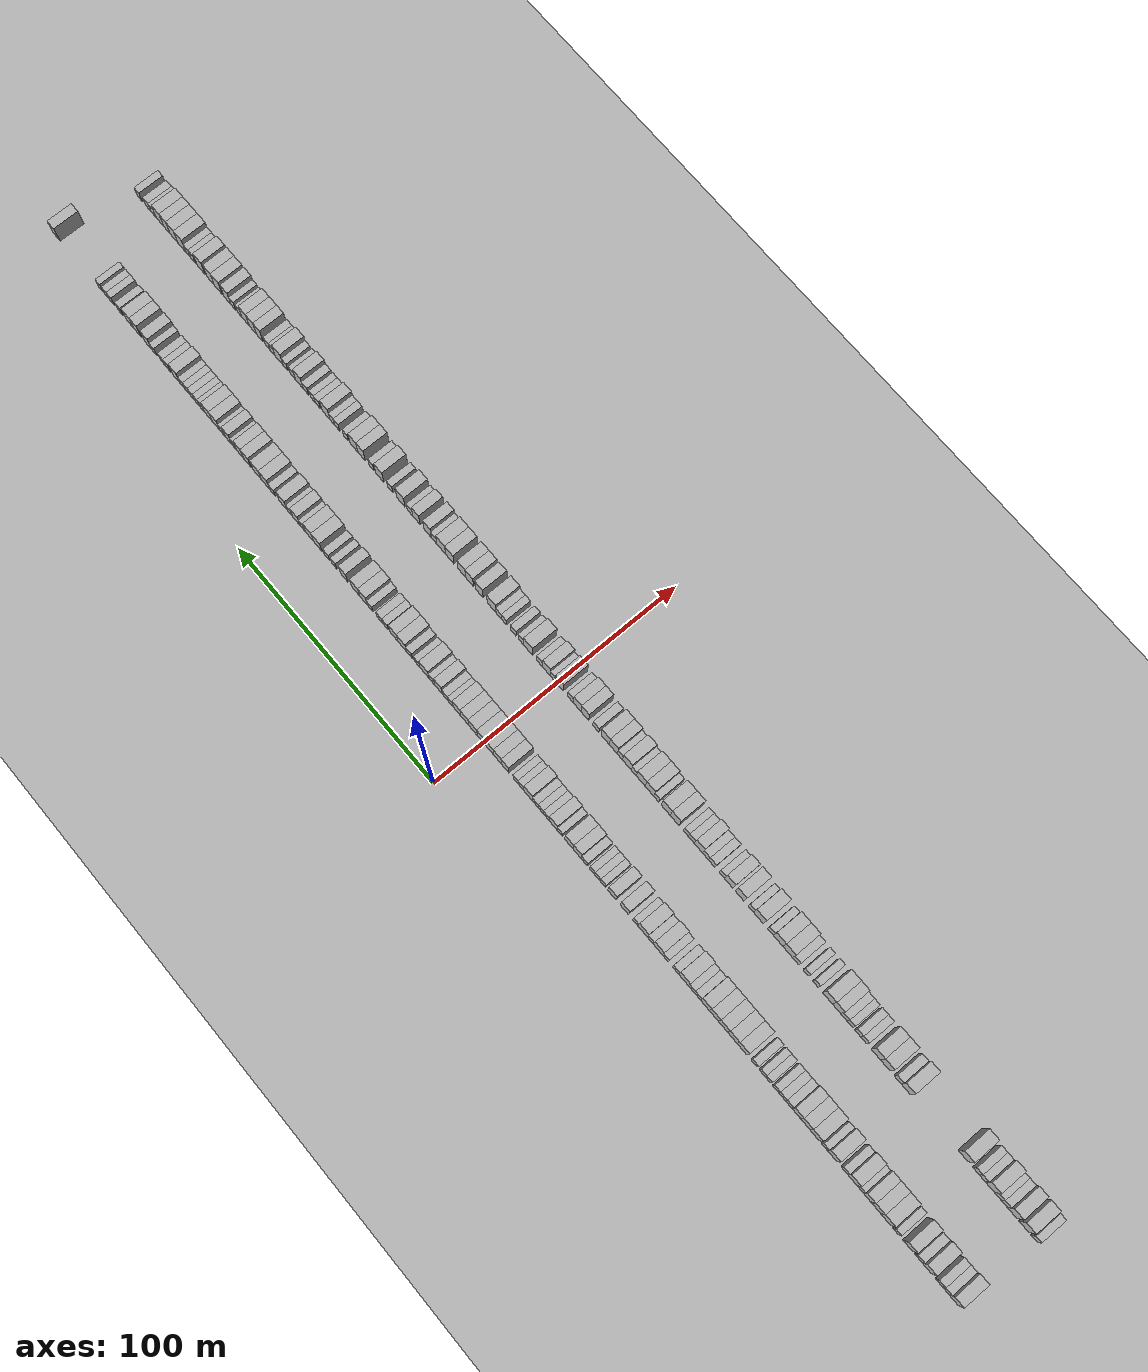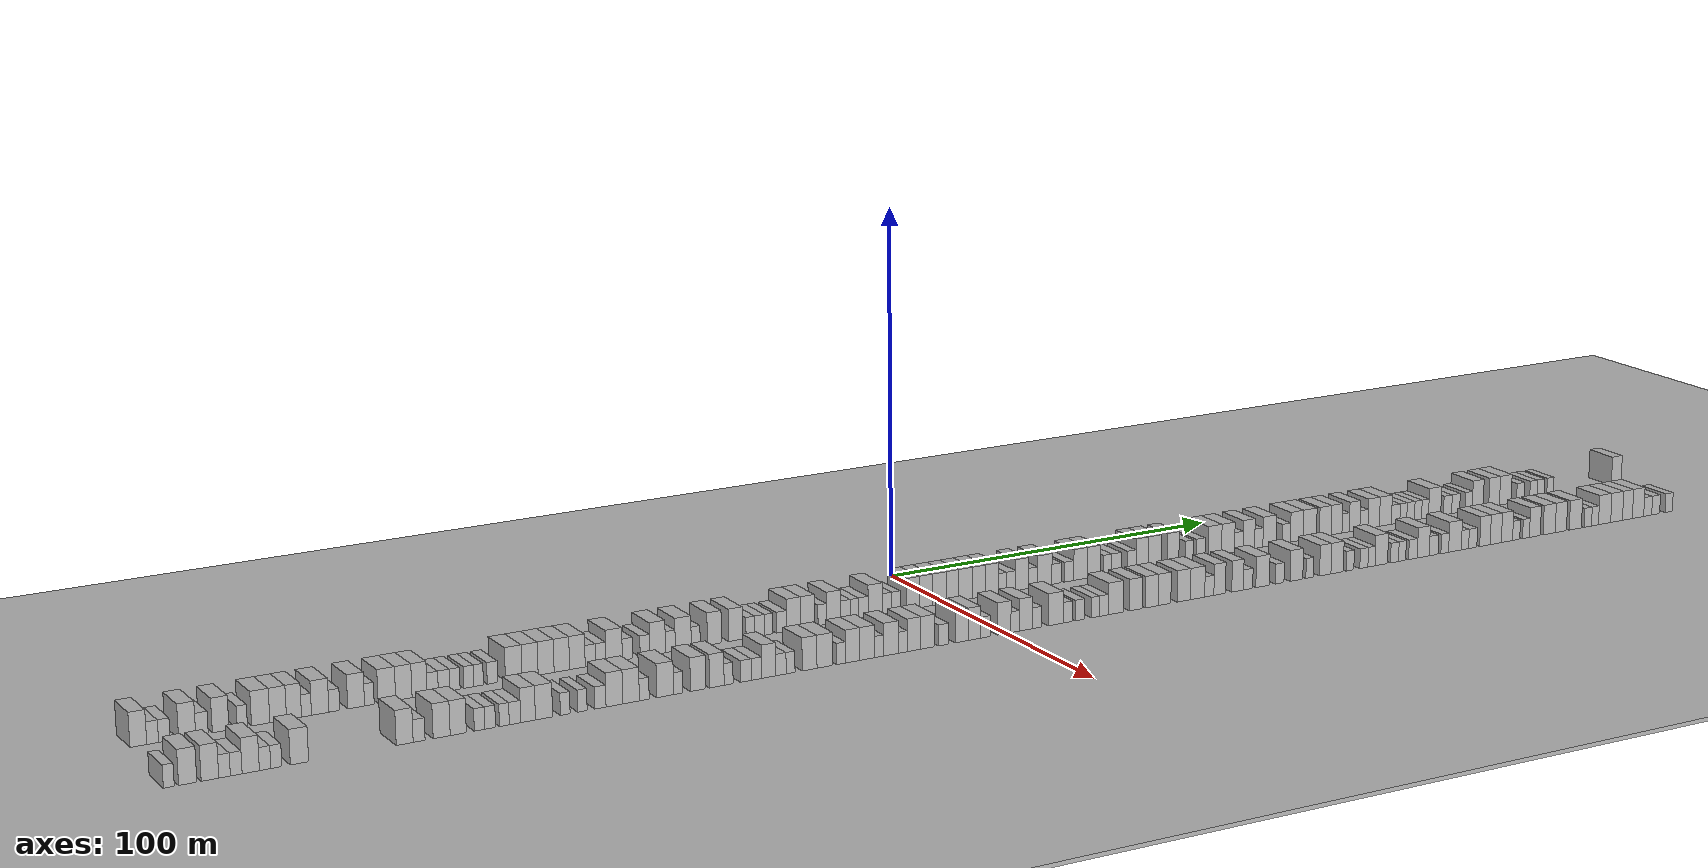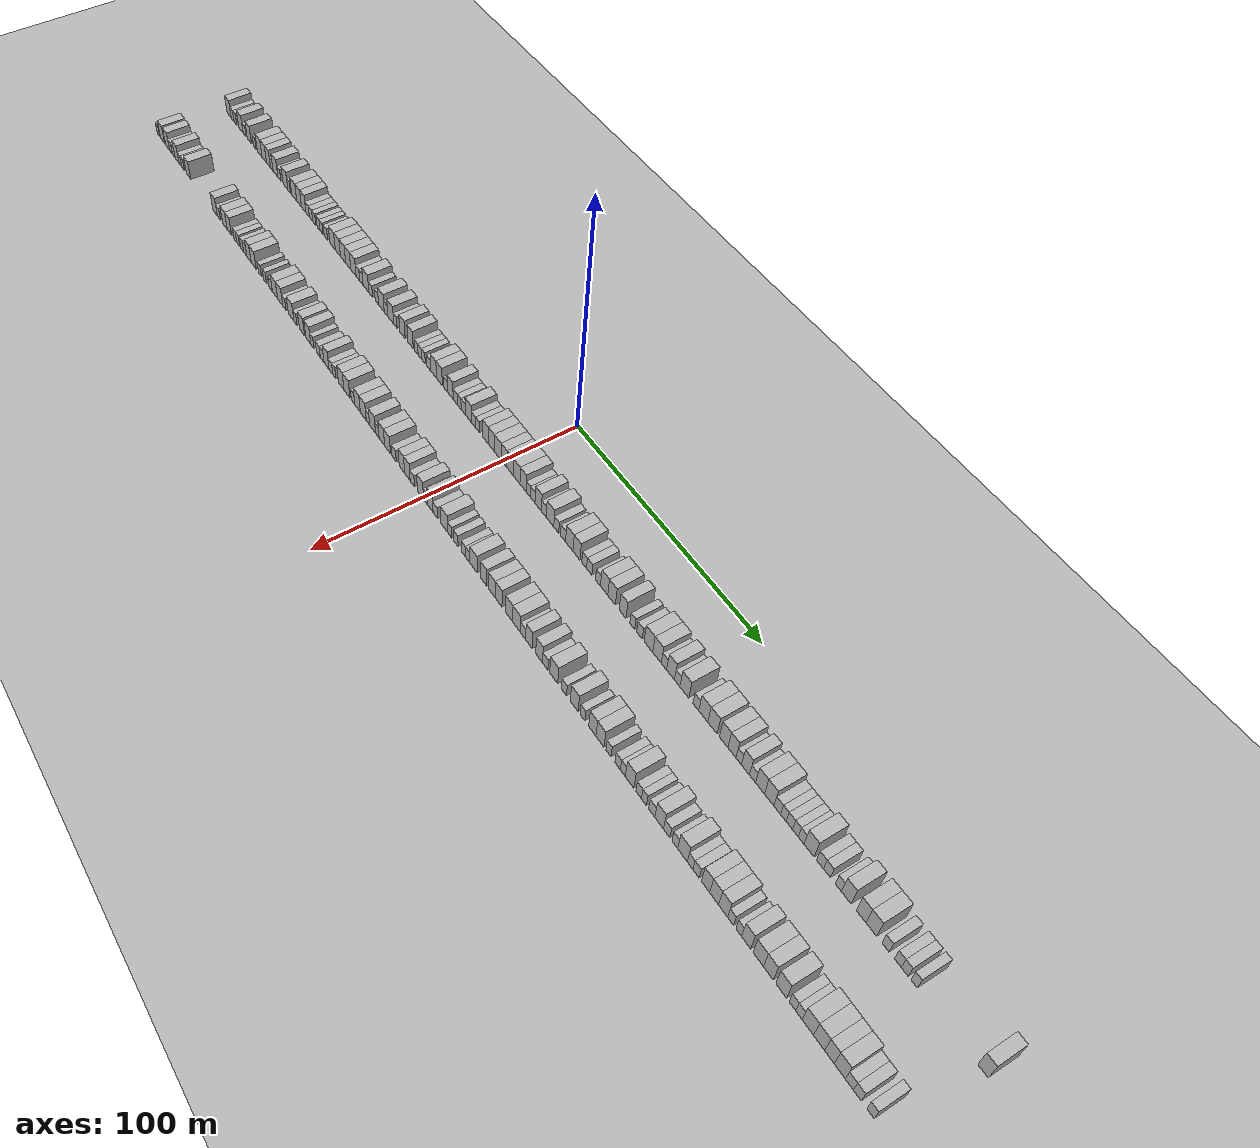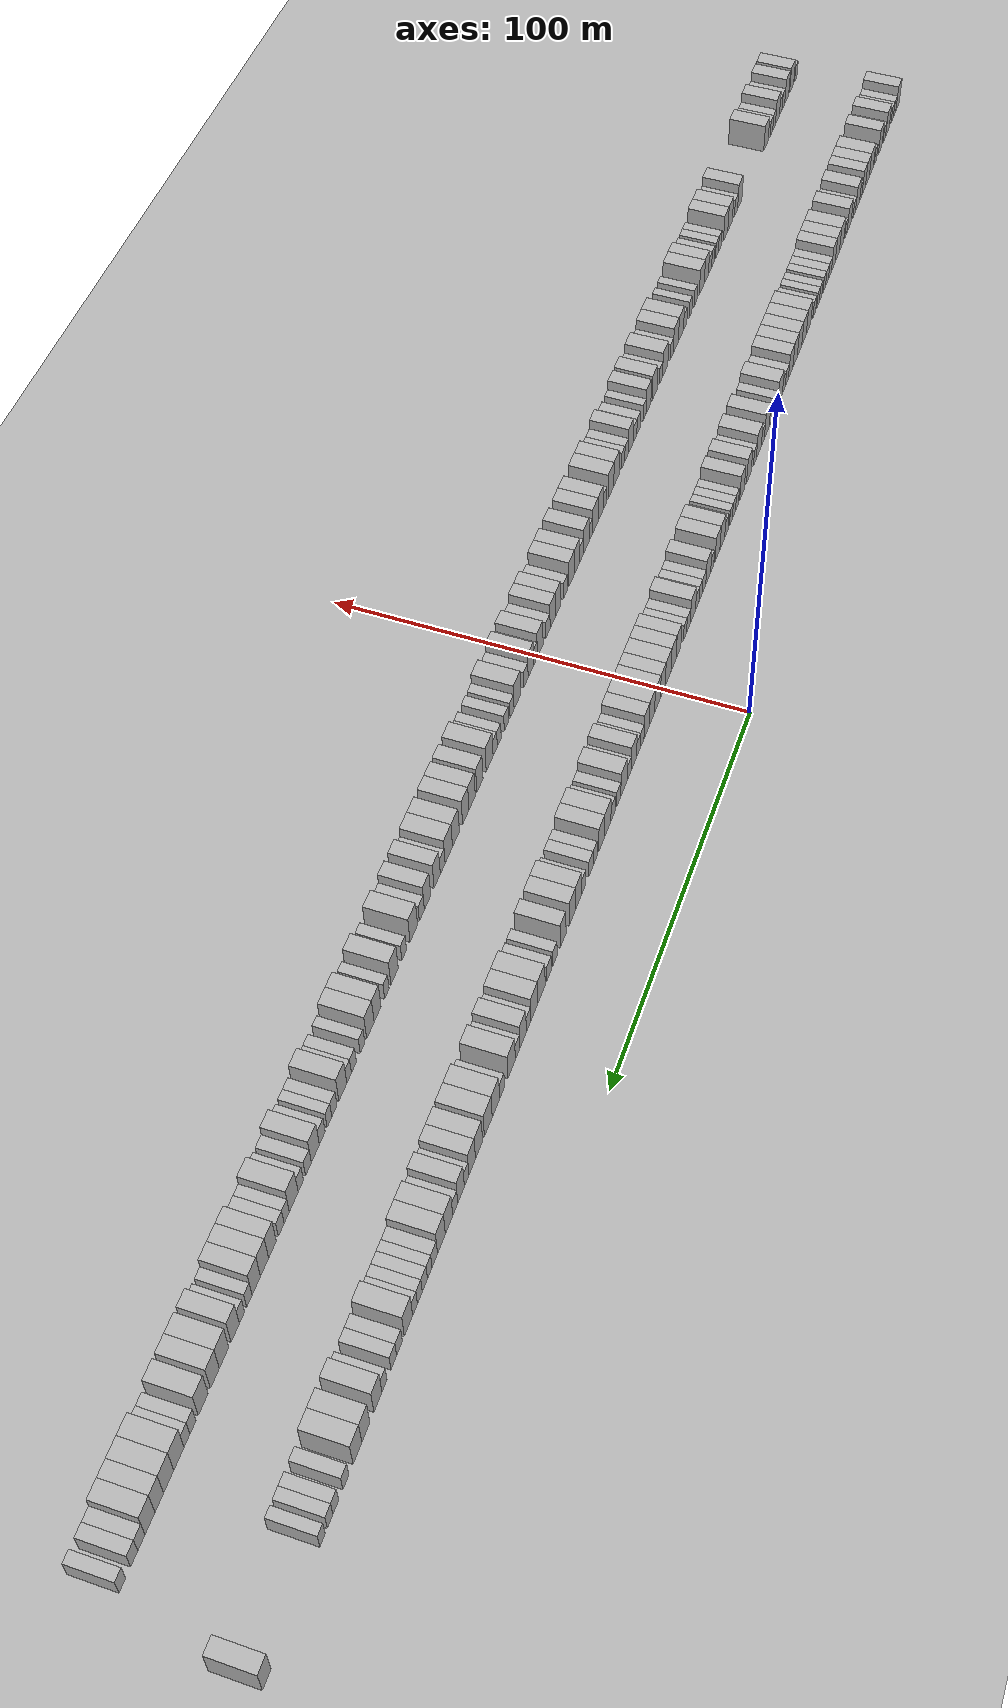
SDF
<?xml version="1.0" encoding="utf-8"?>

<sdf version="1.6">

   <world name="default">

      <gui fullscreen="0">

         <camera name="user_camera">

            <pose>-15 0 4.57585 0 0 0</pose>

            <view_controller>orbit</view_controller>

         </camera>

      </gui>

      <scene>

         <sky>

           <clouds>

             <speed>12</speed>

           </clouds>

         </sky>

         <ambient>0.4 0.4 0.4 1</ambient>

         <background>0.7 0.7 0.7 1</background>

         <shadows>1</shadows>

      </scene>

      <gravity>0 0 -9.8066</gravity>

      <magnetic_field>6e-06 2.3e-05 -4.2e-05</magnetic_field>

      <physics default="0" name="default_physics" type="ode">

         <ode>

            <solver>

               <type>quick</type>

               <iters>10</iters>

               <sor>1.0</sor>

               <use_dynamic_moi_rescaling>0</use_dynamic_moi_rescaling>

            </solver>

            <constraints>

               <cfm>0</cfm>

               <erp>0.2</erp>

               <contact_max_correcting_vel>100</contact_max_correcting_vel>

               <contact_surface_layer>0.001</contact_surface_layer>

            </constraints>

         </ode>

         <max_step_size>0.004</max_step_size>

         <real_time_factor>1</real_time_factor>

         <real_time_update_rate>250</real_time_update_rate>

      </physics>

      <light name="sun" type="directional">

         <cast_shadows>1</cast_shadows>

         <pose>0 0 10 0 0 0</pose>

         <diffuse>0.8 0.8 0.8 1</diffuse>

         <specular>0.2 0.2 0.2 1</specular>

         <attenuation>

            <range>1000</range>

            <constant>0.9</constant>

            <linear>0.01</linear>

            <quadratic>0.001</quadratic>

         </attenuation>

         <direction>-0.5 0.1 -0.9</direction>

      </light>

      <include>

         <name>ground_plane_1</name>

         <uri>model://HANNAS_ground_plane</uri>

         <pose>0 0 0  0 0 0</pose>

      </include>

      <include>

         <name>ground_plane_2</name>

         <uri>model://HANNAS_ground_plane</uri>

         <pose>100 0 0  0 0 0</pose>

      </include>

      <model name="building_1">

         <static>1</static>

         <pose frame="">25.0000 -216.0146 0 0.000000 0.000000 0.000000</pose>

         <link name="link">

            <pose frame="">0 0 4.50 0 0 0</pose>

            <collision name="collision">

               <geometry>

                  <box>

                     <size>10.0000 3.9708 9.0000</size>

                  </box>

               </geometry>

               <max_contacts>10</max_contacts>

               <surface>

                  <contact>

                     <ode/>

                  </contact>

                  <bounce/>

                  <friction>

                     <torsional>

                        <ode/>

                     </torsional>

                     <ode/>

                  </friction>

               </surface>

            </collision>

            <visual name="visual">

               <cast_shadows>0</cast_shadows>

               <geometry>

                  <box>

                     <size>10.0000 3.9708 9.0000</size>

                  </box>

               </geometry>

               <material>

                  <script>

                     <uri>model://HANNAS_wall/materials/scripts</uri>

                     <uri>model://HANNAS_wall/materials/textures</uri>

                     <name>vrc/HANNAS_wall</name>

                  </script>

               </material>

            </visual>

            <self_collide>0</self_collide>

            <enable_wind>0</enable_wind>

            <kinematic>0</kinematic>

         </link>

      </model>

      <model name="building_2">

         <static>1</static>

         <pose frame="">25.0000 -212.6377 0 0.000000 0.000000 0.000000</pose>

         <link name="link">

            <pose frame="">0 0 3.00 0 0 0</pose>

            <collision name="collision">

               <geometry>

                  <box>

                     <size>10.0000 2.7830 6.0000</size>

                  </box>

               </geometry>

               <max_contacts>10</max_contacts>

               <surface>

                  <contact>

                     <ode/>

                  </contact>

                  <bounce/>

                  <friction>

                     <torsional>

                        <ode/>

                     </torsional>

                     <ode/>

                  </friction>

               </surface>

            </collision>

            <visual name="visual">

               <cast_shadows>0</cast_shadows>

               <geometry>

                  <box>

                     <size>10.0000 2.7830 6.0000</size>

                  </box>

               </geometry>

               <material>

                  <script>

                     <uri>model://HANNAS_wall/materials/scripts</uri>

                     <uri>model://HANNAS_wall/materials/textures</uri>

                     <name>vrc/HANNAS_wall</name>

                  </script>

               </material>

            </visual>

            <self_collide>0</self_collide>

            <enable_wind>0</enable_wind>

            <kinematic>0</kinematic>

         </link>

      </model>

      <model name="building_3">

         <static>1</static>

         <pose frame="">25.0000 -209.8646 0 0.000000 0.000000 0.000000</pose>

         <link name="link">

            <pose frame="">0 0 3.00 0 0 0</pose>

            <collision name="collision">

               <geometry>

                  <box>

                     <size>10.0000 2.7633 6.0000</size>

                  </box>

               </geometry>

               <max_contacts>10</max_contacts>

               <surface>

                  <contact>

                     <ode/>

                  </contact>

                  <bounce/>

                  <friction>

                     <torsional>

                        <ode/>

                     </torsional>

                     <ode/>

                  </friction>

               </surface>

            </collision>

            <visual name="visual">

               <cast_shadows>0</cast_shadows>

               <geometry>

                  <box>

                     <size>10.0000 2.7633 6.0000</size>

                  </box>

               </geometry>

               <material>

                  <script>

                     <uri>model://HANNAS_wall/materials/scripts</uri>

                     <uri>model://HANNAS_wall/materials/textures</uri>

                     <name>vrc/HANNAS_wall</name>

                  </script>

               </material>

            </visual>

            <self_collide>0</self_collide>

            <enable_wind>0</enable_wind>

            <kinematic>0</kinematic>

         </link>

      </model>

      <model name="building_4">

         <static>1</static>

         <pose frame="">25.0000 -204.4368 0 0.000000 0.000000 0.000000</pose>

         <link name="link">

            <pose frame="">0 0 4.50 0 0 0</pose>

            <collision name="collision">

               <geometry>

                  <box>

                     <size>10.0000 4.0923 9.0000</size>

                  </box>

               </geometry>

               <max_contacts>10</max_contacts>

               <surface>

                  <contact>

                     <ode/>

                  </contact>

                  <bounce/>

                  <friction>

                     <torsional>

                        <ode/>

                     </torsional>

                     <ode/>

                  </friction>

               </surface>

            </collision>

            <visual name="visual">

               <cast_shadows>0</cast_shadows>

               <geometry>

                  <box>

                     <size>10.0000 4.0923 9.0000</size>

                  </box>

               </geometry>

               <material>

                  <script>

                     <uri>model://HANNAS_wall/materials/scripts</uri>

                     <uri>model://HANNAS_wall/materials/textures</uri>

                     <name>vrc/HANNAS_wall</name>

                  </script>

               </material>

            </visual>

            <self_collide>0</self_collide>

            <enable_wind>0</enable_wind>

            <kinematic>0</kinematic>

         </link>

      </model>

      <model name="building_5">

         <static>1</static>

         <pose frame="">25.0000 -200.8921 0 0.000000 0.000000 0.000000</pose>

         <link name="link">

            <pose frame="">0 0 3.00 0 0 0</pose>

            <collision name="collision">

               <geometry>

                  <box>

                     <size>10.0000 2.9970 6.0000</size>

                  </box>

               </geometry>

               <max_contacts>10</max_contacts>

               <surface>

                  <contact>

                     <ode/>

                  </contact>

                  <bounce/>

                  <friction>

                     <torsional>

                        <ode/>

                     </torsional>

                     <ode/>

                  </friction>

               </surface>

            </collision>

            <visual name="visual">

               <cast_shadows>0</cast_shadows>

               <geometry>

                  <box>

                     <size>10.0000 2.9970 6.0000</size>

                  </box>

               </geometry>

               <material>

                  <script>

                     <uri>model://HANNAS_wall/materials/scripts</uri>

                     <uri>model://HANNAS_wall/materials/textures</uri>

                     <name>vrc/HANNAS_wall</name>

                  </script>

               </material>

            </visual>

            <self_collide>0</self_collide>

            <enable_wind>0</enable_wind>

            <kinematic>0</kinematic>

         </link>

      </model>

      <model name="building_6">

         <static>1</static>

         <pose frame="">25.0000 -196.3850 0 0.000000 0.000000 0.000000</pose>

         <link name="link">

            <pose frame="">0 0 4.50 0 0 0</pose>

            <collision name="collision">

               <geometry>

                  <box>

                     <size>10.0000 4.0172 9.0000</size>

                  </box>

               </geometry>

               <max_contacts>10</max_contacts>

               <surface>

                  <contact>

                     <ode/>

                  </contact>

                  <bounce/>

                  <friction>

                     <torsional>

                        <ode/>

                     </torsional>

                     <ode/>

                  </friction>

               </surface>

            </collision>

            <visual name="visual">

               <cast_shadows>0</cast_shadows>

               <geometry>

                  <box>

                     <size>10.0000 4.0172 9.0000</size>

                  </box>

               </geometry>

               <material>

                  <script>

                     <uri>model://HANNAS_wall/materials/scripts</uri>

                     <uri>model://HANNAS_wall/materials/textures</uri>

                     <name>vrc/HANNAS_wall</name>

                  </script>

               </material>

            </visual>

            <self_collide>0</self_collide>

            <enable_wind>0</enable_wind>

            <kinematic>0</kinematic>

         </link>

      </model>

      <model name="building_7">

         <static>1</static>

         <pose frame="">25.0000 -191.1398 0 0.000000 0.000000 0.000000</pose>

         <link name="link">

            <pose frame="">0 0 3.00 0 0 0</pose>

            <collision name="collision">

               <geometry>

                  <box>

                     <size>10.0000 2.4732 6.0000</size>

                  </box>

               </geometry>

               <max_contacts>10</max_contacts>

               <surface>

                  <contact>

                     <ode/>

                  </contact>

                  <bounce/>

                  <friction>

                     <torsional>

                        <ode/>

                     </torsional>

                     <ode/>

                  </friction>

               </surface>

            </collision>

            <visual name="visual">

               <cast_shadows>0</cast_shadows>

               <geometry>

                  <box>

                     <size>10.0000 2.4732 6.0000</size>

                  </box>

               </geometry>

               <material>

                  <script>

                     <uri>model://HANNAS_wall/materials/scripts</uri>

                     <uri>model://HANNAS_wall/materials/textures</uri>

                     <name>vrc/HANNAS_wall</name>

                  </script>

               </material>

            </visual>

            <self_collide>0</self_collide>

            <enable_wind>0</enable_wind>

            <kinematic>0</kinematic>

         </link>

      </model>

      <model name="building_8">

         <static>1</static>

         <pose frame="">25.0000 -186.6611 0 0.000000 0.000000 0.000000</pose>

         <link name="link">

            <pose frame="">0 0 4.50 0 0 0</pose>

            <collision name="collision">

               <geometry>

                  <box>

                     <size>10.0000 4.4841 9.0000</size>

                  </box>

               </geometry>

               <max_contacts>10</max_contacts>

               <surface>

                  <contact>

                     <ode/>

                  </contact>

                  <bounce/>

                  <friction>

                     <torsional>

                        <ode/>

                     </torsional>

                     <ode/>

                  </friction>

               </surface>

            </collision>

            <visual name="visual">

               <cast_shadows>0</cast_shadows>

               <geometry>

                  <box>

                     <size>10.0000 4.4841 9.0000</size>

                  </box>

               </geometry>

               <material>

                  <script>

                     <uri>model://HANNAS_wall/materials/scripts</uri>

                     <uri>model://HANNAS_wall/materials/textures</uri>

                     <name>vrc/HANNAS_wall</name>

                  </script>

               </material>

            </visual>

            <self_collide>0</self_collide>

            <enable_wind>0</enable_wind>

            <kinematic>0</kinematic>

         </link>

      </model>

      <model name="building_9">

         <static>1</static>

         <pose frame="">25.0000 -182.3765 0 0.000000 0.000000 0.000000</pose>

         <link name="link">

            <pose frame="">0 0 4.50 0 0 0</pose>

            <collision name="collision">

               <geometry>

                  <box>

                     <size>10.0000 4.0853 9.0000</size>

                  </box>

               </geometry>

               <max_contacts>10</max_contacts>

               <surface>

                  <contact>

                     <ode/>

                  </contact>

                  <bounce/>

                  <friction>

                     <torsional>

                        <ode/>

                     </torsional>

                     <ode/>

                  </friction>

               </surface>

            </collision>

            <visual name="visual">

               <cast_shadows>0</cast_shadows>

               <geometry>

                  <box>

                     <size>10.0000 4.0853 9.0000</size>

                  </box>

               </geometry>

               <material>

                  <script>

                     <uri>model://HANNAS_wall/materials/scripts</uri>

                     <uri>model://HANNAS_wall/materials/textures</uri>

                     <name>vrc/HANNAS_wall</name>

                  </script>

               </material>

            </visual>

            <self_collide>0</self_collide>

            <enable_wind>0</enable_wind>

            <kinematic>0</kinematic>

         </link>

      </model>

      <model name="building_10">

         <static>1</static>

         <pose frame="">25.0000 -178.4873 0 0.000000 0.000000 0.000000</pose>

         <link name="link">

            <pose frame="">0 0 4.50 0 0 0</pose>

            <collision name="collision">

               <geometry>

                  <box>

                     <size>10.0000 3.6931 9.0000</size>

                  </box>

               </geometry>

               <max_contacts>10</max_contacts>

               <surface>

                  <contact>

                     <ode/>

                  </contact>

                  <bounce/>

                  <friction>

                     <torsional>

                        <ode/>

                     </torsional>

                     <ode/>

                  </friction>

               </surface>

            </collision>

            <visual name="visual">

               <cast_shadows>0</cast_shadows>

               <geometry>

                  <box>

                     <size>10.0000 3.6931 9.0000</size>

                  </box>

               </geometry>

               <material>

                  <script>

                     <uri>model://HANNAS_wall/materials/scripts</uri>

                     <uri>model://HANNAS_wall/materials/textures</uri>

                     <name>vrc/HANNAS_wall</name>

                  </script>

               </material>

            </visual>

            <self_collide>0</self_collide>

            <enable_wind>0</enable_wind>

            <kinematic>0</kinematic>

         </link>

      </model>

      <model name="building_11">

         <static>1</static>

         <pose frame="">25.0000 -175.4033 0 0.000000 0.000000 0.000000</pose>

         <link name="link">

            <pose frame="">0 0 3.00 0 0 0</pose>

            <collision name="collision">

               <geometry>

                  <box>

                     <size>10.0000 2.4749 6.0000</size>

                  </box>

               </geometry>

               <max_contacts>10</max_contacts>

               <surface>

                  <contact>

                     <ode/>

                  </contact>

                  <bounce/>

                  <friction>

                     <torsional>

                        <ode/>

                     </torsional>

                     <ode/>

                  </friction>

               </surface>

            </collision>

            <visual name="visual">

               <cast_shadows>0</cast_shadows>

               <geometry>

                  <box>

                     <size>10.0000 2.4749 6.0000</size>

                  </box>

               </geometry>

               <material>

                  <script>

                     <uri>model://HANNAS_wall/materials/scripts</uri>

                     <uri>model://HANNAS_wall/materials/textures</uri>

                     <name>vrc/HANNAS_wall</name>

                  </script>

               </material>

            </visual>

            <self_collide>0</self_collide>

            <enable_wind>0</enable_wind>

            <kinematic>0</kinematic>

         </link>

      </model>

      <model name="building_12">

         <static>1</static>

         <pose frame="">25.0000 -171.9986 0 0.000000 0.000000 0.000000</pose>

         <link name="link">

            <pose frame="">0 0 4.50 0 0 0</pose>

            <collision name="collision">

               <geometry>

                  <box>

                     <size>10.0000 4.3345 9.0000</size>

                  </box>

               </geometry>

               <max_contacts>10</max_contacts>

               <surface>

                  <contact>

                     <ode/>

                  </contact>

                  <bounce/>

                  <friction>

                     <torsional>

                        <ode/>

                     </torsional>

                     <ode/>

                  </friction>

               </surface>

            </collision>

            <visual name="visual">

               <cast_shadows>0</cast_shadows>

               <geometry>

                  <box>

                     <size>10.0000 4.3345 9.0000</size>

                  </box>

               </geometry>

               <material>

                  <script>

                     <uri>model://HANNAS_wall/materials/scripts</uri>

                     <uri>model://HANNAS_wall/materials/textures</uri>

                     <name>vrc/HANNAS_wall</name>

                  </script>

               </material>

            </visual>

            <self_collide>0</self_collide>

            <enable_wind>0</enable_wind>

            <kinematic>0</kinematic>

         </link>

      </model>

      <model name="building_13">

         <static>1</static>

         <pose frame="">25.0000 -168.4795 0 0.000000 0.000000 0.000000</pose>

         <link name="link">

            <pose frame="">0 0 3.00 0 0 0</pose>

            <collision name="collision">

               <geometry>

                  <box>

                     <size>10.0000 2.7037 6.0000</size>

                  </box>

               </geometry>

               <max_contacts>10</max_contacts>

               <surface>

                  <contact>

                     <ode/>

                  </contact>

                  <bounce/>

                  <friction>

                     <torsional>

                        <ode/>

                     </torsional>

                     <ode/>

                  </friction>

               </surface>

            </collision>

            <visual name="visual">

               <cast_shadows>0</cast_shadows>

               <geometry>

                  <box>

                     <size>10.0000 2.7037 6.0000</size>

                  </box>

               </geometry>

               <material>

                  <script>

                     <uri>model://HANNAS_wall/materials/scripts</uri>

                     <uri>model://HANNAS_wall/materials/textures</uri>

                     <name>vrc/HANNAS_wall</name>

                  </script>

               </material>

            </visual>

            <self_collide>0</self_collide>

            <enable_wind>0</enable_wind>

            <kinematic>0</kinematic>

         </link>

      </model>

      <model name="building_14">

         <static>1</static>

         <pose frame="">25.0000 -163.0207 0 0.000000 0.000000 0.000000</pose>

         <link name="link">

            <pose frame="">0 0 4.50 0 0 0</pose>

            <collision name="collision">

               <geometry>

                  <box>

                     <size>10.0000 4.2139 9.0000</size>

                  </box>

               </geometry>

               <max_contacts>10</max_contacts>

               <surface>

                  <contact>

                     <ode/>

                  </contact>

                  <bounce/>

                  <friction>

                     <torsional>

                        <ode/>

                     </torsional>

                     <ode/>

                  </friction>

               </surface>

            </collision>

            <visual name="visual">

               <cast_shadows>0</cast_shadows>

               <geometry>

                  <box>

                     <size>10.0000 4.2139 9.0000</size>

                  </box>

               </geometry>

               <material>

                  <script>

                     <uri>model://HANNAS_wall/materials/scripts</uri>

                     <uri>model://HANNAS_wall/materials/textures</uri>

                     <name>vrc/HANNAS_wall</name>

                  </script>

               </material>

            </visual>

            <self_collide>0</self_collide>

            <enable_wind>0</enable_wind>

            <kinematic>0</kinematic>

         </link>

      </model>

      <model name="building_15">

         <static>1</static>

         <pose frame="">25.0000 -159.7039 0 0.000000 0.000000 0.000000</pose>

         <link name="link">

            <pose frame="">0 0 3.00 0 0 0</pose>

            <collision name="collision">

               <geometry>

                  <box>

                     <size>10.0000 2.4196 6.0000</size>

                  </box>

               </geometry>

               <max_contacts>10</max_contacts>

               <surface>

                  <contact>

                     <ode/>

                  </contact>

                  <bounce/>

                  <friction>

                     <torsional>

                        <ode/>

                     </torsional>

                     <ode/>

                  </friction>

               </surface>

            </collision>

            <visual name="visual">

               <cast_shadows>0</cast_shadows>

               <geometry>

                  <box>

                     <size>10.0000 2.4196 6.0000</size>

                  </box>

               </geometry>

               <material>

                  <script>

                     <uri>model://HANNAS_wall/materials/scripts</uri>

                     <uri>model://HANNAS_wall/materials/textures</uri>

                     <name>vrc/HANNAS_wall</name>

                  </script>

               </material>

            </visual>

            <self_collide>0</self_collide>

            <enable_wind>0</enable_wind>

            <kinematic>0</kinematic>

         </link>

      </model>

      <model name="building_16">

         <static>1</static>

         <pose frame="">25.0000 -155.2690 0 0.000000 0.000000 0.000000</pose>

         <link name="link">

            <pose frame="">0 0 4.50 0 0 0</pose>

            <collision name="collision">

               <geometry>

                  <box>

                     <size>10.0000 4.4502 9.0000</size>

                  </box>

               </geometry>

               <max_contacts>10</max_contacts>

               <surface>

                  <contact>

                     <ode/>

                  </contact>

                  <bounce/>

                  <friction>

                     <torsional>

                        <ode/>

                     </torsional>

                     <ode/>

                  </friction>

               </surface>

            </collision>

            <visual name="visual">

               <cast_shadows>0</cast_shadows>

               <geometry>

                  <box>

                     <size>10.0000 4.4502 9.0000</size>

                  </box>

               </geometry>

               <material>

                  <script>

                     <uri>model://HANNAS_wall/materials/scripts</uri>

                     <uri>model://HANNAS_wall/materials/textures</uri>

                     <name>vrc/HANNAS_wall</name>

                  </script>

               </material>

            </visual>

            <self_collide>0</self_collide>

            <enable_wind>0</enable_wind>

            <kinematic>0</kinematic>

         </link>

      </model>

      <model name="building_17">

         <static>1</static>

         <pose frame="">25.0000 -150.9616 0 0.000000 0.000000 0.000000</pose>

         <link name="link">

            <pose frame="">0 0 4.50 0 0 0</pose>

            <collision name="collision">

               <geometry>

                  <box>

                     <size>10.0000 4.1646 9.0000</size>

                  </box>

               </geometry>

               <max_contacts>10</max_contacts>

               <surface>

                  <contact>

                     <ode/>

                  </contact>

                  <bounce/>

                  <friction>

                     <torsional>

                        <ode/>

                     </torsional>

                     <ode/>

                  </friction>

               </surface>

            </collision>

            <visual name="visual">

               <cast_shadows>0</cast_shadows>

               <geometry>

                  <box>

                     <size>10.0000 4.1646 9.0000</size>

                  </box>

               </geometry>

               <material>

                  <script>

                     <uri>model://HANNAS_wall/materials/scripts</uri>

                     <uri>model://HANNAS_wall/materials/textures</uri>

                     <name>vrc/HANNAS_wall</name>

                  </script>

               </material>

            </visual>

            <self_collide>0</self_collide>

            <enable_wind>0</enable_wind>

            <kinematic>0</kinematic>

         </link>

      </model>

      <model name="building_18">

         <static>1</static>

         <pose frame="">25.0000 -146.9470 0 0.000000 0.000000 0.000000</pose>

         <link name="link">

            <pose frame="">0 0 4.50 0 0 0</pose>

            <collision name="collision">

               <geometry>

                  <box>

                     <size>10.0000 3.8646 9.0000</size>

                  </box>

               </geometry>

               <max_contacts>10</max_contacts>

               <surface>

                  <contact>

                     <ode/>

                  </contact>

                  <bounce/>

                  <friction>

                     <torsional>

                        <ode/>

                     </torsional>

                     <ode/>

                  </friction>

               </surface>

            </collision>

            <visual name="visual">

               <cast_shadows>0</cast_shadows>

               <geometry>

                  <box>

                     <size>10.0000 3.8646 9.0000</size>

                  </box>

               </geometry>

               <material>

                  <script>

                     <uri>model://HANNAS_wall/materials/scripts</uri>

                     <uri>model://HANNAS_wall/materials/textures</uri>

                     <name>vrc/HANNAS_wall</name>

                  </script>

               </material>

            </visual>

            <self_collide>0</self_collide>

            <enable_wind>0</enable_wind>

            <kinematic>0</kinematic>

         </link>

      </model>

      <model name="building_19">

         <static>1</static>

         <pose frame="">25.0000 -143.5795 0 0.000000 0.000000 0.000000</pose>

         <link name="link">

            <pose frame="">0 0 3.00 0 0 0</pose>

            <collision name="collision">

               <geometry>

                  <box>

                     <size>10.0000 2.8704 6.0000</size>

                  </box>

               </geometry>

               <max_contacts>10</max_contacts>

               <surface>

                  <contact>

                     <ode/>

                  </contact>

                  <bounce/>

                  <friction>

                     <torsional>

                        <ode/>

                     </torsional>

                     <ode/>

                  </friction>

               </surface>

            </collision>

            <visual name="visual">

               <cast_shadows>0</cast_shadows>

               <geometry>

                  <box>

                     <size>10.0000 2.8704 6.0000</size>

                  </box>

               </geometry>

               <material>

                  <script>

                     <uri>model://HANNAS_wall/materials/scripts</uri>

                     <uri>model://HANNAS_wall/materials/textures</uri>

                     <name>vrc/HANNAS_wall</name>

                  </script>

               </material>

            </visual>

            <self_collide>0</self_collide>

            <enable_wind>0</enable_wind>

            <kinematic>0</kinematic>

         </link>

      </model>

      <model name="building_20">

         <static>1</static>

         <pose frame="">25.0000 -140.6475 0 0.000000 0.000000 0.000000</pose>

         <link name="link">

            <pose frame="">0 0 3.00 0 0 0</pose>

            <collision name="collision">

               <geometry>

                  <box>

                     <size>10.0000 2.9938 6.0000</size>

                  </box>

               </geometry>

               <max_contacts>10</max_contacts>

               <surface>

                  <contact>

                     <ode/>

                  </contact>

                  <bounce/>

                  <friction>

                     <torsional>

                        <ode/>

                     </torsional>

                     <ode/>

                  </friction>

               </surface>

            </collision>

            <visual name="visual">

               <cast_shadows>0</cast_shadows>

               <geometry>

                  <box>

                     <size>10.0000 2.9938 6.0000</size>

                  </box>

               </geometry>

               <material>

                  <script>

                     <uri>model://HANNAS_wall/materials/scripts</uri>

                     <uri>model://HANNAS_wall/materials/textures</uri>

                     <name>vrc/HANNAS_wall</name>

                  </script>

               </material>

            </visual>

            <self_collide>0</self_collide>

            <enable_wind>0</enable_wind>

            <kinematic>0</kinematic>

         </link>

      </model>

      <model name="building_21">

         <static>1</static>

         <pose frame="">25.0000 -137.8461 0 0.000000 0.000000 0.000000</pose>

         <link name="link">

            <pose frame="">0 0 3.00 0 0 0</pose>

            <collision name="collision">

               <geometry>

                  <box>

                     <size>10.0000 2.6090 6.0000</size>

                  </box>

               </geometry>

               <max_contacts>10</max_contacts>

               <surface>

                  <contact>

                     <ode/>

                  </contact>

                  <bounce/>

                  <friction>

                     <torsional>

                        <ode/>

                     </torsional>

                     <ode/>

                  </friction>

               </surface>

            </collision>

            <visual name="visual">

               <cast_shadows>0</cast_shadows>

               <geometry>

                  <box>

                     <size>10.0000 2.6090 6.0000</size>

                  </box>

               </geometry>

               <material>

                  <script>

                     <uri>model://HANNAS_wall/materials/scripts</uri>

                     <uri>model://HANNAS_wall/materials/textures</uri>

                     <name>vrc/HANNAS_wall</name>

                  </script>

               </material>

            </visual>

            <self_collide>0</self_collide>

            <enable_wind>0</enable_wind>

            <kinematic>0</kinematic>

         </link>

      </model>

      <model name="building_22">

         <static>1</static>

         <pose frame="">25.0000 -134.2473 0 0.000000 0.000000 0.000000</pose>

         <link name="link">

            <pose frame="">0 0 3.00 0 0 0</pose>

            <collision name="collision">

               <geometry>

                  <box>

                     <size>10.0000 2.5884 6.0000</size>

                  </box>

               </geometry>

               <max_contacts>10</max_contacts>

               <surface>

                  <contact>

                     <ode/>

                  </contact>

                  <bounce/>

                  <friction>

                     <torsional>

                        <ode/>

                     </torsional>

                     <ode/>

                  </friction>

               </surface>

            </collision>

            <visual name="visual">

               <cast_shadows>0</cast_shadows>

               <geometry>

                  <box>

                     <size>10.0000 2.5884 6.0000</size>

                  </box>

               </geometry>

               <material>

                  <script>

                     <uri>model://HANNAS_wall/materials/scripts</uri>

                     <uri>model://HANNAS_wall/materials/textures</uri>

                     <name>vrc/HANNAS_wall</name>

                  </script>

               </material>

            </visual>

            <self_collide>0</self_collide>

            <enable_wind>0</enable_wind>

            <kinematic>0</kinematic>

         </link>

      </model>

      <model name="building_23">

         <static>1</static>

         <pose frame="">25.0000 -131.7096 0 0.000000 0.000000 0.000000</pose>

         <link name="link">

            <pose frame="">0 0 3.00 0 0 0</pose>

            <collision name="collision">

               <geometry>

                  <box>

                     <size>10.0000 2.4871 6.0000</size>

                  </box>

               </geometry>

               <max_contacts>10</max_contacts>

               <surface>

                  <contact>

                     <ode/>

                  </contact>

                  <bounce/>

                  <friction>

                     <torsional>

                        <ode/>

                     </torsional>

                     <ode/>

                  </friction>

               </surface>

            </collision>

            <visual name="visual">

               <cast_shadows>0</cast_shadows>

               <geometry>

                  <box>

                     <size>10.0000 2.4871 6.0000</size>

                  </box>

               </geometry>

               <material>

                  <script>

                     <uri>model://HANNAS_wall/materials/scripts</uri>

                     <uri>model://HANNAS_wall/materials/textures</uri>

                     <name>vrc/HANNAS_wall</name>

                  </script>

               </material>

            </visual>

            <self_collide>0</self_collide>

            <enable_wind>0</enable_wind>

            <kinematic>0</kinematic>

         </link>

      </model>

      <model name="building_24">

         <static>1</static>

         <pose frame="">25.0000 -128.0845 0 0.000000 0.000000 0.000000</pose>

         <link name="link">

            <pose frame="">0 0 3.00 0 0 0</pose>

            <collision name="collision">

               <geometry>

                  <box>

                     <size>10.0000 2.7631 6.0000</size>

                  </box>

               </geometry>

               <max_contacts>10</max_contacts>

               <surface>

                  <contact>

                     <ode/>

                  </contact>

                  <bounce/>

                  <friction>

                     <torsional>

                        <ode/>

                     </torsional>

                     <ode/>

                  </friction>

               </surface>

            </collision>

            <visual name="visual">

               <cast_shadows>0</cast_shadows>

               <geometry>

                  <box>

                     <size>10.0000 2.7631 6.0000</size>

                  </box>

               </geometry>

               <material>

                  <script>

                     <uri>model://HANNAS_wall/materials/scripts</uri>

                     <uri>model://HANNAS_wall/materials/textures</uri>

                     <name>vrc/HANNAS_wall</name>

                  </script>

               </material>

            </visual>

            <self_collide>0</self_collide>

            <enable_wind>0</enable_wind>

            <kinematic>0</kinematic>

         </link>

      </model>

      <model name="building_25">

         <static>1</static>

         <pose frame="">25.0000 -122.5178 0 0.000000 0.000000 0.000000</pose>

         <link name="link">

            <pose frame="">0 0 4.50 0 0 0</pose>

            <collision name="collision">

               <geometry>

                  <box>

                     <size>10.0000 4.3704 9.0000</size>

                  </box>

               </geometry>

               <max_contacts>10</max_contacts>

               <surface>

                  <contact>

                     <ode/>

                  </contact>

                  <bounce/>

                  <friction>

                     <torsional>

                        <ode/>

                     </torsional>

                     <ode/>

                  </friction>

               </surface>

            </collision>

            <visual name="visual">

               <cast_shadows>0</cast_shadows>

               <geometry>

                  <box>

                     <size>10.0000 4.3704 9.0000</size>

                  </box>

               </geometry>

               <material>

                  <script>

                     <uri>model://HANNAS_wall/materials/scripts</uri>

                     <uri>model://HANNAS_wall/materials/textures</uri>

                     <name>vrc/HANNAS_wall</name>

                  </script>

               </material>

            </visual>

            <self_collide>0</self_collide>

            <enable_wind>0</enable_wind>

            <kinematic>0</kinematic>

         </link>

      </model>

      <model name="building_26">

         <static>1</static>

         <pose frame="">25.0000 -118.2107 0 0.000000 0.000000 0.000000</pose>

         <link name="link">

            <pose frame="">0 0 4.50 0 0 0</pose>

            <collision name="collision">

               <geometry>

                  <box>

                     <size>10.0000 4.2439 9.0000</size>

                  </box>

               </geometry>

               <max_contacts>10</max_contacts>

               <surface>

                  <contact>

                     <ode/>

                  </contact>

                  <bounce/>

                  <friction>

                     <torsional>

                        <ode/>

                     </torsional>

                     <ode/>

                  </friction>

               </surface>

            </collision>

            <visual name="visual">

               <cast_shadows>0</cast_shadows>

               <geometry>

                  <box>

                     <size>10.0000 4.2439 9.0000</size>

                  </box>

               </geometry>

               <material>

                  <script>

                     <uri>model://HANNAS_wall/materials/scripts</uri>

                     <uri>model://HANNAS_wall/materials/textures</uri>

                     <name>vrc/HANNAS_wall</name>

                  </script>

               </material>

            </visual>

            <self_collide>0</self_collide>

            <enable_wind>0</enable_wind>

            <kinematic>0</kinematic>

         </link>

      </model>

      <model name="building_27">

         <static>1</static>

         <pose frame="">25.0000 -113.9606 0 0.000000 0.000000 0.000000</pose>

         <link name="link">

            <pose frame="">0 0 4.50 0 0 0</pose>

            <collision name="collision">

               <geometry>

                  <box>

                     <size>10.0000 4.2562 9.0000</size>

                  </box>

               </geometry>

               <max_contacts>10</max_contacts>

               <surface>

                  <contact>

                     <ode/>

                  </contact>

                  <bounce/>

                  <friction>

                     <torsional>

                        <ode/>

                     </torsional>

                     <ode/>

                  </friction>

               </surface>

            </collision>

            <visual name="visual">

               <cast_shadows>0</cast_shadows>

               <geometry>

                  <box>

                     <size>10.0000 4.2562 9.0000</size>

                  </box>

               </geometry>

               <material>

                  <script>

                     <uri>model://HANNAS_wall/materials/scripts</uri>

                     <uri>model://HANNAS_wall/materials/textures</uri>

                     <name>vrc/HANNAS_wall</name>

                  </script>

               </material>

            </visual>

            <self_collide>0</self_collide>

            <enable_wind>0</enable_wind>

            <kinematic>0</kinematic>

         </link>

      </model>

      <model name="building_28">

         <static>1</static>

         <pose frame="">25.0000 -109.7631 0 0.000000 0.000000 0.000000</pose>

         <link name="link">

            <pose frame="">0 0 4.50 0 0 0</pose>

            <collision name="collision">

               <geometry>

                  <box>

                     <size>10.0000 4.1390 9.0000</size>

                  </box>

               </geometry>

               <max_contacts>10</max_contacts>

               <surface>

                  <contact>

                     <ode/>

                  </contact>

                  <bounce/>

                  <friction>

                     <torsional>

                        <ode/>

                     </torsional>

                     <ode/>

                  </friction>

               </surface>

            </collision>

            <visual name="visual">

               <cast_shadows>0</cast_shadows>

               <geometry>

                  <box>

                     <size>10.0000 4.1390 9.0000</size>

                  </box>

               </geometry>

               <material>

                  <script>

                     <uri>model://HANNAS_wall/materials/scripts</uri>

                     <uri>model://HANNAS_wall/materials/textures</uri>

                     <name>vrc/HANNAS_wall</name>

                  </script>

               </material>

            </visual>

            <self_collide>0</self_collide>

            <enable_wind>0</enable_wind>

            <kinematic>0</kinematic>

         </link>

      </model>

      <model name="building_29">

         <static>1</static>

         <pose frame="">25.0000 -105.6011 0 0.000000 0.000000 0.000000</pose>

         <link name="link">

            <pose frame="">0 0 4.50 0 0 0</pose>

            <collision name="collision">

               <geometry>

                  <box>

                     <size>10.0000 4.1851 9.0000</size>

                  </box>

               </geometry>

               <max_contacts>10</max_contacts>

               <surface>

                  <contact>

                     <ode/>

                  </contact>

                  <bounce/>

                  <friction>

                     <torsional>

                        <ode/>

                     </torsional>

                     <ode/>

                  </friction>

               </surface>

            </collision>

            <visual name="visual">

               <cast_shadows>0</cast_shadows>

               <geometry>

                  <box>

                     <size>10.0000 4.1851 9.0000</size>

                  </box>

               </geometry>

               <material>

                  <script>

                     <uri>model://HANNAS_wall/materials/scripts</uri>

                     <uri>model://HANNAS_wall/materials/textures</uri>

                     <name>vrc/HANNAS_wall</name>

                  </script>

               </material>

            </visual>

            <self_collide>0</self_collide>

            <enable_wind>0</enable_wind>

            <kinematic>0</kinematic>

         </link>

      </model>

      <model name="building_30">

         <static>1</static>

         <pose frame="">25.0000 -102.0869 0 0.000000 0.000000 0.000000</pose>

         <link name="link">

            <pose frame="">0 0 3.00 0 0 0</pose>

            <collision name="collision">

               <geometry>

                  <box>

                     <size>10.0000 2.8432 6.0000</size>

                  </box>

               </geometry>

               <max_contacts>10</max_contacts>

               <surface>

                  <contact>

                     <ode/>

                  </contact>

                  <bounce/>

                  <friction>

                     <torsional>

                        <ode/>

                     </torsional>

                     <ode/>

                  </friction>

               </surface>

            </collision>

            <visual name="visual">

               <cast_shadows>0</cast_shadows>

               <geometry>

                  <box>

                     <size>10.0000 2.8432 6.0000</size>

                  </box>

               </geometry>

               <material>

                  <script>

                     <uri>model://HANNAS_wall/materials/scripts</uri>

                     <uri>model://HANNAS_wall/materials/textures</uri>

                     <name>vrc/HANNAS_wall</name>

                  </script>

               </material>

            </visual>

            <self_collide>0</self_collide>

            <enable_wind>0</enable_wind>

            <kinematic>0</kinematic>

         </link>

      </model>

      <model name="building_31">

         <static>1</static>

         <pose frame="">25.0000 -99.3098 0 0.000000 0.000000 0.000000</pose>

         <link name="link">

            <pose frame="">0 0 3.00 0 0 0</pose>

            <collision name="collision">

               <geometry>

                  <box>

                     <size>10.0000 2.7112 6.0000</size>

                  </box>

               </geometry>

               <max_contacts>10</max_contacts>

               <surface>

                  <contact>

                     <ode/>

                  </contact>

                  <bounce/>

                  <friction>

                     <torsional>

                        <ode/>

                     </torsional>

                     <ode/>

                  </friction>

               </surface>

            </collision>

            <visual name="visual">

               <cast_shadows>0</cast_shadows>

               <geometry>

                  <box>

                     <size>10.0000 2.7112 6.0000</size>

                  </box>

               </geometry>

               <material>

                  <script>

                     <uri>model://HANNAS_wall/materials/scripts</uri>

                     <uri>model://HANNAS_wall/materials/textures</uri>

                     <name>vrc/HANNAS_wall</name>

                  </script>

               </material>

            </visual>

            <self_collide>0</self_collide>

            <enable_wind>0</enable_wind>

            <kinematic>0</kinematic>

         </link>

      </model>

      <model name="building_32">

         <static>1</static>

         <pose frame="">25.0000 -95.7059 0 0.000000 0.000000 0.000000</pose>

         <link name="link">

            <pose frame="">0 0 4.50 0 0 0</pose>

            <collision name="collision">

               <geometry>

                  <box>

                     <size>10.0000 4.4965 9.0000</size>

                  </box>

               </geometry>

               <max_contacts>10</max_contacts>

               <surface>

                  <contact>

                     <ode/>

                  </contact>

                  <bounce/>

                  <friction>

                     <torsional>

                        <ode/>

                     </torsional>

                     <ode/>

                  </friction>

               </surface>

            </collision>

            <visual name="visual">

               <cast_shadows>0</cast_shadows>

               <geometry>

                  <box>

                     <size>10.0000 4.4965 9.0000</size>

                  </box>

               </geometry>

               <material>

                  <script>

                     <uri>model://HANNAS_wall/materials/scripts</uri>

                     <uri>model://HANNAS_wall/materials/textures</uri>

                     <name>vrc/HANNAS_wall</name>

                  </script>

               </material>

            </visual>

            <self_collide>0</self_collide>

            <enable_wind>0</enable_wind>

            <kinematic>0</kinematic>

         </link>

      </model>

      <model name="building_33">

         <static>1</static>

         <pose frame="">25.0000 -92.0292 0 0.000000 0.000000 0.000000</pose>

         <link name="link">

            <pose frame="">0 0 3.00 0 0 0</pose>

            <collision name="collision">

               <geometry>

                  <box>

                     <size>10.0000 2.8569 6.0000</size>

                  </box>

               </geometry>

               <max_contacts>10</max_contacts>

               <surface>

                  <contact>

                     <ode/>

                  </contact>

                  <bounce/>

                  <friction>

                     <torsional>

                        <ode/>

                     </torsional>

                     <ode/>

                  </friction>

               </surface>

            </collision>

            <visual name="visual">

               <cast_shadows>0</cast_shadows>

               <geometry>

                  <box>

                     <size>10.0000 2.8569 6.0000</size>

                  </box>

               </geometry>

               <material>

                  <script>

                     <uri>model://HANNAS_wall/materials/scripts</uri>

                     <uri>model://HANNAS_wall/materials/textures</uri>

                     <name>vrc/HANNAS_wall</name>

                  </script>

               </material>

            </visual>

            <self_collide>0</self_collide>

            <enable_wind>0</enable_wind>

            <kinematic>0</kinematic>

         </link>

      </model>

      <model name="building_34">

         <static>1</static>

         <pose frame="">25.0000 -87.2775 0 0.000000 0.000000 0.000000</pose>

         <link name="link">

            <pose frame="">0 0 3.00 0 0 0</pose>

            <collision name="collision">

               <geometry>

                  <box>

                     <size>10.0000 2.6465 6.0000</size>

                  </box>

               </geometry>

               <max_contacts>10</max_contacts>

               <surface>

                  <contact>

                     <ode/>

                  </contact>

                  <bounce/>

                  <friction>

                     <torsional>

                        <ode/>

                     </torsional>

                     <ode/>

                  </friction>

               </surface>

            </collision>

            <visual name="visual">

               <cast_shadows>0</cast_shadows>

               <geometry>

                  <box>

                     <size>10.0000 2.6465 6.0000</size>

                  </box>

               </geometry>

               <material>

                  <script>

                     <uri>model://HANNAS_wall/materials/scripts</uri>

                     <uri>model://HANNAS_wall/materials/textures</uri>

                     <name>vrc/HANNAS_wall</name>

                  </script>

               </material>

            </visual>

            <self_collide>0</self_collide>

            <enable_wind>0</enable_wind>

            <kinematic>0</kinematic>

         </link>

      </model>

      <model name="building_35">

         <static>1</static>

         <pose frame="">25.0000 -83.8071 0 0.000000 0.000000 0.000000</pose>

         <link name="link">

            <pose frame="">0 0 4.50 0 0 0</pose>

            <collision name="collision">

               <geometry>

                  <box>

                     <size>10.0000 4.2943 9.0000</size>

                  </box>

               </geometry>

               <max_contacts>10</max_contacts>

               <surface>

                  <contact>

                     <ode/>

                  </contact>

                  <bounce/>

                  <friction>

                     <torsional>

                        <ode/>

                     </torsional>

                     <ode/>

                  </friction>

               </surface>

            </collision>

            <visual name="visual">

               <cast_shadows>0</cast_shadows>

               <geometry>

                  <box>

                     <size>10.0000 4.2943 9.0000</size>

                  </box>

               </geometry>

               <material>

                  <script>

                     <uri>model://HANNAS_wall/materials/scripts</uri>

                     <uri>model://HANNAS_wall/materials/textures</uri>

                     <name>vrc/HANNAS_wall</name>

                  </script>

               </material>

            </visual>

            <self_collide>0</self_collide>

            <enable_wind>0</enable_wind>

            <kinematic>0</kinematic>

         </link>

      </model>

      <model name="building_36">

         <static>1</static>

         <pose frame="">25.0000 -80.2957 0 0.000000 0.000000 0.000000</pose>

         <link name="link">

            <pose frame="">0 0 3.00 0 0 0</pose>

            <collision name="collision">

               <geometry>

                  <box>

                     <size>10.0000 2.7285 6.0000</size>

                  </box>

               </geometry>

               <max_contacts>10</max_contacts>

               <surface>

                  <contact>

                     <ode/>

                  </contact>

                  <bounce/>

                  <friction>

                     <torsional>

                        <ode/>

                     </torsional>

                     <ode/>

                  </friction>

               </surface>

            </collision>

            <visual name="visual">

               <cast_shadows>0</cast_shadows>

               <geometry>

                  <box>

                     <size>10.0000 2.7285 6.0000</size>

                  </box>

               </geometry>

               <material>

                  <script>

                     <uri>model://HANNAS_wall/materials/scripts</uri>

                     <uri>model://HANNAS_wall/materials/textures</uri>

                     <name>vrc/HANNAS_wall</name>

                  </script>

               </material>

            </visual>

            <self_collide>0</self_collide>

            <enable_wind>0</enable_wind>

            <kinematic>0</kinematic>

         </link>

      </model>

      <model name="building_37">

         <static>1</static>

         <pose frame="">25.0000 -76.7202 0 0.000000 0.000000 0.000000</pose>

         <link name="link">

            <pose frame="">0 0 4.50 0 0 0</pose>

            <collision name="collision">

               <geometry>

                  <box>

                     <size>10.0000 4.4225 9.0000</size>

                  </box>

               </geometry>

               <max_contacts>10</max_contacts>

               <surface>

                  <contact>

                     <ode/>

                  </contact>

                  <bounce/>

                  <friction>

                     <torsional>

                        <ode/>

                     </torsional>

                     <ode/>

                  </friction>

               </surface>

            </collision>

            <visual name="visual">

               <cast_shadows>0</cast_shadows>

               <geometry>

                  <box>

                     <size>10.0000 4.4225 9.0000</size>

                  </box>

               </geometry>

               <material>

                  <script>

                     <uri>model://HANNAS_wall/materials/scripts</uri>

                     <uri>model://HANNAS_wall/materials/textures</uri>

                     <name>vrc/HANNAS_wall</name>

                  </script>

               </material>

            </visual>

            <self_collide>0</self_collide>

            <enable_wind>0</enable_wind>

            <kinematic>0</kinematic>

         </link>

      </model>

      <model name="building_38">

         <static>1</static>

         <pose frame="">25.0000 -73.2671 0 0.000000 0.000000 0.000000</pose>

         <link name="link">

            <pose frame="">0 0 3.00 0 0 0</pose>

            <collision name="collision">

               <geometry>

                  <box>

                     <size>10.0000 2.4837 6.0000</size>

                  </box>

               </geometry>

               <max_contacts>10</max_contacts>

               <surface>

                  <contact>

                     <ode/>

                  </contact>

                  <bounce/>

                  <friction>

                     <torsional>

                        <ode/>

                     </torsional>

                     <ode/>

                  </friction>

               </surface>

            </collision>

            <visual name="visual">

               <cast_shadows>0</cast_shadows>

               <geometry>

                  <box>

                     <size>10.0000 2.4837 6.0000</size>

                  </box>

               </geometry>

               <material>

                  <script>

                     <uri>model://HANNAS_wall/materials/scripts</uri>

                     <uri>model://HANNAS_wall/materials/textures</uri>

                     <name>vrc/HANNAS_wall</name>

                  </script>

               </material>

            </visual>

            <self_collide>0</self_collide>

            <enable_wind>0</enable_wind>

            <kinematic>0</kinematic>

         </link>

      </model>

      <model name="building_39">

         <static>1</static>

         <pose frame="">25.0000 -68.0515 0 0.000000 0.000000 0.000000</pose>

         <link name="link">

            <pose frame="">0 0 4.50 0 0 0</pose>

            <collision name="collision">

               <geometry>

                  <box>

                     <size>10.0000 3.9476 9.0000</size>

                  </box>

               </geometry>

               <max_contacts>10</max_contacts>

               <surface>

                  <contact>

                     <ode/>

                  </contact>

                  <bounce/>

                  <friction>

                     <torsional>

                        <ode/>

                     </torsional>

                     <ode/>

                  </friction>

               </surface>

            </collision>

            <visual name="visual">

               <cast_shadows>0</cast_shadows>

               <geometry>

                  <box>

                     <size>10.0000 3.9476 9.0000</size>

                  </box>

               </geometry>

               <material>

                  <script>

                     <uri>model://HANNAS_wall/materials/scripts</uri>

                     <uri>model://HANNAS_wall/materials/textures</uri>

                     <name>vrc/HANNAS_wall</name>

                  </script>

               </material>

            </visual>

            <self_collide>0</self_collide>

            <enable_wind>0</enable_wind>

            <kinematic>0</kinematic>

         </link>

      </model>

      <model name="building_40">

         <static>1</static>

         <pose frame="">25.0000 -62.1208 0 0.000000 0.000000 0.000000</pose>

         <link name="link">

            <pose frame="">0 0 4.50 0 0 0</pose>

            <collision name="collision">

               <geometry>

                  <box>

                     <size>10.0000 3.9138 9.0000</size>

                  </box>

               </geometry>

               <max_contacts>10</max_contacts>

               <surface>

                  <contact>

                     <ode/>

                  </contact>

                  <bounce/>

                  <friction>

                     <torsional>

                        <ode/>

                     </torsional>

                     <ode/>

                  </friction>

               </surface>

            </collision>

            <visual name="visual">

               <cast_shadows>0</cast_shadows>

               <geometry>

                  <box>

                     <size>10.0000 3.9138 9.0000</size>

                  </box>

               </geometry>

               <material>

                  <script>

                     <uri>model://HANNAS_wall/materials/scripts</uri>

                     <uri>model://HANNAS_wall/materials/textures</uri>

                     <name>vrc/HANNAS_wall</name>

                  </script>

               </material>

            </visual>

            <self_collide>0</self_collide>

            <enable_wind>0</enable_wind>

            <kinematic>0</kinematic>

         </link>

      </model>

      <model name="building_41">

         <static>1</static>

         <pose frame="">25.0000 -57.9037 0 0.000000 0.000000 0.000000</pose>

         <link name="link">

            <pose frame="">0 0 3.00 0 0 0</pose>

            <collision name="collision">

               <geometry>

                  <box>

                     <size>10.0000 2.5203 6.0000</size>

                  </box>

               </geometry>

               <max_contacts>10</max_contacts>

               <surface>

                  <contact>

                     <ode/>

                  </contact>

                  <bounce/>

                  <friction>

                     <torsional>

                        <ode/>

                     </torsional>

                     <ode/>

                  </friction>

               </surface>

            </collision>

            <visual name="visual">

               <cast_shadows>0</cast_shadows>

               <geometry>

                  <box>

                     <size>10.0000 2.5203 6.0000</size>

                  </box>

               </geometry>

               <material>

                  <script>

                     <uri>model://HANNAS_wall/materials/scripts</uri>

                     <uri>model://HANNAS_wall/materials/textures</uri>

                     <name>vrc/HANNAS_wall</name>

                  </script>

               </material>

            </visual>

            <self_collide>0</self_collide>

            <enable_wind>0</enable_wind>

            <kinematic>0</kinematic>

         </link>

      </model>

      <model name="building_42">

         <static>1</static>

         <pose frame="">25.0000 -55.3149 0 0.000000 0.000000 0.000000</pose>

         <link name="link">

            <pose frame="">0 0 3.00 0 0 0</pose>

            <collision name="collision">

               <geometry>

                  <box>

                     <size>10.0000 2.6575 6.0000</size>

                  </box>

               </geometry>

               <max_contacts>10</max_contacts>

               <surface>

                  <contact>

                     <ode/>

                  </contact>

                  <bounce/>

                  <friction>

                     <torsional>

                        <ode/>

                     </torsional>

                     <ode/>

                  </friction>

               </surface>

            </collision>

            <visual name="visual">

               <cast_shadows>0</cast_shadows>

               <geometry>

                  <box>

                     <size>10.0000 2.6575 6.0000</size>

                  </box>

               </geometry>

               <material>

                  <script>

                     <uri>model://HANNAS_wall/materials/scripts</uri>

                     <uri>model://HANNAS_wall/materials/textures</uri>

                     <name>vrc/HANNAS_wall</name>

                  </script>

               </material>

            </visual>

            <self_collide>0</self_collide>

            <enable_wind>0</enable_wind>

            <kinematic>0</kinematic>

         </link>

      </model>

      <model name="building_43">

         <static>1</static>

         <pose frame="">25.0000 -52.7573 0 0.000000 0.000000 0.000000</pose>

         <link name="link">

            <pose frame="">0 0 3.00 0 0 0</pose>

            <collision name="collision">

               <geometry>

                  <box>

                     <size>10.0000 2.4577 6.0000</size>

                  </box>

               </geometry>

               <max_contacts>10</max_contacts>

               <surface>

                  <contact>

                     <ode/>

                  </contact>

                  <bounce/>

                  <friction>

                     <torsional>

                        <ode/>

                     </torsional>

                     <ode/>

                  </friction>

               </surface>

            </collision>

            <visual name="visual">

               <cast_shadows>0</cast_shadows>

               <geometry>

                  <box>

                     <size>10.0000 2.4577 6.0000</size>

                  </box>

               </geometry>

               <material>

                  <script>

                     <uri>model://HANNAS_wall/materials/scripts</uri>

                     <uri>model://HANNAS_wall/materials/textures</uri>

                     <name>vrc/HANNAS_wall</name>

                  </script>

               </material>

            </visual>

            <self_collide>0</self_collide>

            <enable_wind>0</enable_wind>

            <kinematic>0</kinematic>

         </link>

      </model>

      <model name="building_44">

         <static>1</static>

         <pose frame="">25.0000 -49.0516 0 0.000000 0.000000 0.000000</pose>

         <link name="link">

            <pose frame="">0 0 3.00 0 0 0</pose>

            <collision name="collision">

               <geometry>

                  <box>

                     <size>10.0000 2.9537 6.0000</size>

                  </box>

               </geometry>

               <max_contacts>10</max_contacts>

               <surface>

                  <contact>

                     <ode/>

                  </contact>

                  <bounce/>

                  <friction>

                     <torsional>

                        <ode/>

                     </torsional>

                     <ode/>

                  </friction>

               </surface>

            </collision>

            <visual name="visual">

               <cast_shadows>0</cast_shadows>

               <geometry>

                  <box>

                     <size>10.0000 2.9537 6.0000</size>

                  </box>

               </geometry>

               <material>

                  <script>

                     <uri>model://HANNAS_wall/materials/scripts</uri>

                     <uri>model://HANNAS_wall/materials/textures</uri>

                     <name>vrc/HANNAS_wall</name>

                  </script>

               </material>

            </visual>

            <self_collide>0</self_collide>

            <enable_wind>0</enable_wind>

            <kinematic>0</kinematic>

         </link>

      </model>

      <model name="building_45">

         <static>1</static>

         <pose frame="">25.0000 -45.6187 0 0.000000 0.000000 0.000000</pose>

         <link name="link">

            <pose frame="">0 0 4.50 0 0 0</pose>

            <collision name="collision">

               <geometry>

                  <box>

                     <size>10.0000 3.9119 9.0000</size>

                  </box>

               </geometry>

               <max_contacts>10</max_contacts>

               <surface>

                  <contact>

                     <ode/>

                  </contact>

                  <bounce/>

                  <friction>

                     <torsional>

                        <ode/>

                     </torsional>

                     <ode/>

                  </friction>

               </surface>

            </collision>

            <visual name="visual">

               <cast_shadows>0</cast_shadows>

               <geometry>

                  <box>

                     <size>10.0000 3.9119 9.0000</size>

                  </box>

               </geometry>

               <material>

                  <script>

                     <uri>model://HANNAS_wall/materials/scripts</uri>

                     <uri>model://HANNAS_wall/materials/textures</uri>

                     <name>vrc/HANNAS_wall</name>

                  </script>

               </material>

            </visual>

            <self_collide>0</self_collide>

            <enable_wind>0</enable_wind>

            <kinematic>0</kinematic>

         </link>

      </model>

      <model name="building_46">

         <static>1</static>

         <pose frame="">25.0000 -41.6279 0 0.000000 0.000000 0.000000</pose>

         <link name="link">

            <pose frame="">0 0 4.50 0 0 0</pose>

            <collision name="collision">

               <geometry>

                  <box>

                     <size>10.0000 4.0698 9.0000</size>

                  </box>

               </geometry>

               <max_contacts>10</max_contacts>

               <surface>

                  <contact>

                     <ode/>

                  </contact>

                  <bounce/>

                  <friction>

                     <torsional>

                        <ode/>

                     </torsional>

                     <ode/>

                  </friction>

               </surface>

            </collision>

            <visual name="visual">

               <cast_shadows>0</cast_shadows>

               <geometry>

                  <box>

                     <size>10.0000 4.0698 9.0000</size>

                  </box>

               </geometry>

               <material>

                  <script>

                     <uri>model://HANNAS_wall/materials/scripts</uri>

                     <uri>model://HANNAS_wall/materials/textures</uri>

                     <name>vrc/HANNAS_wall</name>

                  </script>

               </material>

            </visual>

            <self_collide>0</self_collide>

            <enable_wind>0</enable_wind>

            <kinematic>0</kinematic>

         </link>

      </model>

      <model name="building_47">

         <static>1</static>

         <pose frame="">25.0000 -37.3288 0 0.000000 0.000000 0.000000</pose>

         <link name="link">

            <pose frame="">0 0 3.00 0 0 0</pose>

            <collision name="collision">

               <geometry>

                  <box>

                     <size>10.0000 2.5284 6.0000</size>

                  </box>

               </geometry>

               <max_contacts>10</max_contacts>

               <surface>

                  <contact>

                     <ode/>

                  </contact>

                  <bounce/>

                  <friction>

                     <torsional>

                        <ode/>

                     </torsional>

                     <ode/>

                  </friction>

               </surface>

            </collision>

            <visual name="visual">

               <cast_shadows>0</cast_shadows>

               <geometry>

                  <box>

                     <size>10.0000 2.5284 6.0000</size>

                  </box>

               </geometry>

               <material>

                  <script>

                     <uri>model://HANNAS_wall/materials/scripts</uri>

                     <uri>model://HANNAS_wall/materials/textures</uri>

                     <name>vrc/HANNAS_wall</name>

                  </script>

               </material>

            </visual>

            <self_collide>0</self_collide>

            <enable_wind>0</enable_wind>

            <kinematic>0</kinematic>

         </link>

      </model>

      <model name="building_48">

         <static>1</static>

         <pose frame="">25.0000 -34.0871 0 0.000000 0.000000 0.000000</pose>

         <link name="link">

            <pose frame="">0 0 4.50 0 0 0</pose>

            <collision name="collision">

               <geometry>

                  <box>

                     <size>10.0000 3.9550 9.0000</size>

                  </box>

               </geometry>

               <max_contacts>10</max_contacts>

               <surface>

                  <contact>

                     <ode/>

                  </contact>

                  <bounce/>

                  <friction>

                     <torsional>

                        <ode/>

                     </torsional>

                     <ode/>

                  </friction>

               </surface>

            </collision>

            <visual name="visual">

               <cast_shadows>0</cast_shadows>

               <geometry>

                  <box>

                     <size>10.0000 3.9550 9.0000</size>

                  </box>

               </geometry>

               <material>

                  <script>

                     <uri>model://HANNAS_wall/materials/scripts</uri>

                     <uri>model://HANNAS_wall/materials/textures</uri>

                     <name>vrc/HANNAS_wall</name>

                  </script>

               </material>

            </visual>

            <self_collide>0</self_collide>

            <enable_wind>0</enable_wind>

            <kinematic>0</kinematic>

         </link>

      </model>

      <model name="building_49">

         <static>1</static>

         <pose frame="">25.0000 -30.6795 0 0.000000 0.000000 0.000000</pose>

         <link name="link">

            <pose frame="">0 0 3.00 0 0 0</pose>

            <collision name="collision">

               <geometry>

                  <box>

                     <size>10.0000 2.8601 6.0000</size>

                  </box>

               </geometry>

               <max_contacts>10</max_contacts>

               <surface>

                  <contact>

                     <ode/>

                  </contact>

                  <bounce/>

                  <friction>

                     <torsional>

                        <ode/>

                     </torsional>

                     <ode/>

                  </friction>

               </surface>

            </collision>

            <visual name="visual">

               <cast_shadows>0</cast_shadows>

               <geometry>

                  <box>

                     <size>10.0000 2.8601 6.0000</size>

                  </box>

               </geometry>

               <material>

                  <script>

                     <uri>model://HANNAS_wall/materials/scripts</uri>

                     <uri>model://HANNAS_wall/materials/textures</uri>

                     <name>vrc/HANNAS_wall</name>

                  </script>

               </material>

            </visual>

            <self_collide>0</self_collide>

            <enable_wind>0</enable_wind>

            <kinematic>0</kinematic>

         </link>

      </model>

      <model name="building_50">

         <static>1</static>

         <pose frame="">25.0000 -27.9925 0 0.000000 0.000000 0.000000</pose>

         <link name="link">

            <pose frame="">0 0 3.00 0 0 0</pose>

            <collision name="collision">

               <geometry>

                  <box>

                     <size>10.0000 2.5141 6.0000</size>

                  </box>

               </geometry>

               <max_contacts>10</max_contacts>

               <surface>

                  <contact>

                     <ode/>

                  </contact>

                  <bounce/>

                  <friction>

                     <torsional>

                        <ode/>

                     </torsional>

                     <ode/>

                  </friction>

               </surface>

            </collision>

            <visual name="visual">

               <cast_shadows>0</cast_shadows>

               <geometry>

                  <box>

                     <size>10.0000 2.5141 6.0000</size>

                  </box>

               </geometry>

               <material>

                  <script>

                     <uri>model://HANNAS_wall/materials/scripts</uri>

                     <uri>model://HANNAS_wall/materials/textures</uri>

                     <name>vrc/HANNAS_wall</name>

                  </script>

               </material>

            </visual>

            <self_collide>0</self_collide>

            <enable_wind>0</enable_wind>

            <kinematic>0</kinematic>

         </link>

      </model>

      <model name="building_51">

         <static>1</static>

         <pose frame="">25.0000 -25.3602 0 0.000000 0.000000 0.000000</pose>

         <link name="link">

            <pose frame="">0 0 3.00 0 0 0</pose>

            <collision name="collision">

               <geometry>

                  <box>

                     <size>10.0000 2.7504 6.0000</size>

                  </box>

               </geometry>

               <max_contacts>10</max_contacts>

               <surface>

                  <contact>

                     <ode/>

                  </contact>

                  <bounce/>

                  <friction>

                     <torsional>

                        <ode/>

                     </torsional>

                     <ode/>

                  </friction>

               </surface>

            </collision>

            <visual name="visual">

               <cast_shadows>0</cast_shadows>

               <geometry>

                  <box>

                     <size>10.0000 2.7504 6.0000</size>

                  </box>

               </geometry>

               <material>

                  <script>

                     <uri>model://HANNAS_wall/materials/scripts</uri>

                     <uri>model://HANNAS_wall/materials/textures</uri>

                     <name>vrc/HANNAS_wall</name>

                  </script>

               </material>

            </visual>

            <self_collide>0</self_collide>

            <enable_wind>0</enable_wind>

            <kinematic>0</kinematic>

         </link>

      </model>

      <model name="building_52">

         <static>1</static>

         <pose frame="">25.0000 -21.8996 0 0.000000 0.000000 0.000000</pose>

         <link name="link">

            <pose frame="">0 0 4.50 0 0 0</pose>

            <collision name="collision">

               <geometry>

                  <box>

                     <size>10.0000 4.1709 9.0000</size>

                  </box>

               </geometry>

               <max_contacts>10</max_contacts>

               <surface>

                  <contact>

                     <ode/>

                  </contact>

                  <bounce/>

                  <friction>

                     <torsional>

                        <ode/>

                     </torsional>

                     <ode/>

                  </friction>

               </surface>

            </collision>

            <visual name="visual">

               <cast_shadows>0</cast_shadows>

               <geometry>

                  <box>

                     <size>10.0000 4.1709 9.0000</size>

                  </box>

               </geometry>

               <material>

                  <script>

                     <uri>model://HANNAS_wall/materials/scripts</uri>

                     <uri>model://HANNAS_wall/materials/textures</uri>

                     <name>vrc/HANNAS_wall</name>

                  </script>

               </material>

            </visual>

            <self_collide>0</self_collide>

            <enable_wind>0</enable_wind>

            <kinematic>0</kinematic>

         </link>

      </model>

      <model name="building_53">

         <static>1</static>

         <pose frame="">25.0000 -18.3939 0 0.000000 0.000000 0.000000</pose>

         <link name="link">

            <pose frame="">0 0 3.00 0 0 0</pose>

            <collision name="collision">

               <geometry>

                  <box>

                     <size>10.0000 2.8404 6.0000</size>

                  </box>

               </geometry>

               <max_contacts>10</max_contacts>

               <surface>

                  <contact>

                     <ode/>

                  </contact>

                  <bounce/>

                  <friction>

                     <torsional>

                        <ode/>

                     </torsional>

                     <ode/>

                  </friction>

               </surface>

            </collision>

            <visual name="visual">

               <cast_shadows>0</cast_shadows>

               <geometry>

                  <box>

                     <size>10.0000 2.8404 6.0000</size>

                  </box>

               </geometry>

               <material>

                  <script>

                     <uri>model://HANNAS_wall/materials/scripts</uri>

                     <uri>model://HANNAS_wall/materials/textures</uri>

                     <name>vrc/HANNAS_wall</name>

                  </script>

               </material>

            </visual>

            <self_collide>0</self_collide>

            <enable_wind>0</enable_wind>

            <kinematic>0</kinematic>

         </link>

      </model>

      <model name="building_54">

         <static>1</static>

         <pose frame="">25.0000 -15.7476 0 0.000000 0.000000 0.000000</pose>

         <link name="link">

            <pose frame="">0 0 3.00 0 0 0</pose>

            <collision name="collision">

               <geometry>

                  <box>

                     <size>10.0000 2.4521 6.0000</size>

                  </box>

               </geometry>

               <max_contacts>10</max_contacts>

               <surface>

                  <contact>

                     <ode/>

                  </contact>

                  <bounce/>

                  <friction>

                     <torsional>

                        <ode/>

                     </torsional>

                     <ode/>

                  </friction>

               </surface>

            </collision>

            <visual name="visual">

               <cast_shadows>0</cast_shadows>

               <geometry>

                  <box>

                     <size>10.0000 2.4521 6.0000</size>

                  </box>

               </geometry>

               <material>

                  <script>

                     <uri>model://HANNAS_wall/materials/scripts</uri>

                     <uri>model://HANNAS_wall/materials/textures</uri>

                     <name>vrc/HANNAS_wall</name>

                  </script>

               </material>

            </visual>

            <self_collide>0</self_collide>

            <enable_wind>0</enable_wind>

            <kinematic>0</kinematic>

         </link>

      </model>

      <model name="building_55">

         <static>1</static>

         <pose frame="">25.0000 -10.6931 0 0.000000 0.000000 0.000000</pose>

         <link name="link">

            <pose frame="">0 0 4.50 0 0 0</pose>

            <collision name="collision">

               <geometry>

                  <box>

                     <size>10.0000 3.6571 9.0000</size>

                  </box>

               </geometry>

               <max_contacts>10</max_contacts>

               <surface>

                  <contact>

                     <ode/>

                  </contact>

                  <bounce/>

                  <friction>

                     <torsional>

                        <ode/>

                     </torsional>

                     <ode/>

                  </friction>

               </surface>

            </collision>

            <visual name="visual">

               <cast_shadows>0</cast_shadows>

               <geometry>

                  <box>

                     <size>10.0000 3.6571 9.0000</size>

                  </box>

               </geometry>

               <material>

                  <script>

                     <uri>model://HANNAS_wall/materials/scripts</uri>

                     <uri>model://HANNAS_wall/materials/textures</uri>

                     <name>vrc/HANNAS_wall</name>

                  </script>

               </material>

            </visual>

            <self_collide>0</self_collide>

            <enable_wind>0</enable_wind>

            <kinematic>0</kinematic>

         </link>

      </model>

      <model name="building_56">

         <static>1</static>

         <pose frame="">25.0000 -6.9406 0 0.000000 0.000000 0.000000</pose>

         <link name="link">

            <pose frame="">0 0 4.50 0 0 0</pose>

            <collision name="collision">

               <geometry>

                  <box>

                     <size>10.0000 3.8477 9.0000</size>

                  </box>

               </geometry>

               <max_contacts>10</max_contacts>

               <surface>

                  <contact>

                     <ode/>

                  </contact>

                  <bounce/>

                  <friction>

                     <torsional>

                        <ode/>

                     </torsional>

                     <ode/>

                  </friction>

               </surface>

            </collision>

            <visual name="visual">

               <cast_shadows>0</cast_shadows>

               <geometry>

                  <box>

                     <size>10.0000 3.8477 9.0000</size>

                  </box>

               </geometry>

               <material>

                  <script>

                     <uri>model://HANNAS_wall/materials/scripts</uri>

                     <uri>model://HANNAS_wall/materials/textures</uri>

                     <name>vrc/HANNAS_wall</name>

                  </script>

               </material>

            </visual>

            <self_collide>0</self_collide>

            <enable_wind>0</enable_wind>

            <kinematic>0</kinematic>

         </link>

      </model>

      <model name="building_57">

         <static>1</static>

         <pose frame="">25.0000 -2.8340 0 0.000000 0.000000 0.000000</pose>

         <link name="link">

            <pose frame="">0 0 4.50 0 0 0</pose>

            <collision name="collision">

               <geometry>

                  <box>

                     <size>10.0000 4.3655 9.0000</size>

                  </box>

               </geometry>

               <max_contacts>10</max_contacts>

               <surface>

                  <contact>

                     <ode/>

                  </contact>

                  <bounce/>

                  <friction>

                     <torsional>

                        <ode/>

                     </torsional>

                     <ode/>

                  </friction>

               </surface>

            </collision>

            <visual name="visual">

               <cast_shadows>0</cast_shadows>

               <geometry>

                  <box>

                     <size>10.0000 4.3655 9.0000</size>

                  </box>

               </geometry>

               <material>

                  <script>

                     <uri>model://HANNAS_wall/materials/scripts</uri>

                     <uri>model://HANNAS_wall/materials/textures</uri>

                     <name>vrc/HANNAS_wall</name>

                  </script>

               </material>

            </visual>

            <self_collide>0</self_collide>

            <enable_wind>0</enable_wind>

            <kinematic>0</kinematic>

         </link>

      </model>

      <model name="building_58">

         <static>1</static>

         <pose frame="">25.0000 1.2045 0 0.000000 0.000000 0.000000</pose>

         <link name="link">

            <pose frame="">0 0 4.50 0 0 0</pose>

            <collision name="collision">

               <geometry>

                  <box>

                     <size>10.0000 3.7116 9.0000</size>

                  </box>

               </geometry>

               <max_contacts>10</max_contacts>

               <surface>

                  <contact>

                     <ode/>

                  </contact>

                  <bounce/>

                  <friction>

                     <torsional>

                        <ode/>

                     </torsional>

                     <ode/>

                  </friction>

               </surface>

            </collision>

            <visual name="visual">

               <cast_shadows>0</cast_shadows>

               <geometry>

                  <box>

                     <size>10.0000 3.7116 9.0000</size>

                  </box>

               </geometry>

               <material>

                  <script>

                     <uri>model://HANNAS_wall/materials/scripts</uri>

                     <uri>model://HANNAS_wall/materials/textures</uri>

                     <name>vrc/HANNAS_wall</name>

                  </script>

               </material>

            </visual>

            <self_collide>0</self_collide>

            <enable_wind>0</enable_wind>

            <kinematic>0</kinematic>

         </link>

      </model>

      <model name="building_59">

         <static>1</static>

         <pose frame="">25.0000 5.1671 0 0.000000 0.000000 0.000000</pose>

         <link name="link">

            <pose frame="">0 0 4.50 0 0 0</pose>

            <collision name="collision">

               <geometry>

                  <box>

                     <size>10.0000 4.2134 9.0000</size>

                  </box>

               </geometry>

               <max_contacts>10</max_contacts>

               <surface>

                  <contact>

                     <ode/>

                  </contact>

                  <bounce/>

                  <friction>

                     <torsional>

                        <ode/>

                     </torsional>

                     <ode/>

                  </friction>

               </surface>

            </collision>

            <visual name="visual">

               <cast_shadows>0</cast_shadows>

               <geometry>

                  <box>

                     <size>10.0000 4.2134 9.0000</size>

                  </box>

               </geometry>

               <material>

                  <script>

                     <uri>model://HANNAS_wall/materials/scripts</uri>

                     <uri>model://HANNAS_wall/materials/textures</uri>

                     <name>vrc/HANNAS_wall</name>

                  </script>

               </material>

            </visual>

            <self_collide>0</self_collide>

            <enable_wind>0</enable_wind>

            <kinematic>0</kinematic>

         </link>

      </model>

      <model name="building_60">

         <static>1</static>

         <pose frame="">25.0000 9.2439 0 0.000000 0.000000 0.000000</pose>

         <link name="link">

            <pose frame="">0 0 4.50 0 0 0</pose>

            <collision name="collision">

               <geometry>

                  <box>

                     <size>10.0000 3.9403 9.0000</size>

                  </box>

               </geometry>

               <max_contacts>10</max_contacts>

               <surface>

                  <contact>

                     <ode/>

                  </contact>

                  <bounce/>

                  <friction>

                     <torsional>

                        <ode/>

                     </torsional>

                     <ode/>

                  </friction>

               </surface>

            </collision>

            <visual name="visual">

               <cast_shadows>0</cast_shadows>

               <geometry>

                  <box>

                     <size>10.0000 3.9403 9.0000</size>

                  </box>

               </geometry>

               <material>

                  <script>

                     <uri>model://HANNAS_wall/materials/scripts</uri>

                     <uri>model://HANNAS_wall/materials/textures</uri>

                     <name>vrc/HANNAS_wall</name>

                  </script>

               </material>

            </visual>

            <self_collide>0</self_collide>

            <enable_wind>0</enable_wind>

            <kinematic>0</kinematic>

         </link>

      </model>

      <model name="building_61">

         <static>1</static>

         <pose frame="">25.0000 13.1316 0 0.000000 0.000000 0.000000</pose>

         <link name="link">

            <pose frame="">0 0 4.50 0 0 0</pose>

            <collision name="collision">

               <geometry>

                  <box>

                     <size>10.0000 3.8351 9.0000</size>

                  </box>

               </geometry>

               <max_contacts>10</max_contacts>

               <surface>

                  <contact>

                     <ode/>

                  </contact>

                  <bounce/>

                  <friction>

                     <torsional>

                        <ode/>

                     </torsional>

                     <ode/>

                  </friction>

               </surface>

            </collision>

            <visual name="visual">

               <cast_shadows>0</cast_shadows>

               <geometry>

                  <box>

                     <size>10.0000 3.8351 9.0000</size>

                  </box>

               </geometry>

               <material>

                  <script>

                     <uri>model://HANNAS_wall/materials/scripts</uri>

                     <uri>model://HANNAS_wall/materials/textures</uri>

                     <name>vrc/HANNAS_wall</name>

                  </script>

               </material>

            </visual>

            <self_collide>0</self_collide>

            <enable_wind>0</enable_wind>

            <kinematic>0</kinematic>

         </link>

      </model>

      <model name="building_62">

         <static>1</static>

         <pose frame="">25.0000 16.3027 0 0.000000 0.000000 0.000000</pose>

         <link name="link">

            <pose frame="">0 0 3.00 0 0 0</pose>

            <collision name="collision">

               <geometry>

                  <box>

                     <size>10.0000 2.5070 6.0000</size>

                  </box>

               </geometry>

               <max_contacts>10</max_contacts>

               <surface>

                  <contact>

                     <ode/>

                  </contact>

                  <bounce/>

                  <friction>

                     <torsional>

                        <ode/>

                     </torsional>

                     <ode/>

                  </friction>

               </surface>

            </collision>

            <visual name="visual">

               <cast_shadows>0</cast_shadows>

               <geometry>

                  <box>

                     <size>10.0000 2.5070 6.0000</size>

                  </box>

               </geometry>

               <material>

                  <script>

                     <uri>model://HANNAS_wall/materials/scripts</uri>

                     <uri>model://HANNAS_wall/materials/textures</uri>

                     <name>vrc/HANNAS_wall</name>

                  </script>

               </material>

            </visual>

            <self_collide>0</self_collide>

            <enable_wind>0</enable_wind>

            <kinematic>0</kinematic>

         </link>

      </model>

      <model name="building_63">

         <static>1</static>

         <pose frame="">25.0000 18.9775 0 0.000000 0.000000 0.000000</pose>

         <link name="link">

            <pose frame="">0 0 3.00 0 0 0</pose>

            <collision name="collision">

               <geometry>

                  <box>

                     <size>10.0000 2.8426 6.0000</size>

                  </box>

               </geometry>

               <max_contacts>10</max_contacts>

               <surface>

                  <contact>

                     <ode/>

                  </contact>

                  <bounce/>

                  <friction>

                     <torsional>

                        <ode/>

                     </torsional>

                     <ode/>

                  </friction>

               </surface>

            </collision>

            <visual name="visual">

               <cast_shadows>0</cast_shadows>

               <geometry>

                  <box>

                     <size>10.0000 2.8426 6.0000</size>

                  </box>

               </geometry>

               <material>

                  <script>

                     <uri>model://HANNAS_wall/materials/scripts</uri>

                     <uri>model://HANNAS_wall/materials/textures</uri>

                     <name>vrc/HANNAS_wall</name>

                  </script>

               </material>

            </visual>

            <self_collide>0</self_collide>

            <enable_wind>0</enable_wind>

            <kinematic>0</kinematic>

         </link>

      </model>

      <model name="building_64">

         <static>1</static>

         <pose frame="">25.0000 22.3060 0 0.000000 0.000000 0.000000</pose>

         <link name="link">

            <pose frame="">0 0 4.50 0 0 0</pose>

            <collision name="collision">

               <geometry>

                  <box>

                     <size>10.0000 3.8143 9.0000</size>

                  </box>

               </geometry>

               <max_contacts>10</max_contacts>

               <surface>

                  <contact>

                     <ode/>

                  </contact>

                  <bounce/>

                  <friction>

                     <torsional>

                        <ode/>

                     </torsional>

                     <ode/>

                  </friction>

               </surface>

            </collision>

            <visual name="visual">

               <cast_shadows>0</cast_shadows>

               <geometry>

                  <box>

                     <size>10.0000 3.8143 9.0000</size>

                  </box>

               </geometry>

               <material>

                  <script>

                     <uri>model://HANNAS_wall/materials/scripts</uri>

                     <uri>model://HANNAS_wall/materials/textures</uri>

                     <name>vrc/HANNAS_wall</name>

                  </script>

               </material>

            </visual>

            <self_collide>0</self_collide>

            <enable_wind>0</enable_wind>

            <kinematic>0</kinematic>

         </link>

      </model>

      <model name="building_65">

         <static>1</static>

         <pose frame="">25.0000 25.6698 0 0.000000 0.000000 0.000000</pose>

         <link name="link">

            <pose frame="">0 0 3.00 0 0 0</pose>

            <collision name="collision">

               <geometry>

                  <box>

                     <size>10.0000 2.9133 6.0000</size>

                  </box>

               </geometry>

               <max_contacts>10</max_contacts>

               <surface>

                  <contact>

                     <ode/>

                  </contact>

                  <bounce/>

                  <friction>

                     <torsional>

                        <ode/>

                     </torsional>

                     <ode/>

                  </friction>

               </surface>

            </collision>

            <visual name="visual">

               <cast_shadows>0</cast_shadows>

               <geometry>

                  <box>

                     <size>10.0000 2.9133 6.0000</size>

                  </box>

               </geometry>

               <material>

                  <script>

                     <uri>model://HANNAS_wall/materials/scripts</uri>

                     <uri>model://HANNAS_wall/materials/textures</uri>

                     <name>vrc/HANNAS_wall</name>

                  </script>

               </material>

            </visual>

            <self_collide>0</self_collide>

            <enable_wind>0</enable_wind>

            <kinematic>0</kinematic>

         </link>

      </model>

      <model name="building_66">

         <static>1</static>

         <pose frame="">25.0000 29.3603 0 0.000000 0.000000 0.000000</pose>

         <link name="link">

            <pose frame="">0 0 4.50 0 0 0</pose>

            <collision name="collision">

               <geometry>

                  <box>

                     <size>10.0000 4.4676 9.0000</size>

                  </box>

               </geometry>

               <max_contacts>10</max_contacts>

               <surface>

                  <contact>

                     <ode/>

                  </contact>

                  <bounce/>

                  <friction>

                     <torsional>

                        <ode/>

                     </torsional>

                     <ode/>

                  </friction>

               </surface>

            </collision>

            <visual name="visual">

               <cast_shadows>0</cast_shadows>

               <geometry>

                  <box>

                     <size>10.0000 4.4676 9.0000</size>

                  </box>

               </geometry>

               <material>

                  <script>

                     <uri>model://HANNAS_wall/materials/scripts</uri>

                     <uri>model://HANNAS_wall/materials/textures</uri>

                     <name>vrc/HANNAS_wall</name>

                  </script>

               </material>

            </visual>

            <self_collide>0</self_collide>

            <enable_wind>0</enable_wind>

            <kinematic>0</kinematic>

         </link>

      </model>

      <model name="building_67">

         <static>1</static>

         <pose frame="">25.0000 33.0430 0 0.000000 0.000000 0.000000</pose>

         <link name="link">

            <pose frame="">0 0 3.00 0 0 0</pose>

            <collision name="collision">

               <geometry>

                  <box>

                     <size>10.0000 2.8979 6.0000</size>

                  </box>

               </geometry>

               <max_contacts>10</max_contacts>

               <surface>

                  <contact>

                     <ode/>

                  </contact>

                  <bounce/>

                  <friction>

                     <torsional>

                        <ode/>

                     </torsional>

                     <ode/>

                  </friction>

               </surface>

            </collision>

            <visual name="visual">

               <cast_shadows>0</cast_shadows>

               <geometry>

                  <box>

                     <size>10.0000 2.8979 6.0000</size>

                  </box>

               </geometry>

               <material>

                  <script>

                     <uri>model://HANNAS_wall/materials/scripts</uri>

                     <uri>model://HANNAS_wall/materials/textures</uri>

                     <name>vrc/HANNAS_wall</name>

                  </script>

               </material>

            </visual>

            <self_collide>0</self_collide>

            <enable_wind>0</enable_wind>

            <kinematic>0</kinematic>

         </link>

      </model>

      <model name="building_68">

         <static>1</static>

         <pose frame="">25.0000 36.9722 0 0.000000 0.000000 0.000000</pose>

         <link name="link">

            <pose frame="">0 0 3.00 0 0 0</pose>

            <collision name="collision">

               <geometry>

                  <box>

                     <size>10.0000 2.9604 6.0000</size>

                  </box>

               </geometry>

               <max_contacts>10</max_contacts>

               <surface>

                  <contact>

                     <ode/>

                  </contact>

                  <bounce/>

                  <friction>

                     <torsional>

                        <ode/>

                     </torsional>

                     <ode/>

                  </friction>

               </surface>

            </collision>

            <visual name="visual">

               <cast_shadows>0</cast_shadows>

               <geometry>

                  <box>

                     <size>10.0000 2.9604 6.0000</size>

                  </box>

               </geometry>

               <material>

                  <script>

                     <uri>model://HANNAS_wall/materials/scripts</uri>

                     <uri>model://HANNAS_wall/materials/textures</uri>

                     <name>vrc/HANNAS_wall</name>

                  </script>

               </material>

            </visual>

            <self_collide>0</self_collide>

            <enable_wind>0</enable_wind>

            <kinematic>0</kinematic>

         </link>

      </model>

      <model name="building_69">

         <static>1</static>

         <pose frame="">25.0000 40.5951 0 0.000000 0.000000 0.000000</pose>

         <link name="link">

            <pose frame="">0 0 4.50 0 0 0</pose>

            <collision name="collision">

               <geometry>

                  <box>

                     <size>10.0000 4.2854 9.0000</size>

                  </box>

               </geometry>

               <max_contacts>10</max_contacts>

               <surface>

                  <contact>

                     <ode/>

                  </contact>

                  <bounce/>

                  <friction>

                     <torsional>

                        <ode/>

                     </torsional>

                     <ode/>

                  </friction>

               </surface>

            </collision>

            <visual name="visual">

               <cast_shadows>0</cast_shadows>

               <geometry>

                  <box>

                     <size>10.0000 4.2854 9.0000</size>

                  </box>

               </geometry>

               <material>

                  <script>

                     <uri>model://HANNAS_wall/materials/scripts</uri>

                     <uri>model://HANNAS_wall/materials/textures</uri>

                     <name>vrc/HANNAS_wall</name>

                  </script>

               </material>

            </visual>

            <self_collide>0</self_collide>

            <enable_wind>0</enable_wind>

            <kinematic>0</kinematic>

         </link>

      </model>

      <model name="building_70">

         <static>1</static>

         <pose frame="">25.0000 44.7319 0 0.000000 0.000000 0.000000</pose>

         <link name="link">

            <pose frame="">0 0 4.50 0 0 0</pose>

            <collision name="collision">

               <geometry>

                  <box>

                     <size>10.0000 3.9883 9.0000</size>

                  </box>

               </geometry>

               <max_contacts>10</max_contacts>

               <surface>

                  <contact>

                     <ode/>

                  </contact>

                  <bounce/>

                  <friction>

                     <torsional>

                        <ode/>

                     </torsional>

                     <ode/>

                  </friction>

               </surface>

            </collision>

            <visual name="visual">

               <cast_shadows>0</cast_shadows>

               <geometry>

                  <box>

                     <size>10.0000 3.9883 9.0000</size>

                  </box>

               </geometry>

               <material>

                  <script>

                     <uri>model://HANNAS_wall/materials/scripts</uri>

                     <uri>model://HANNAS_wall/materials/textures</uri>

                     <name>vrc/HANNAS_wall</name>

                  </script>

               </material>

            </visual>

            <self_collide>0</self_collide>

            <enable_wind>0</enable_wind>

            <kinematic>0</kinematic>

         </link>

      </model>

      <model name="building_71">

         <static>1</static>

         <pose frame="">25.0000 49.0835 0 0.000000 0.000000 0.000000</pose>

         <link name="link">

            <pose frame="">0 0 3.00 0 0 0</pose>

            <collision name="collision">

               <geometry>

                  <box>

                     <size>10.0000 2.7149 6.0000</size>

                  </box>

               </geometry>

               <max_contacts>10</max_contacts>

               <surface>

                  <contact>

                     <ode/>

                  </contact>

                  <bounce/>

                  <friction>

                     <torsional>

                        <ode/>

                     </torsional>

                     <ode/>

                  </friction>

               </surface>

            </collision>

            <visual name="visual">

               <cast_shadows>0</cast_shadows>

               <geometry>

                  <box>

                     <size>10.0000 2.7149 6.0000</size>

                  </box>

               </geometry>

               <material>

                  <script>

                     <uri>model://HANNAS_wall/materials/scripts</uri>

                     <uri>model://HANNAS_wall/materials/textures</uri>

                     <name>vrc/HANNAS_wall</name>

                  </script>

               </material>

            </visual>

            <self_collide>0</self_collide>

            <enable_wind>0</enable_wind>

            <kinematic>0</kinematic>

         </link>

      </model>

      <model name="building_72">

         <static>1</static>

         <pose frame="">25.0000 51.9279 0 0.000000 0.000000 0.000000</pose>

         <link name="link">

            <pose frame="">0 0 3.00 0 0 0</pose>

            <collision name="collision">

               <geometry>

                  <box>

                     <size>10.0000 2.9739 6.0000</size>

                  </box>

               </geometry>

               <max_contacts>10</max_contacts>

               <surface>

                  <contact>

                     <ode/>

                  </contact>

                  <bounce/>

                  <friction>

                     <torsional>

                        <ode/>

                     </torsional>

                     <ode/>

                  </friction>

               </surface>

            </collision>

            <visual name="visual">

               <cast_shadows>0</cast_shadows>

               <geometry>

                  <box>

                     <size>10.0000 2.9739 6.0000</size>

                  </box>

               </geometry>

               <material>

                  <script>

                     <uri>model://HANNAS_wall/materials/scripts</uri>

                     <uri>model://HANNAS_wall/materials/textures</uri>

                     <name>vrc/HANNAS_wall</name>

                  </script>

               </material>

            </visual>

            <self_collide>0</self_collide>

            <enable_wind>0</enable_wind>

            <kinematic>0</kinematic>

         </link>

      </model>

      <model name="building_73">

         <static>1</static>

         <pose frame="">25.0000 56.7912 0 0.000000 0.000000 0.000000</pose>

         <link name="link">

            <pose frame="">0 0 3.00 0 0 0</pose>

            <collision name="collision">

               <geometry>

                  <box>

                     <size>10.0000 2.7527 6.0000</size>

                  </box>

               </geometry>

               <max_contacts>10</max_contacts>

               <surface>

                  <contact>

                     <ode/>

                  </contact>

                  <bounce/>

                  <friction>

                     <torsional>

                        <ode/>

                     </torsional>

                     <ode/>

                  </friction>

               </surface>

            </collision>

            <visual name="visual">

               <cast_shadows>0</cast_shadows>

               <geometry>

                  <box>

                     <size>10.0000 2.7527 6.0000</size>

                  </box>

               </geometry>

               <material>

                  <script>

                     <uri>model://HANNAS_wall/materials/scripts</uri>

                     <uri>model://HANNAS_wall/materials/textures</uri>

                     <name>vrc/HANNAS_wall</name>

                  </script>

               </material>

            </visual>

            <self_collide>0</self_collide>

            <enable_wind>0</enable_wind>

            <kinematic>0</kinematic>

         </link>

      </model>

      <model name="building_74">

         <static>1</static>

         <pose frame="">25.0000 60.1852 0 0.000000 0.000000 0.000000</pose>

         <link name="link">

            <pose frame="">0 0 4.50 0 0 0</pose>

            <collision name="collision">

               <geometry>

                  <box>

                     <size>10.0000 4.0353 9.0000</size>

                  </box>

               </geometry>

               <max_contacts>10</max_contacts>

               <surface>

                  <contact>

                     <ode/>

                  </contact>

                  <bounce/>

                  <friction>

                     <torsional>

                        <ode/>

                     </torsional>

                     <ode/>

                  </friction>

               </surface>

            </collision>

            <visual name="visual">

               <cast_shadows>0</cast_shadows>

               <geometry>

                  <box>

                     <size>10.0000 4.0353 9.0000</size>

                  </box>

               </geometry>

               <material>

                  <script>

                     <uri>model://HANNAS_wall/materials/scripts</uri>

                     <uri>model://HANNAS_wall/materials/textures</uri>

                     <name>vrc/HANNAS_wall</name>

                  </script>

               </material>

            </visual>

            <self_collide>0</self_collide>

            <enable_wind>0</enable_wind>

            <kinematic>0</kinematic>

         </link>

      </model>

      <model name="building_75">

         <static>1</static>

         <pose frame="">25.0000 64.2536 0 0.000000 0.000000 0.000000</pose>

         <link name="link">

            <pose frame="">0 0 4.50 0 0 0</pose>

            <collision name="collision">

               <geometry>

                  <box>

                     <size>10.0000 4.1015 9.0000</size>

                  </box>

               </geometry>

               <max_contacts>10</max_contacts>

               <surface>

                  <contact>

                     <ode/>

                  </contact>

                  <bounce/>

                  <friction>

                     <torsional>

                        <ode/>

                     </torsional>

                     <ode/>

                  </friction>

               </surface>

            </collision>

            <visual name="visual">

               <cast_shadows>0</cast_shadows>

               <geometry>

                  <box>

                     <size>10.0000 4.1015 9.0000</size>

                  </box>

               </geometry>

               <material>

                  <script>

                     <uri>model://HANNAS_wall/materials/scripts</uri>

                     <uri>model://HANNAS_wall/materials/textures</uri>

                     <name>vrc/HANNAS_wall</name>

                  </script>

               </material>

            </visual>

            <self_collide>0</self_collide>

            <enable_wind>0</enable_wind>

            <kinematic>0</kinematic>

         </link>

      </model>

      <model name="building_76">

         <static>1</static>

         <pose frame="">25.0000 70.1558 0 0.000000 0.000000 0.000000</pose>

         <link name="link">

            <pose frame="">0 0 4.50 0 0 0</pose>

            <collision name="collision">

               <geometry>

                  <box>

                     <size>10.0000 3.7029 9.0000</size>

                  </box>

               </geometry>

               <max_contacts>10</max_contacts>

               <surface>

                  <contact>

                     <ode/>

                  </contact>

                  <bounce/>

                  <friction>

                     <torsional>

                        <ode/>

                     </torsional>

                     <ode/>

                  </friction>

               </surface>

            </collision>

            <visual name="visual">

               <cast_shadows>0</cast_shadows>

               <geometry>

                  <box>

                     <size>10.0000 3.7029 9.0000</size>

                  </box>

               </geometry>

               <material>

                  <script>

                     <uri>model://HANNAS_wall/materials/scripts</uri>

                     <uri>model://HANNAS_wall/materials/textures</uri>

                     <name>vrc/HANNAS_wall</name>

                  </script>

               </material>

            </visual>

            <self_collide>0</self_collide>

            <enable_wind>0</enable_wind>

            <kinematic>0</kinematic>

         </link>

      </model>

      <model name="building_77">

         <static>1</static>

         <pose frame="">25.0000 75.3189 0 0.000000 0.000000 0.000000</pose>

         <link name="link">

            <pose frame="">0 0 3.00 0 0 0</pose>

            <collision name="collision">

               <geometry>

                  <box>

                     <size>10.0000 2.6233 6.0000</size>

                  </box>

               </geometry>

               <max_contacts>10</max_contacts>

               <surface>

                  <contact>

                     <ode/>

                  </contact>

                  <bounce/>

                  <friction>

                     <torsional>

                        <ode/>

                     </torsional>

                     <ode/>

                  </friction>

               </surface>

            </collision>

            <visual name="visual">

               <cast_shadows>0</cast_shadows>

               <geometry>

                  <box>

                     <size>10.0000 2.6233 6.0000</size>

                  </box>

               </geometry>

               <material>

                  <script>

                     <uri>model://HANNAS_wall/materials/scripts</uri>

                     <uri>model://HANNAS_wall/materials/textures</uri>

                     <name>vrc/HANNAS_wall</name>

                  </script>

               </material>

            </visual>

            <self_collide>0</self_collide>

            <enable_wind>0</enable_wind>

            <kinematic>0</kinematic>

         </link>

      </model>

      <model name="building_78">

         <static>1</static>

         <pose frame="">25.0000 79.0776 0 0.000000 0.000000 0.000000</pose>

         <link name="link">

            <pose frame="">0 0 3.00 0 0 0</pose>

            <collision name="collision">

               <geometry>

                  <box>

                     <size>10.0000 2.8940 6.0000</size>

                  </box>

               </geometry>

               <max_contacts>10</max_contacts>

               <surface>

                  <contact>

                     <ode/>

                  </contact>

                  <bounce/>

                  <friction>

                     <torsional>

                        <ode/>

                     </torsional>

                     <ode/>

                  </friction>

               </surface>

            </collision>

            <visual name="visual">

               <cast_shadows>0</cast_shadows>

               <geometry>

                  <box>

                     <size>10.0000 2.8940 6.0000</size>

                  </box>

               </geometry>

               <material>

                  <script>

                     <uri>model://HANNAS_wall/materials/scripts</uri>

                     <uri>model://HANNAS_wall/materials/textures</uri>

                     <name>vrc/HANNAS_wall</name>

                  </script>

               </material>

            </visual>

            <self_collide>0</self_collide>

            <enable_wind>0</enable_wind>

            <kinematic>0</kinematic>

         </link>

      </model>

      <model name="building_79">

         <static>1</static>

         <pose frame="">25.0000 83.7613 0 0.000000 0.000000 0.000000</pose>

         <link name="link">

            <pose frame="">0 0 4.50 0 0 0</pose>

            <collision name="collision">

               <geometry>

                  <box>

                     <size>10.0000 4.4735 9.0000</size>

                  </box>

               </geometry>

               <max_contacts>10</max_contacts>

               <surface>

                  <contact>

                     <ode/>

                  </contact>

                  <bounce/>

                  <friction>

                     <torsional>

                        <ode/>

                     </torsional>

                     <ode/>

                  </friction>

               </surface>

            </collision>

            <visual name="visual">

               <cast_shadows>0</cast_shadows>

               <geometry>

                  <box>

                     <size>10.0000 4.4735 9.0000</size>

                  </box>

               </geometry>

               <material>

                  <script>

                     <uri>model://HANNAS_wall/materials/scripts</uri>

                     <uri>model://HANNAS_wall/materials/textures</uri>

                     <name>vrc/HANNAS_wall</name>

                  </script>

               </material>

            </visual>

            <self_collide>0</self_collide>

            <enable_wind>0</enable_wind>

            <kinematic>0</kinematic>

         </link>

      </model>

      <model name="building_80">

         <static>1</static>

         <pose frame="">25.0000 88.1478 0 0.000000 0.000000 0.000000</pose>

         <link name="link">

            <pose frame="">0 0 4.50 0 0 0</pose>

            <collision name="collision">

               <geometry>

                  <box>

                     <size>10.0000 4.2995 9.0000</size>

                  </box>

               </geometry>

               <max_contacts>10</max_contacts>

               <surface>

                  <contact>

                     <ode/>

                  </contact>

                  <bounce/>

                  <friction>

                     <torsional>

                        <ode/>

                     </torsional>

                     <ode/>

                  </friction>

               </surface>

            </collision>

            <visual name="visual">

               <cast_shadows>0</cast_shadows>

               <geometry>

                  <box>

                     <size>10.0000 4.2995 9.0000</size>

                  </box>

               </geometry>

               <material>

                  <script>

                     <uri>model://HANNAS_wall/materials/scripts</uri>

                     <uri>model://HANNAS_wall/materials/textures</uri>

                     <name>vrc/HANNAS_wall</name>

                  </script>

               </material>

            </visual>

            <self_collide>0</self_collide>

            <enable_wind>0</enable_wind>

            <kinematic>0</kinematic>

         </link>

      </model>

      <model name="building_81">

         <static>1</static>

         <pose frame="">25.0000 91.6891 0 0.000000 0.000000 0.000000</pose>

         <link name="link">

            <pose frame="">0 0 3.00 0 0 0</pose>

            <collision name="collision">

               <geometry>

                  <box>

                     <size>10.0000 2.7831 6.0000</size>

                  </box>

               </geometry>

               <max_contacts>10</max_contacts>

               <surface>

                  <contact>

                     <ode/>

                  </contact>

                  <bounce/>

                  <friction>

                     <torsional>

                        <ode/>

                     </torsional>

                     <ode/>

                  </friction>

               </surface>

            </collision>

            <visual name="visual">

               <cast_shadows>0</cast_shadows>

               <geometry>

                  <box>

                     <size>10.0000 2.7831 6.0000</size>

                  </box>

               </geometry>

               <material>

                  <script>

                     <uri>model://HANNAS_wall/materials/scripts</uri>

                     <uri>model://HANNAS_wall/materials/textures</uri>

                     <name>vrc/HANNAS_wall</name>

                  </script>

               </material>

            </visual>

            <self_collide>0</self_collide>

            <enable_wind>0</enable_wind>

            <kinematic>0</kinematic>

         </link>

      </model>

      <model name="building_82">

         <static>1</static>

         <pose frame="">25.0000 95.0212 0 0.000000 0.000000 0.000000</pose>

         <link name="link">

            <pose frame="">0 0 4.50 0 0 0</pose>

            <collision name="collision">

               <geometry>

                  <box>

                     <size>10.0000 3.8811 9.0000</size>

                  </box>

               </geometry>

               <max_contacts>10</max_contacts>

               <surface>

                  <contact>

                     <ode/>

                  </contact>

                  <bounce/>

                  <friction>

                     <torsional>

                        <ode/>

                     </torsional>

                     <ode/>

                  </friction>

               </surface>

            </collision>

            <visual name="visual">

               <cast_shadows>0</cast_shadows>

               <geometry>

                  <box>

                     <size>10.0000 3.8811 9.0000</size>

                  </box>

               </geometry>

               <material>

                  <script>

                     <uri>model://HANNAS_wall/materials/scripts</uri>

                     <uri>model://HANNAS_wall/materials/textures</uri>

                     <name>vrc/HANNAS_wall</name>

                  </script>

               </material>

            </visual>

            <self_collide>0</self_collide>

            <enable_wind>0</enable_wind>

            <kinematic>0</kinematic>

         </link>

      </model>

      <model name="building_83">

         <static>1</static>

         <pose frame="">25.0000 98.3349 0 0.000000 0.000000 0.000000</pose>

         <link name="link">

            <pose frame="">0 0 3.00 0 0 0</pose>

            <collision name="collision">

               <geometry>

                  <box>

                     <size>10.0000 2.7463 6.0000</size>

                  </box>

               </geometry>

               <max_contacts>10</max_contacts>

               <surface>

                  <contact>

                     <ode/>

                  </contact>

                  <bounce/>

                  <friction>

                     <torsional>

                        <ode/>

                     </torsional>

                     <ode/>

                  </friction>

               </surface>

            </collision>

            <visual name="visual">

               <cast_shadows>0</cast_shadows>

               <geometry>

                  <box>

                     <size>10.0000 2.7463 6.0000</size>

                  </box>

               </geometry>

               <material>

                  <script>

                     <uri>model://HANNAS_wall/materials/scripts</uri>

                     <uri>model://HANNAS_wall/materials/textures</uri>

                     <name>vrc/HANNAS_wall</name>

                  </script>

               </material>

            </visual>

            <self_collide>0</self_collide>

            <enable_wind>0</enable_wind>

            <kinematic>0</kinematic>

         </link>

      </model>

      <model name="building_84">

         <static>1</static>

         <pose frame="">25.0000 101.9102 0 0.000000 0.000000 0.000000</pose>

         <link name="link">

            <pose frame="">0 0 4.50 0 0 0</pose>

            <collision name="collision">

               <geometry>

                  <box>

                     <size>10.0000 4.4043 9.0000</size>

                  </box>

               </geometry>

               <max_contacts>10</max_contacts>

               <surface>

                  <contact>

                     <ode/>

                  </contact>

                  <bounce/>

                  <friction>

                     <torsional>

                        <ode/>

                     </torsional>

                     <ode/>

                  </friction>

               </surface>

            </collision>

            <visual name="visual">

               <cast_shadows>0</cast_shadows>

               <geometry>

                  <box>

                     <size>10.0000 4.4043 9.0000</size>

                  </box>

               </geometry>

               <material>

                  <script>

                     <uri>model://HANNAS_wall/materials/scripts</uri>

                     <uri>model://HANNAS_wall/materials/textures</uri>

                     <name>vrc/HANNAS_wall</name>

                  </script>

               </material>

            </visual>

            <self_collide>0</self_collide>

            <enable_wind>0</enable_wind>

            <kinematic>0</kinematic>

         </link>

      </model>

      <model name="building_85">

         <static>1</static>

         <pose frame="">25.0000 107.5431 0 0.000000 0.000000 0.000000</pose>

         <link name="link">

            <pose frame="">0 0 3.00 0 0 0</pose>

            <collision name="collision">

               <geometry>

                  <box>

                     <size>10.0000 2.8617 6.0000</size>

                  </box>

               </geometry>

               <max_contacts>10</max_contacts>

               <surface>

                  <contact>

                     <ode/>

                  </contact>

                  <bounce/>

                  <friction>

                     <torsional>

                        <ode/>

                     </torsional>

                     <ode/>

                  </friction>

               </surface>

            </collision>

            <visual name="visual">

               <cast_shadows>0</cast_shadows>

               <geometry>

                  <box>

                     <size>10.0000 2.8617 6.0000</size>

                  </box>

               </geometry>

               <material>

                  <script>

                     <uri>model://HANNAS_wall/materials/scripts</uri>

                     <uri>model://HANNAS_wall/materials/textures</uri>

                     <name>vrc/HANNAS_wall</name>

                  </script>

               </material>

            </visual>

            <self_collide>0</self_collide>

            <enable_wind>0</enable_wind>

            <kinematic>0</kinematic>

         </link>

      </model>

      <model name="building_86">

         <static>1</static>

         <pose frame="">25.0000 111.1448 0 0.000000 0.000000 0.000000</pose>

         <link name="link">

            <pose frame="">0 0 4.50 0 0 0</pose>

            <collision name="collision">

               <geometry>

                  <box>

                     <size>10.0000 4.3417 9.0000</size>

                  </box>

               </geometry>

               <max_contacts>10</max_contacts>

               <surface>

                  <contact>

                     <ode/>

                  </contact>

                  <bounce/>

                  <friction>

                     <torsional>

                        <ode/>

                     </torsional>

                     <ode/>

                  </friction>

               </surface>

            </collision>

            <visual name="visual">

               <cast_shadows>0</cast_shadows>

               <geometry>

                  <box>

                     <size>10.0000 4.3417 9.0000</size>

                  </box>

               </geometry>

               <material>

                  <script>

                     <uri>model://HANNAS_wall/materials/scripts</uri>

                     <uri>model://HANNAS_wall/materials/textures</uri>

                     <name>vrc/HANNAS_wall</name>

                  </script>

               </material>

            </visual>

            <self_collide>0</self_collide>

            <enable_wind>0</enable_wind>

            <kinematic>0</kinematic>

         </link>

      </model>

      <model name="building_87">

         <static>1</static>

         <pose frame="">25.0000 115.5539 0 0.000000 0.000000 0.000000</pose>

         <link name="link">

            <pose frame="">0 0 4.50 0 0 0</pose>

            <collision name="collision">

               <geometry>

                  <box>

                     <size>10.0000 4.4764 9.0000</size>

                  </box>

               </geometry>

               <max_contacts>10</max_contacts>

               <surface>

                  <contact>

                     <ode/>

                  </contact>

                  <bounce/>

                  <friction>

                     <torsional>

                        <ode/>

                     </torsional>

                     <ode/>

                  </friction>

               </surface>

            </collision>

            <visual name="visual">

               <cast_shadows>0</cast_shadows>

               <geometry>

                  <box>

                     <size>10.0000 4.4764 9.0000</size>

                  </box>

               </geometry>

               <material>

                  <script>

                     <uri>model://HANNAS_wall/materials/scripts</uri>

                     <uri>model://HANNAS_wall/materials/textures</uri>

                     <name>vrc/HANNAS_wall</name>

                  </script>

               </material>

            </visual>

            <self_collide>0</self_collide>

            <enable_wind>0</enable_wind>

            <kinematic>0</kinematic>

         </link>

      </model>

      <model name="building_88">

         <static>1</static>

         <pose frame="">25.0000 120.8018 0 0.000000 0.000000 0.000000</pose>

         <link name="link">

            <pose frame="">0 0 4.50 0 0 0</pose>

            <collision name="collision">

               <geometry>

                  <box>

                     <size>10.0000 4.0196 9.0000</size>

                  </box>

               </geometry>

               <max_contacts>10</max_contacts>

               <surface>

                  <contact>

                     <ode/>

                  </contact>

                  <bounce/>

                  <friction>

                     <torsional>

                        <ode/>

                     </torsional>

                     <ode/>

                  </friction>

               </surface>

            </collision>

            <visual name="visual">

               <cast_shadows>0</cast_shadows>

               <geometry>

                  <box>

                     <size>10.0000 4.0196 9.0000</size>

                  </box>

               </geometry>

               <material>

                  <script>

                     <uri>model://HANNAS_wall/materials/scripts</uri>

                     <uri>model://HANNAS_wall/materials/textures</uri>

                     <name>vrc/HANNAS_wall</name>

                  </script>

               </material>

            </visual>

            <self_collide>0</self_collide>

            <enable_wind>0</enable_wind>

            <kinematic>0</kinematic>

         </link>

      </model>

      <model name="building_89">

         <static>1</static>

         <pose frame="">25.0000 124.6734 0 0.000000 0.000000 0.000000</pose>

         <link name="link">

            <pose frame="">0 0 4.50 0 0 0</pose>

            <collision name="collision">

               <geometry>

                  <box>

                     <size>10.0000 3.7235 9.0000</size>

                  </box>

               </geometry>

               <max_contacts>10</max_contacts>

               <surface>

                  <contact>

                     <ode/>

                  </contact>

                  <bounce/>

                  <friction>

                     <torsional>

                        <ode/>

                     </torsional>

                     <ode/>

                  </friction>

               </surface>

            </collision>

            <visual name="visual">

               <cast_shadows>0</cast_shadows>

               <geometry>

                  <box>

                     <size>10.0000 3.7235 9.0000</size>

                  </box>

               </geometry>

               <material>

                  <script>

                     <uri>model://HANNAS_wall/materials/scripts</uri>

                     <uri>model://HANNAS_wall/materials/textures</uri>

                     <name>vrc/HANNAS_wall</name>

                  </script>

               </material>

            </visual>

            <self_collide>0</self_collide>

            <enable_wind>0</enable_wind>

            <kinematic>0</kinematic>

         </link>

      </model>

      <model name="building_90">

         <static>1</static>

         <pose frame="">25.0000 127.7952 0 0.000000 0.000000 0.000000</pose>

         <link name="link">

            <pose frame="">0 0 3.00 0 0 0</pose>

            <collision name="collision">

               <geometry>

                  <box>

                     <size>10.0000 2.5201 6.0000</size>

                  </box>

               </geometry>

               <max_contacts>10</max_contacts>

               <surface>

                  <contact>

                     <ode/>

                  </contact>

                  <bounce/>

                  <friction>

                     <torsional>

                        <ode/>

                     </torsional>

                     <ode/>

                  </friction>

               </surface>

            </collision>

            <visual name="visual">

               <cast_shadows>0</cast_shadows>

               <geometry>

                  <box>

                     <size>10.0000 2.5201 6.0000</size>

                  </box>

               </geometry>

               <material>

                  <script>

                     <uri>model://HANNAS_wall/materials/scripts</uri>

                     <uri>model://HANNAS_wall/materials/textures</uri>

                     <name>vrc/HANNAS_wall</name>

                  </script>

               </material>

            </visual>

            <self_collide>0</self_collide>

            <enable_wind>0</enable_wind>

            <kinematic>0</kinematic>

         </link>

      </model>

      <model name="building_91">

         <static>1</static>

         <pose frame="">25.0000 130.8812 0 0.000000 0.000000 0.000000</pose>

         <link name="link">

            <pose frame="">0 0 4.50 0 0 0</pose>

            <collision name="collision">

               <geometry>

                  <box>

                     <size>10.0000 3.6520 9.0000</size>

                  </box>

               </geometry>

               <max_contacts>10</max_contacts>

               <surface>

                  <contact>

                     <ode/>

                  </contact>

                  <bounce/>

                  <friction>

                     <torsional>

                        <ode/>

                     </torsional>

                     <ode/>

                  </friction>

               </surface>

            </collision>

            <visual name="visual">

               <cast_shadows>0</cast_shadows>

               <geometry>

                  <box>

                     <size>10.0000 3.6520 9.0000</size>

                  </box>

               </geometry>

               <material>

                  <script>

                     <uri>model://HANNAS_wall/materials/scripts</uri>

                     <uri>model://HANNAS_wall/materials/textures</uri>

                     <name>vrc/HANNAS_wall</name>

                  </script>

               </material>

            </visual>

            <self_collide>0</self_collide>

            <enable_wind>0</enable_wind>

            <kinematic>0</kinematic>

         </link>

      </model>

      <model name="building_92">

         <static>1</static>

         <pose frame="">25.0000 134.0955 0 0.000000 0.000000 0.000000</pose>

         <link name="link">

            <pose frame="">0 0 3.00 0 0 0</pose>

            <collision name="collision">

               <geometry>

                  <box>

                     <size>10.0000 2.7766 6.0000</size>

                  </box>

               </geometry>

               <max_contacts>10</max_contacts>

               <surface>

                  <contact>

                     <ode/>

                  </contact>

                  <bounce/>

                  <friction>

                     <torsional>

                        <ode/>

                     </torsional>

                     <ode/>

                  </friction>

               </surface>

            </collision>

            <visual name="visual">

               <cast_shadows>0</cast_shadows>

               <geometry>

                  <box>

                     <size>10.0000 2.7766 6.0000</size>

                  </box>

               </geometry>

               <material>

                  <script>

                     <uri>model://HANNAS_wall/materials/scripts</uri>

                     <uri>model://HANNAS_wall/materials/textures</uri>

                     <name>vrc/HANNAS_wall</name>

                  </script>

               </material>

            </visual>

            <self_collide>0</self_collide>

            <enable_wind>0</enable_wind>

            <kinematic>0</kinematic>

         </link>

      </model>

      <model name="building_93">

         <static>1</static>

         <pose frame="">25.0000 137.4864 0 0.000000 0.000000 0.000000</pose>

         <link name="link">

            <pose frame="">0 0 4.50 0 0 0</pose>

            <collision name="collision">

               <geometry>

                  <box>

                     <size>10.0000 4.0050 9.0000</size>

                  </box>

               </geometry>

               <max_contacts>10</max_contacts>

               <surface>

                  <contact>

                     <ode/>

                  </contact>

                  <bounce/>

                  <friction>

                     <torsional>

                        <ode/>

                     </torsional>

                     <ode/>

                  </friction>

               </surface>

            </collision>

            <visual name="visual">

               <cast_shadows>0</cast_shadows>

               <geometry>

                  <box>

                     <size>10.0000 4.0050 9.0000</size>

                  </box>

               </geometry>

               <material>

                  <script>

                     <uri>model://HANNAS_wall/materials/scripts</uri>

                     <uri>model://HANNAS_wall/materials/textures</uri>

                     <name>vrc/HANNAS_wall</name>

                  </script>

               </material>

            </visual>

            <self_collide>0</self_collide>

            <enable_wind>0</enable_wind>

            <kinematic>0</kinematic>

         </link>

      </model>

      <model name="building_94">

         <static>1</static>

         <pose frame="">25.0000 141.5868 0 0.000000 0.000000 0.000000</pose>

         <link name="link">

            <pose frame="">0 0 4.50 0 0 0</pose>

            <collision name="collision">

               <geometry>

                  <box>

                     <size>10.0000 4.1957 9.0000</size>

                  </box>

               </geometry>

               <max_contacts>10</max_contacts>

               <surface>

                  <contact>

                     <ode/>

                  </contact>

                  <bounce/>

                  <friction>

                     <torsional>

                        <ode/>

                     </torsional>

                     <ode/>

                  </friction>

               </surface>

            </collision>

            <visual name="visual">

               <cast_shadows>0</cast_shadows>

               <geometry>

                  <box>

                     <size>10.0000 4.1957 9.0000</size>

                  </box>

               </geometry>

               <material>

                  <script>

                     <uri>model://HANNAS_wall/materials/scripts</uri>

                     <uri>model://HANNAS_wall/materials/textures</uri>

                     <name>vrc/HANNAS_wall</name>

                  </script>

               </material>

            </visual>

            <self_collide>0</self_collide>

            <enable_wind>0</enable_wind>

            <kinematic>0</kinematic>

         </link>

      </model>

      <model name="building_95">

         <static>1</static>

         <pose frame="">25.0000 145.1538 0 0.000000 0.000000 0.000000</pose>

         <link name="link">

            <pose frame="">0 0 3.00 0 0 0</pose>

            <collision name="collision">

               <geometry>

                  <box>

                     <size>10.0000 2.9384 6.0000</size>

                  </box>

               </geometry>

               <max_contacts>10</max_contacts>

               <surface>

                  <contact>

                     <ode/>

                  </contact>

                  <bounce/>

                  <friction>

                     <torsional>

                        <ode/>

                     </torsional>

                     <ode/>

                  </friction>

               </surface>

            </collision>

            <visual name="visual">

               <cast_shadows>0</cast_shadows>

               <geometry>

                  <box>

                     <size>10.0000 2.9384 6.0000</size>

                  </box>

               </geometry>

               <material>

                  <script>

                     <uri>model://HANNAS_wall/materials/scripts</uri>

                     <uri>model://HANNAS_wall/materials/textures</uri>

                     <name>vrc/HANNAS_wall</name>

                  </script>

               </material>

            </visual>

            <self_collide>0</self_collide>

            <enable_wind>0</enable_wind>

            <kinematic>0</kinematic>

         </link>

      </model>

      <model name="building_96">

         <static>1</static>

         <pose frame="">25.0000 147.8323 0 0.000000 0.000000 0.000000</pose>

         <link name="link">

            <pose frame="">0 0 3.00 0 0 0</pose>

            <collision name="collision">

               <geometry>

                  <box>

                     <size>10.0000 2.4186 6.0000</size>

                  </box>

               </geometry>

               <max_contacts>10</max_contacts>

               <surface>

                  <contact>

                     <ode/>

                  </contact>

                  <bounce/>

                  <friction>

                     <torsional>

                        <ode/>

                     </torsional>

                     <ode/>

                  </friction>

               </surface>

            </collision>

            <visual name="visual">

               <cast_shadows>0</cast_shadows>

               <geometry>

                  <box>

                     <size>10.0000 2.4186 6.0000</size>

                  </box>

               </geometry>

               <material>

                  <script>

                     <uri>model://HANNAS_wall/materials/scripts</uri>

                     <uri>model://HANNAS_wall/materials/textures</uri>

                     <name>vrc/HANNAS_wall</name>

                  </script>

               </material>

            </visual>

            <self_collide>0</self_collide>

            <enable_wind>0</enable_wind>

            <kinematic>0</kinematic>

         </link>

      </model>

      <model name="building_97">

         <static>1</static>

         <pose frame="">25.0000 150.4074 0 0.000000 0.000000 0.000000</pose>

         <link name="link">

            <pose frame="">0 0 3.00 0 0 0</pose>

            <collision name="collision">

               <geometry>

                  <box>

                     <size>10.0000 2.7315 6.0000</size>

                  </box>

               </geometry>

               <max_contacts>10</max_contacts>

               <surface>

                  <contact>

                     <ode/>

                  </contact>

                  <bounce/>

                  <friction>

                     <torsional>

                        <ode/>

                     </torsional>

                     <ode/>

                  </friction>

               </surface>

            </collision>

            <visual name="visual">

               <cast_shadows>0</cast_shadows>

               <geometry>

                  <box>

                     <size>10.0000 2.7315 6.0000</size>

                  </box>

               </geometry>

               <material>

                  <script>

                     <uri>model://HANNAS_wall/materials/scripts</uri>

                     <uri>model://HANNAS_wall/materials/textures</uri>

                     <name>vrc/HANNAS_wall</name>

                  </script>

               </material>

            </visual>

            <self_collide>0</self_collide>

            <enable_wind>0</enable_wind>

            <kinematic>0</kinematic>

         </link>

      </model>

      <model name="building_98">

         <static>1</static>

         <pose frame="">25.0000 153.0281 0 0.000000 0.000000 0.000000</pose>

         <link name="link">

            <pose frame="">0 0 3.00 0 0 0</pose>

            <collision name="collision">

               <geometry>

                  <box>

                     <size>10.0000 2.5101 6.0000</size>

                  </box>

               </geometry>

               <max_contacts>10</max_contacts>

               <surface>

                  <contact>

                     <ode/>

                  </contact>

                  <bounce/>

                  <friction>

                     <torsional>

                        <ode/>

                     </torsional>

                     <ode/>

                  </friction>

               </surface>

            </collision>

            <visual name="visual">

               <cast_shadows>0</cast_shadows>

               <geometry>

                  <box>

                     <size>10.0000 2.5101 6.0000</size>

                  </box>

               </geometry>

               <material>

                  <script>

                     <uri>model://HANNAS_wall/materials/scripts</uri>

                     <uri>model://HANNAS_wall/materials/textures</uri>

                     <name>vrc/HANNAS_wall</name>

                  </script>

               </material>

            </visual>

            <self_collide>0</self_collide>

            <enable_wind>0</enable_wind>

            <kinematic>0</kinematic>

         </link>

      </model>

      <model name="building_99">

         <static>1</static>

         <pose frame="">25.0000 155.5110 0 0.000000 0.000000 0.000000</pose>

         <link name="link">

            <pose frame="">0 0 3.00 0 0 0</pose>

            <collision name="collision">

               <geometry>

                  <box>

                     <size>10.0000 2.4556 6.0000</size>

                  </box>

               </geometry>

               <max_contacts>10</max_contacts>

               <surface>

                  <contact>

                     <ode/>

                  </contact>

                  <bounce/>

                  <friction>

                     <torsional>

                        <ode/>

                     </torsional>

                     <ode/>

                  </friction>

               </surface>

            </collision>

            <visual name="visual">

               <cast_shadows>0</cast_shadows>

               <geometry>

                  <box>

                     <size>10.0000 2.4556 6.0000</size>

                  </box>

               </geometry>

               <material>

                  <script>

                     <uri>model://HANNAS_wall/materials/scripts</uri>

                     <uri>model://HANNAS_wall/materials/textures</uri>

                     <name>vrc/HANNAS_wall</name>

                  </script>

               </material>

            </visual>

            <self_collide>0</self_collide>

            <enable_wind>0</enable_wind>

            <kinematic>0</kinematic>

         </link>

      </model>

      <model name="building_100">

         <static>1</static>

         <pose frame="">25.0000 158.8963 0 0.000000 0.000000 0.000000</pose>

         <link name="link">

            <pose frame="">0 0 4.50 0 0 0</pose>

            <collision name="collision">

               <geometry>

                  <box>

                     <size>10.0000 4.3149 9.0000</size>

                  </box>

               </geometry>

               <max_contacts>10</max_contacts>

               <surface>

                  <contact>

                     <ode/>

                  </contact>

                  <bounce/>

                  <friction>

                     <torsional>

                        <ode/>

                     </torsional>

                     <ode/>

                  </friction>

               </surface>

            </collision>

            <visual name="visual">

               <cast_shadows>0</cast_shadows>

               <geometry>

                  <box>

                     <size>10.0000 4.3149 9.0000</size>

                  </box>

               </geometry>

               <material>

                  <script>

                     <uri>model://HANNAS_wall/materials/scripts</uri>

                     <uri>model://HANNAS_wall/materials/textures</uri>

                     <name>vrc/HANNAS_wall</name>

                  </script>

               </material>

            </visual>

            <self_collide>0</self_collide>

            <enable_wind>0</enable_wind>

            <kinematic>0</kinematic>

         </link>

      </model>

      <model name="building_101">

         <static>1</static>

         <pose frame="">25.0000 163.5028 0 0.000000 0.000000 0.000000</pose>

         <link name="link">

            <pose frame="">0 0 3.00 0 0 0</pose>

            <collision name="collision">

               <geometry>

                  <box>

                     <size>10.0000 2.8981 6.0000</size>

                  </box>

               </geometry>

               <max_contacts>10</max_contacts>

               <surface>

                  <contact>

                     <ode/>

                  </contact>

                  <bounce/>

                  <friction>

                     <torsional>

                        <ode/>

                     </torsional>

                     <ode/>

                  </friction>

               </surface>

            </collision>

            <visual name="visual">

               <cast_shadows>0</cast_shadows>

               <geometry>

                  <box>

                     <size>10.0000 2.8981 6.0000</size>

                  </box>

               </geometry>

               <material>

                  <script>

                     <uri>model://HANNAS_wall/materials/scripts</uri>

                     <uri>model://HANNAS_wall/materials/textures</uri>

                     <name>vrc/HANNAS_wall</name>

                  </script>

               </material>

            </visual>

            <self_collide>0</self_collide>

            <enable_wind>0</enable_wind>

            <kinematic>0</kinematic>

         </link>

      </model>

      <model name="building_102">

         <static>1</static>

         <pose frame="">25.0000 166.3802 0 0.000000 0.000000 0.000000</pose>

         <link name="link">

            <pose frame="">0 0 3.00 0 0 0</pose>

            <collision name="collision">

               <geometry>

                  <box>

                     <size>10.0000 2.8567 6.0000</size>

                  </box>

               </geometry>

               <max_contacts>10</max_contacts>

               <surface>

                  <contact>

                     <ode/>

                  </contact>

                  <bounce/>

                  <friction>

                     <torsional>

                        <ode/>

                     </torsional>

                     <ode/>

                  </friction>

               </surface>

            </collision>

            <visual name="visual">

               <cast_shadows>0</cast_shadows>

               <geometry>

                  <box>

                     <size>10.0000 2.8567 6.0000</size>

                  </box>

               </geometry>

               <material>

                  <script>

                     <uri>model://HANNAS_wall/materials/scripts</uri>

                     <uri>model://HANNAS_wall/materials/textures</uri>

                     <name>vrc/HANNAS_wall</name>

                  </script>

               </material>

            </visual>

            <self_collide>0</self_collide>

            <enable_wind>0</enable_wind>

            <kinematic>0</kinematic>

         </link>

      </model>

      <model name="building_103">

         <static>1</static>

         <pose frame="">25.0000 171.0728 0 0.000000 0.000000 0.000000</pose>

         <link name="link">

            <pose frame="">0 0 3.00 0 0 0</pose>

            <collision name="collision">

               <geometry>

                  <box>

                     <size>10.0000 2.5285 6.0000</size>

                  </box>

               </geometry>

               <max_contacts>10</max_contacts>

               <surface>

                  <contact>

                     <ode/>

                  </contact>

                  <bounce/>

                  <friction>

                     <torsional>

                        <ode/>

                     </torsional>

                     <ode/>

                  </friction>

               </surface>

            </collision>

            <visual name="visual">

               <cast_shadows>0</cast_shadows>

               <geometry>

                  <box>

                     <size>10.0000 2.5285 6.0000</size>

                  </box>

               </geometry>

               <material>

                  <script>

                     <uri>model://HANNAS_wall/materials/scripts</uri>

                     <uri>model://HANNAS_wall/materials/textures</uri>

                     <name>vrc/HANNAS_wall</name>

                  </script>

               </material>

            </visual>

            <self_collide>0</self_collide>

            <enable_wind>0</enable_wind>

            <kinematic>0</kinematic>

         </link>

      </model>

      <model name="building_104">

         <static>1</static>

         <pose frame="">25.0000 174.3036 0 0.000000 0.000000 0.000000</pose>

         <link name="link">

            <pose frame="">0 0 4.50 0 0 0</pose>

            <collision name="collision">

               <geometry>

                  <box>

                     <size>10.0000 3.9330 9.0000</size>

                  </box>

               </geometry>

               <max_contacts>10</max_contacts>

               <surface>

                  <contact>

                     <ode/>

                  </contact>

                  <bounce/>

                  <friction>

                     <torsional>

                        <ode/>

                     </torsional>

                     <ode/>

                  </friction>

               </surface>

            </collision>

            <visual name="visual">

               <cast_shadows>0</cast_shadows>

               <geometry>

                  <box>

                     <size>10.0000 3.9330 9.0000</size>

                  </box>

               </geometry>

               <material>

                  <script>

                     <uri>model://HANNAS_wall/materials/scripts</uri>

                     <uri>model://HANNAS_wall/materials/textures</uri>

                     <name>vrc/HANNAS_wall</name>

                  </script>

               </material>

            </visual>

            <self_collide>0</self_collide>

            <enable_wind>0</enable_wind>

            <kinematic>0</kinematic>

         </link>

      </model>

      <model name="building_105">

         <static>1</static>

         <pose frame="">25.0000 180.2155 0 0.000000 0.000000 0.000000</pose>

         <link name="link">

            <pose frame="">0 0 4.50 0 0 0</pose>

            <collision name="collision">

               <geometry>

                  <box>

                     <size>10.0000 3.8908 9.0000</size>

                  </box>

               </geometry>

               <max_contacts>10</max_contacts>

               <surface>

                  <contact>

                     <ode/>

                  </contact>

                  <bounce/>

                  <friction>

                     <torsional>

                        <ode/>

                     </torsional>

                     <ode/>

                  </friction>

               </surface>

            </collision>

            <visual name="visual">

               <cast_shadows>0</cast_shadows>

               <geometry>

                  <box>

                     <size>10.0000 3.8908 9.0000</size>

                  </box>

               </geometry>

               <material>

                  <script>

                     <uri>model://HANNAS_wall/materials/scripts</uri>

                     <uri>model://HANNAS_wall/materials/textures</uri>

                     <name>vrc/HANNAS_wall</name>

                  </script>

               </material>

            </visual>

            <self_collide>0</self_collide>

            <enable_wind>0</enable_wind>

            <kinematic>0</kinematic>

         </link>

      </model>

      <model name="building_106">

         <static>1</static>

         <pose frame="">25.0000 184.2720 0 0.000000 0.000000 0.000000</pose>

         <link name="link">

            <pose frame="">0 0 4.50 0 0 0</pose>

            <collision name="collision">

               <geometry>

                  <box>

                     <size>10.0000 4.2222 9.0000</size>

                  </box>

               </geometry>

               <max_contacts>10</max_contacts>

               <surface>

                  <contact>

                     <ode/>

                  </contact>

                  <bounce/>

                  <friction>

                     <torsional>

                        <ode/>

                     </torsional>

                     <ode/>

                  </friction>

               </surface>

            </collision>

            <visual name="visual">

               <cast_shadows>0</cast_shadows>

               <geometry>

                  <box>

                     <size>10.0000 4.2222 9.0000</size>

                  </box>

               </geometry>

               <material>

                  <script>

                     <uri>model://HANNAS_wall/materials/scripts</uri>

                     <uri>model://HANNAS_wall/materials/textures</uri>

                     <name>vrc/HANNAS_wall</name>

                  </script>

               </material>

            </visual>

            <self_collide>0</self_collide>

            <enable_wind>0</enable_wind>

            <kinematic>0</kinematic>

         </link>

      </model>

      <model name="building_107">

         <static>1</static>

         <pose frame="">25.0000 189.7821 0 0.000000 0.000000 0.000000</pose>

         <link name="link">

            <pose frame="">0 0 3.00 0 0 0</pose>

            <collision name="collision">

               <geometry>

                  <box>

                     <size>10.0000 2.7980 6.0000</size>

                  </box>

               </geometry>

               <max_contacts>10</max_contacts>

               <surface>

                  <contact>

                     <ode/>

                  </contact>

                  <bounce/>

                  <friction>

                     <torsional>

                        <ode/>

                     </torsional>

                     <ode/>

                  </friction>

               </surface>

            </collision>

            <visual name="visual">

               <cast_shadows>0</cast_shadows>

               <geometry>

                  <box>

                     <size>10.0000 2.7980 6.0000</size>

                  </box>

               </geometry>

               <material>

                  <script>

                     <uri>model://HANNAS_wall/materials/scripts</uri>

                     <uri>model://HANNAS_wall/materials/textures</uri>

                     <name>vrc/HANNAS_wall</name>

                  </script>

               </material>

            </visual>

            <self_collide>0</self_collide>

            <enable_wind>0</enable_wind>

            <kinematic>0</kinematic>

         </link>

      </model>

      <model name="building_108">

         <static>1</static>

         <pose frame="">25.0000 194.5158 0 0.000000 0.000000 0.000000</pose>

         <link name="link">

            <pose frame="">0 0 3.00 0 0 0</pose>

            <collision name="collision">

               <geometry>

                  <box>

                     <size>10.0000 2.6694 6.0000</size>

                  </box>

               </geometry>

               <max_contacts>10</max_contacts>

               <surface>

                  <contact>

                     <ode/>

                  </contact>

                  <bounce/>

                  <friction>

                     <torsional>

                        <ode/>

                     </torsional>

                     <ode/>

                  </friction>

               </surface>

            </collision>

            <visual name="visual">

               <cast_shadows>0</cast_shadows>

               <geometry>

                  <box>

                     <size>10.0000 2.6694 6.0000</size>

                  </box>

               </geometry>

               <material>

                  <script>

                     <uri>model://HANNAS_wall/materials/scripts</uri>

                     <uri>model://HANNAS_wall/materials/textures</uri>

                     <name>vrc/HANNAS_wall</name>

                  </script>

               </material>

            </visual>

            <self_collide>0</self_collide>

            <enable_wind>0</enable_wind>

            <kinematic>0</kinematic>

         </link>

      </model>

      <model name="building_109">

         <static>1</static>

         <pose frame="">25.0000 197.1554 0 0.000000 0.000000 0.000000</pose>

         <link name="link">

            <pose frame="">0 0 3.00 0 0 0</pose>

            <collision name="collision">

               <geometry>

                  <box>

                     <size>10.0000 2.6099 6.0000</size>

                  </box>

               </geometry>

               <max_contacts>10</max_contacts>

               <surface>

                  <contact>

                     <ode/>

                  </contact>

                  <bounce/>

                  <friction>

                     <torsional>

                        <ode/>

                     </torsional>

                     <ode/>

                  </friction>

               </surface>

            </collision>

            <visual name="visual">

               <cast_shadows>0</cast_shadows>

               <geometry>

                  <box>

                     <size>10.0000 2.6099 6.0000</size>

                  </box>

               </geometry>

               <material>

                  <script>

                     <uri>model://HANNAS_wall/materials/scripts</uri>

                     <uri>model://HANNAS_wall/materials/textures</uri>

                     <name>vrc/HANNAS_wall</name>

                  </script>

               </material>

            </visual>

            <self_collide>0</self_collide>

            <enable_wind>0</enable_wind>

            <kinematic>0</kinematic>

         </link>

      </model>

      <model name="building_110">

         <static>1</static>

         <pose frame="">25.0000 200.6789 0 0.000000 0.000000 0.000000</pose>

         <link name="link">

            <pose frame="">0 0 3.00 0 0 0</pose>

            <collision name="collision">

               <geometry>

                  <box>

                     <size>10.0000 2.4370 6.0000</size>

                  </box>

               </geometry>

               <max_contacts>10</max_contacts>

               <surface>

                  <contact>

                     <ode/>

                  </contact>

                  <bounce/>

                  <friction>

                     <torsional>

                        <ode/>

                     </torsional>

                     <ode/>

                  </friction>

               </surface>

            </collision>

            <visual name="visual">

               <cast_shadows>0</cast_shadows>

               <geometry>

                  <box>

                     <size>10.0000 2.4370 6.0000</size>

                  </box>

               </geometry>

               <material>

                  <script>

                     <uri>model://HANNAS_wall/materials/scripts</uri>

                     <uri>model://HANNAS_wall/materials/textures</uri>

                     <name>vrc/HANNAS_wall</name>

                  </script>

               </material>

            </visual>

            <self_collide>0</self_collide>

            <enable_wind>0</enable_wind>

            <kinematic>0</kinematic>

         </link>

      </model>

      <model name="building_111">

         <static>1</static>

         <pose frame="">25.0000 225.4482 0 0.000000 0.000000 0.000000</pose>

         <link name="link">

            <pose frame="">0 0 4.50 0 0 0</pose>

            <collision name="collision">

               <geometry>

                  <box>

                     <size>10.0000 3.7005 9.0000</size>

                  </box>

               </geometry>

               <max_contacts>10</max_contacts>

               <surface>

                  <contact>

                     <ode/>

                  </contact>

                  <bounce/>

                  <friction>

                     <torsional>

                        <ode/>

                     </torsional>

                     <ode/>

                  </friction>

               </surface>

            </collision>

            <visual name="visual">

               <cast_shadows>0</cast_shadows>

               <geometry>

                  <box>

                     <size>10.0000 3.7005 9.0000</size>

                  </box>

               </geometry>

               <material>

                  <script>

                     <uri>model://HANNAS_wall/materials/scripts</uri>

                     <uri>model://HANNAS_wall/materials/textures</uri>

                     <name>vrc/HANNAS_wall</name>

                  </script>

               </material>

            </visual>

            <self_collide>0</self_collide>

            <enable_wind>0</enable_wind>

            <kinematic>0</kinematic>

         </link>

      </model>

      <model name="building_112">

         <static>1</static>

         <pose frame="">55.0000 -218.7478 0 0.000000 0.000000 0.000000</pose>

         <link name="link">

            <pose frame="">0 0 3.00 0 0 0</pose>

            <collision name="collision">

               <geometry>

                  <box>

                     <size>10.0000 2.5045 6.0000</size>

                  </box>

               </geometry>

               <max_contacts>10</max_contacts>

               <surface>

                  <contact>

                     <ode/>

                  </contact>

                  <bounce/>

                  <friction>

                     <torsional>

                        <ode/>

                     </torsional>

                     <ode/>

                  </friction>

               </surface>

            </collision>

            <visual name="visual">

               <cast_shadows>0</cast_shadows>

               <geometry>

                  <box>

                     <size>10.0000 2.5045 6.0000</size>

                  </box>

               </geometry>

               <material>

                  <script>

                     <uri>model://HANNAS_wall/materials/scripts</uri>

                     <uri>model://HANNAS_wall/materials/textures</uri>

                     <name>vrc/HANNAS_wall</name>

                  </script>

               </material>

            </visual>

            <self_collide>0</self_collide>

            <enable_wind>0</enable_wind>

            <kinematic>0</kinematic>

         </link>

      </model>

      <model name="building_113">

         <static>1</static>

         <pose frame="">55.0000 -214.3960 0 0.000000 0.000000 0.000000</pose>

         <link name="link">

            <pose frame="">0 0 4.50 0 0 0</pose>

            <collision name="collision">

               <geometry>

                  <box>

                     <size>10.0000 4.1990 9.0000</size>

                  </box>

               </geometry>

               <max_contacts>10</max_contacts>

               <surface>

                  <contact>

                     <ode/>

                  </contact>

                  <bounce/>

                  <friction>

                     <torsional>

                        <ode/>

                     </torsional>

                     <ode/>

                  </friction>

               </surface>

            </collision>

            <visual name="visual">

               <cast_shadows>0</cast_shadows>

               <geometry>

                  <box>

                     <size>10.0000 4.1990 9.0000</size>

                  </box>

               </geometry>

               <material>

                  <script>

                     <uri>model://HANNAS_wall/materials/scripts</uri>

                     <uri>model://HANNAS_wall/materials/textures</uri>

                     <name>vrc/HANNAS_wall</name>

                  </script>

               </material>

            </visual>

            <self_collide>0</self_collide>

            <enable_wind>0</enable_wind>

            <kinematic>0</kinematic>

         </link>

      </model>

      <model name="building_114">

         <static>1</static>

         <pose frame="">55.0000 -209.2582 0 0.000000 0.000000 0.000000</pose>

         <link name="link">

            <pose frame="">0 0 4.50 0 0 0</pose>

            <collision name="collision">

               <geometry>

                  <box>

                     <size>10.0000 4.0765 9.0000</size>

                  </box>

               </geometry>

               <max_contacts>10</max_contacts>

               <surface>

                  <contact>

                     <ode/>

                  </contact>

                  <bounce/>

                  <friction>

                     <torsional>

                        <ode/>

                     </torsional>

                     <ode/>

                  </friction>

               </surface>

            </collision>

            <visual name="visual">

               <cast_shadows>0</cast_shadows>

               <geometry>

                  <box>

                     <size>10.0000 4.0765 9.0000</size>

                  </box>

               </geometry>

               <material>

                  <script>

                     <uri>model://HANNAS_wall/materials/scripts</uri>

                     <uri>model://HANNAS_wall/materials/textures</uri>

                     <name>vrc/HANNAS_wall</name>

                  </script>

               </material>

            </visual>

            <self_collide>0</self_collide>

            <enable_wind>0</enable_wind>

            <kinematic>0</kinematic>

         </link>

      </model>

      <model name="building_115">

         <static>1</static>

         <pose frame="">55.0000 -205.8682 0 0.000000 0.000000 0.000000</pose>

         <link name="link">

            <pose frame="">0 0 3.00 0 0 0</pose>

            <collision name="collision">

               <geometry>

                  <box>

                     <size>10.0000 2.7035 6.0000</size>

                  </box>

               </geometry>

               <max_contacts>10</max_contacts>

               <surface>

                  <contact>

                     <ode/>

                  </contact>

                  <bounce/>

                  <friction>

                     <torsional>

                        <ode/>

                     </torsional>

                     <ode/>

                  </friction>

               </surface>

            </collision>

            <visual name="visual">

               <cast_shadows>0</cast_shadows>

               <geometry>

                  <box>

                     <size>10.0000 2.7035 6.0000</size>

                  </box>

               </geometry>

               <material>

                  <script>

                     <uri>model://HANNAS_wall/materials/scripts</uri>

                     <uri>model://HANNAS_wall/materials/textures</uri>

                     <name>vrc/HANNAS_wall</name>

                  </script>

               </material>

            </visual>

            <self_collide>0</self_collide>

            <enable_wind>0</enable_wind>

            <kinematic>0</kinematic>

         </link>

      </model>

      <model name="building_116">

         <static>1</static>

         <pose frame="">55.0000 -203.1440 0 0.000000 0.000000 0.000000</pose>

         <link name="link">

            <pose frame="">0 0 3.00 0 0 0</pose>

            <collision name="collision">

               <geometry>

                  <box>

                     <size>10.0000 2.7449 6.0000</size>

                  </box>

               </geometry>

               <max_contacts>10</max_contacts>

               <surface>

                  <contact>

                     <ode/>

                  </contact>

                  <bounce/>

                  <friction>

                     <torsional>

                        <ode/>

                     </torsional>

                     <ode/>

                  </friction>

               </surface>

            </collision>

            <visual name="visual">

               <cast_shadows>0</cast_shadows>

               <geometry>

                  <box>

                     <size>10.0000 2.7449 6.0000</size>

                  </box>

               </geometry>

               <material>

                  <script>

                     <uri>model://HANNAS_wall/materials/scripts</uri>

                     <uri>model://HANNAS_wall/materials/textures</uri>

                     <name>vrc/HANNAS_wall</name>

                  </script>

               </material>

            </visual>

            <self_collide>0</self_collide>

            <enable_wind>0</enable_wind>

            <kinematic>0</kinematic>

         </link>

      </model>

      <model name="building_117">

         <static>1</static>

         <pose frame="">55.0000 -199.7453 0 0.000000 0.000000 0.000000</pose>

         <link name="link">

            <pose frame="">0 0 4.50 0 0 0</pose>

            <collision name="collision">

               <geometry>

                  <box>

                     <size>10.0000 4.0525 9.0000</size>

                  </box>

               </geometry>

               <max_contacts>10</max_contacts>

               <surface>

                  <contact>

                     <ode/>

                  </contact>

                  <bounce/>

                  <friction>

                     <torsional>

                        <ode/>

                     </torsional>

                     <ode/>

                  </friction>

               </surface>

            </collision>

            <visual name="visual">

               <cast_shadows>0</cast_shadows>

               <geometry>

                  <box>

                     <size>10.0000 4.0525 9.0000</size>

                  </box>

               </geometry>

               <material>

                  <script>

                     <uri>model://HANNAS_wall/materials/scripts</uri>

                     <uri>model://HANNAS_wall/materials/textures</uri>

                     <name>vrc/HANNAS_wall</name>

                  </script>

               </material>

            </visual>

            <self_collide>0</self_collide>

            <enable_wind>0</enable_wind>

            <kinematic>0</kinematic>

         </link>

      </model>

      <model name="building_118">

         <static>1</static>

         <pose frame="">55.0000 -196.3720 0 0.000000 0.000000 0.000000</pose>

         <link name="link">

            <pose frame="">0 0 3.00 0 0 0</pose>

            <collision name="collision">

               <geometry>

                  <box>

                     <size>10.0000 2.6942 6.0000</size>

                  </box>

               </geometry>

               <max_contacts>10</max_contacts>

               <surface>

                  <contact>

                     <ode/>

                  </contact>

                  <bounce/>

                  <friction>

                     <torsional>

                        <ode/>

                     </torsional>

                     <ode/>

                  </friction>

               </surface>

            </collision>

            <visual name="visual">

               <cast_shadows>0</cast_shadows>

               <geometry>

                  <box>

                     <size>10.0000 2.6942 6.0000</size>

                  </box>

               </geometry>

               <material>

                  <script>

                     <uri>model://HANNAS_wall/materials/scripts</uri>

                     <uri>model://HANNAS_wall/materials/textures</uri>

                     <name>vrc/HANNAS_wall</name>

                  </script>

               </material>

            </visual>

            <self_collide>0</self_collide>

            <enable_wind>0</enable_wind>

            <kinematic>0</kinematic>

         </link>

      </model>

      <model name="building_119">

         <static>1</static>

         <pose frame="">55.0000 -193.7164 0 0.000000 0.000000 0.000000</pose>

         <link name="link">

            <pose frame="">0 0 3.00 0 0 0</pose>

            <collision name="collision">

               <geometry>

                  <box>

                     <size>10.0000 2.6168 6.0000</size>

                  </box>

               </geometry>

               <max_contacts>10</max_contacts>

               <surface>

                  <contact>

                     <ode/>

                  </contact>

                  <bounce/>

                  <friction>

                     <torsional>

                        <ode/>

                     </torsional>

                     <ode/>

                  </friction>

               </surface>

            </collision>

            <visual name="visual">

               <cast_shadows>0</cast_shadows>

               <geometry>

                  <box>

                     <size>10.0000 2.6168 6.0000</size>

                  </box>

               </geometry>

               <material>

                  <script>

                     <uri>model://HANNAS_wall/materials/scripts</uri>

                     <uri>model://HANNAS_wall/materials/textures</uri>

                     <name>vrc/HANNAS_wall</name>

                  </script>

               </material>

            </visual>

            <self_collide>0</self_collide>

            <enable_wind>0</enable_wind>

            <kinematic>0</kinematic>

         </link>

      </model>

      <model name="building_120">

         <static>1</static>

         <pose frame="">55.0000 -188.2296 0 0.000000 0.000000 0.000000</pose>

         <link name="link">

            <pose frame="">0 0 4.50 0 0 0</pose>

            <collision name="collision">

               <geometry>

                  <box>

                     <size>10.0000 4.3569 9.0000</size>

                  </box>

               </geometry>

               <max_contacts>10</max_contacts>

               <surface>

                  <contact>

                     <ode/>

                  </contact>

                  <bounce/>

                  <friction>

                     <torsional>

                        <ode/>

                     </torsional>

                     <ode/>

                  </friction>

               </surface>

            </collision>

            <visual name="visual">

               <cast_shadows>0</cast_shadows>

               <geometry>

                  <box>

                     <size>10.0000 4.3569 9.0000</size>

                  </box>

               </geometry>

               <material>

                  <script>

                     <uri>model://HANNAS_wall/materials/scripts</uri>

                     <uri>model://HANNAS_wall/materials/textures</uri>

                     <name>vrc/HANNAS_wall</name>

                  </script>

               </material>

            </visual>

            <self_collide>0</self_collide>

            <enable_wind>0</enable_wind>

            <kinematic>0</kinematic>

         </link>

      </model>

      <model name="building_121">

         <static>1</static>

         <pose frame="">55.0000 -162.8104 0 0.000000 0.000000 0.000000</pose>

         <link name="link">

            <pose frame="">0 0 4.50 0 0 0</pose>

            <collision name="collision">

               <geometry>

                  <box>

                     <size>10.0000 4.1604 9.0000</size>

                  </box>

               </geometry>

               <max_contacts>10</max_contacts>

               <surface>

                  <contact>

                     <ode/>

                  </contact>

                  <bounce/>

                  <friction>

                     <torsional>

                        <ode/>

                     </torsional>

                     <ode/>

                  </friction>

               </surface>

            </collision>

            <visual name="visual">

               <cast_shadows>0</cast_shadows>

               <geometry>

                  <box>

                     <size>10.0000 4.1604 9.0000</size>

                  </box>

               </geometry>

               <material>

                  <script>

                     <uri>model://HANNAS_wall/materials/scripts</uri>

                     <uri>model://HANNAS_wall/materials/textures</uri>

                     <name>vrc/HANNAS_wall</name>

                  </script>

               </material>

            </visual>

            <self_collide>0</self_collide>

            <enable_wind>0</enable_wind>

            <kinematic>0</kinematic>

         </link>

      </model>

      <model name="building_122">

         <static>1</static>

         <pose frame="">55.0000 -159.2647 0 0.000000 0.000000 0.000000</pose>

         <link name="link">

            <pose frame="">0 0 3.00 0 0 0</pose>

            <collision name="collision">

               <geometry>

                  <box>

                     <size>10.0000 2.9310 6.0000</size>

                  </box>

               </geometry>

               <max_contacts>10</max_contacts>

               <surface>

                  <contact>

                     <ode/>

                  </contact>

                  <bounce/>

                  <friction>

                     <torsional>

                        <ode/>

                     </torsional>

                     <ode/>

                  </friction>

               </surface>

            </collision>

            <visual name="visual">

               <cast_shadows>0</cast_shadows>

               <geometry>

                  <box>

                     <size>10.0000 2.9310 6.0000</size>

                  </box>

               </geometry>

               <material>

                  <script>

                     <uri>model://HANNAS_wall/materials/scripts</uri>

                     <uri>model://HANNAS_wall/materials/textures</uri>

                     <name>vrc/HANNAS_wall</name>

                  </script>

               </material>

            </visual>

            <self_collide>0</self_collide>

            <enable_wind>0</enable_wind>

            <kinematic>0</kinematic>

         </link>

      </model>

      <model name="building_123">

         <static>1</static>

         <pose frame="">55.0000 -153.6851 0 0.000000 0.000000 0.000000</pose>

         <link name="link">

            <pose frame="">0 0 4.50 0 0 0</pose>

            <collision name="collision">

               <geometry>

                  <box>

                     <size>10.0000 4.2282 9.0000</size>

                  </box>

               </geometry>

               <max_contacts>10</max_contacts>

               <surface>

                  <contact>

                     <ode/>

                  </contact>

                  <bounce/>

                  <friction>

                     <torsional>

                        <ode/>

                     </torsional>

                     <ode/>

                  </friction>

               </surface>

            </collision>

            <visual name="visual">

               <cast_shadows>0</cast_shadows>

               <geometry>

                  <box>

                     <size>10.0000 4.2282 9.0000</size>

                  </box>

               </geometry>

               <material>

                  <script>

                     <uri>model://HANNAS_wall/materials/scripts</uri>

                     <uri>model://HANNAS_wall/materials/textures</uri>

                     <name>vrc/HANNAS_wall</name>

                  </script>

               </material>

            </visual>

            <self_collide>0</self_collide>

            <enable_wind>0</enable_wind>

            <kinematic>0</kinematic>

         </link>

      </model>

      <model name="building_124">

         <static>1</static>

         <pose frame="">55.0000 -149.5601 0 0.000000 0.000000 0.000000</pose>

         <link name="link">

            <pose frame="">0 0 4.50 0 0 0</pose>

            <collision name="collision">

               <geometry>

                  <box>

                     <size>10.0000 4.0218 9.0000</size>

                  </box>

               </geometry>

               <max_contacts>10</max_contacts>

               <surface>

                  <contact>

                     <ode/>

                  </contact>

                  <bounce/>

                  <friction>

                     <torsional>

                        <ode/>

                     </torsional>

                     <ode/>

                  </friction>

               </surface>

            </collision>

            <visual name="visual">

               <cast_shadows>0</cast_shadows>

               <geometry>

                  <box>

                     <size>10.0000 4.0218 9.0000</size>

                  </box>

               </geometry>

               <material>

                  <script>

                     <uri>model://HANNAS_wall/materials/scripts</uri>

                     <uri>model://HANNAS_wall/materials/textures</uri>

                     <name>vrc/HANNAS_wall</name>

                  </script>

               </material>

            </visual>

            <self_collide>0</self_collide>

            <enable_wind>0</enable_wind>

            <kinematic>0</kinematic>

         </link>

      </model>

      <model name="building_125">

         <static>1</static>

         <pose frame="">55.0000 -144.2329 0 0.000000 0.000000 0.000000</pose>

         <link name="link">

            <pose frame="">0 0 3.00 0 0 0</pose>

            <collision name="collision">

               <geometry>

                  <box>

                     <size>10.0000 2.6325 6.0000</size>

                  </box>

               </geometry>

               <max_contacts>10</max_contacts>

               <surface>

                  <contact>

                     <ode/>

                  </contact>

                  <bounce/>

                  <friction>

                     <torsional>

                        <ode/>

                     </torsional>

                     <ode/>

                  </friction>

               </surface>

            </collision>

            <visual name="visual">

               <cast_shadows>0</cast_shadows>

               <geometry>

                  <box>

                     <size>10.0000 2.6325 6.0000</size>

                  </box>

               </geometry>

               <material>

                  <script>

                     <uri>model://HANNAS_wall/materials/scripts</uri>

                     <uri>model://HANNAS_wall/materials/textures</uri>

                     <name>vrc/HANNAS_wall</name>

                  </script>

               </material>

            </visual>

            <self_collide>0</self_collide>

            <enable_wind>0</enable_wind>

            <kinematic>0</kinematic>

         </link>

      </model>

      <model name="building_126">

         <static>1</static>

         <pose frame="">55.0000 -141.5677 0 0.000000 0.000000 0.000000</pose>

         <link name="link">

            <pose frame="">0 0 3.00 0 0 0</pose>

            <collision name="collision">

               <geometry>

                  <box>

                     <size>10.0000 2.6980 6.0000</size>

                  </box>

               </geometry>

               <max_contacts>10</max_contacts>

               <surface>

                  <contact>

                     <ode/>

                  </contact>

                  <bounce/>

                  <friction>

                     <torsional>

                        <ode/>

                     </torsional>

                     <ode/>

                  </friction>

               </surface>

            </collision>

            <visual name="visual">

               <cast_shadows>0</cast_shadows>

               <geometry>

                  <box>

                     <size>10.0000 2.6980 6.0000</size>

                  </box>

               </geometry>

               <material>

                  <script>

                     <uri>model://HANNAS_wall/materials/scripts</uri>

                     <uri>model://HANNAS_wall/materials/textures</uri>

                     <name>vrc/HANNAS_wall</name>

                  </script>

               </material>

            </visual>

            <self_collide>0</self_collide>

            <enable_wind>0</enable_wind>

            <kinematic>0</kinematic>

         </link>

      </model>

      <model name="building_127">

         <static>1</static>

         <pose frame="">55.0000 -137.9722 0 0.000000 0.000000 0.000000</pose>

         <link name="link">

            <pose frame="">0 0 3.00 0 0 0</pose>

            <collision name="collision">

               <geometry>

                  <box>

                     <size>10.0000 2.4930 6.0000</size>

                  </box>

               </geometry>

               <max_contacts>10</max_contacts>

               <surface>

                  <contact>

                     <ode/>

                  </contact>

                  <bounce/>

                  <friction>

                     <torsional>

                        <ode/>

                     </torsional>

                     <ode/>

                  </friction>

               </surface>

            </collision>

            <visual name="visual">

               <cast_shadows>0</cast_shadows>

               <geometry>

                  <box>

                     <size>10.0000 2.4930 6.0000</size>

                  </box>

               </geometry>

               <material>

                  <script>

                     <uri>model://HANNAS_wall/materials/scripts</uri>

                     <uri>model://HANNAS_wall/materials/textures</uri>

                     <name>vrc/HANNAS_wall</name>

                  </script>

               </material>

            </visual>

            <self_collide>0</self_collide>

            <enable_wind>0</enable_wind>

            <kinematic>0</kinematic>

         </link>

      </model>

      <model name="building_128">

         <static>1</static>

         <pose frame="">55.0000 -135.2802 0 0.000000 0.000000 0.000000</pose>

         <link name="link">

            <pose frame="">0 0 3.00 0 0 0</pose>

            <collision name="collision">

               <geometry>

                  <box>

                     <size>10.0000 2.8911 6.0000</size>

                  </box>

               </geometry>

               <max_contacts>10</max_contacts>

               <surface>

                  <contact>

                     <ode/>

                  </contact>

                  <bounce/>

                  <friction>

                     <torsional>

                        <ode/>

                     </torsional>

                     <ode/>

                  </friction>

               </surface>

            </collision>

            <visual name="visual">

               <cast_shadows>0</cast_shadows>

               <geometry>

                  <box>

                     <size>10.0000 2.8911 6.0000</size>

                  </box>

               </geometry>

               <material>

                  <script>

                     <uri>model://HANNAS_wall/materials/scripts</uri>

                     <uri>model://HANNAS_wall/materials/textures</uri>

                     <name>vrc/HANNAS_wall</name>

                  </script>

               </material>

            </visual>

            <self_collide>0</self_collide>

            <enable_wind>0</enable_wind>

            <kinematic>0</kinematic>

         </link>

      </model>

      <model name="building_129">

         <static>1</static>

         <pose frame="">55.0000 -131.9612 0 0.000000 0.000000 0.000000</pose>

         <link name="link">

            <pose frame="">0 0 4.50 0 0 0</pose>

            <collision name="collision">

               <geometry>

                  <box>

                     <size>10.0000 3.7467 9.0000</size>

                  </box>

               </geometry>

               <max_contacts>10</max_contacts>

               <surface>

                  <contact>

                     <ode/>

                  </contact>

                  <bounce/>

                  <friction>

                     <torsional>

                        <ode/>

                     </torsional>

                     <ode/>

                  </friction>

               </surface>

            </collision>

            <visual name="visual">

               <cast_shadows>0</cast_shadows>

               <geometry>

                  <box>

                     <size>10.0000 3.7467 9.0000</size>

                  </box>

               </geometry>

               <material>

                  <script>

                     <uri>model://HANNAS_wall/materials/scripts</uri>

                     <uri>model://HANNAS_wall/materials/textures</uri>

                     <name>vrc/HANNAS_wall</name>

                  </script>

               </material>

            </visual>

            <self_collide>0</self_collide>

            <enable_wind>0</enable_wind>

            <kinematic>0</kinematic>

         </link>

      </model>

      <model name="building_130">

         <static>1</static>

         <pose frame="">55.0000 -127.8936 0 0.000000 0.000000 0.000000</pose>

         <link name="link">

            <pose frame="">0 0 4.50 0 0 0</pose>

            <collision name="collision">

               <geometry>

                  <box>

                     <size>10.0000 4.3886 9.0000</size>

                  </box>

               </geometry>

               <max_contacts>10</max_contacts>

               <surface>

                  <contact>

                     <ode/>

                  </contact>

                  <bounce/>

                  <friction>

                     <torsional>

                        <ode/>

                     </torsional>

                     <ode/>

                  </friction>

               </surface>

            </collision>

            <visual name="visual">

               <cast_shadows>0</cast_shadows>

               <geometry>

                  <box>

                     <size>10.0000 4.3886 9.0000</size>

                  </box>

               </geometry>

               <material>

                  <script>

                     <uri>model://HANNAS_wall/materials/scripts</uri>

                     <uri>model://HANNAS_wall/materials/textures</uri>

                     <name>vrc/HANNAS_wall</name>

                  </script>

               </material>

            </visual>

            <self_collide>0</self_collide>

            <enable_wind>0</enable_wind>

            <kinematic>0</kinematic>

         </link>

      </model>

      <model name="building_131">

         <static>1</static>

         <pose frame="">55.0000 -122.4497 0 0.000000 0.000000 0.000000</pose>

         <link name="link">

            <pose frame="">0 0 3.00 0 0 0</pose>

            <collision name="collision">

               <geometry>

                  <box>

                     <size>10.0000 2.4990 6.0000</size>

                  </box>

               </geometry>

               <max_contacts>10</max_contacts>

               <surface>

                  <contact>

                     <ode/>

                  </contact>

                  <bounce/>

                  <friction>

                     <torsional>

                        <ode/>

                     </torsional>

                     <ode/>

                  </friction>

               </surface>

            </collision>

            <visual name="visual">

               <cast_shadows>0</cast_shadows>

               <geometry>

                  <box>

                     <size>10.0000 2.4990 6.0000</size>

                  </box>

               </geometry>

               <material>

                  <script>

                     <uri>model://HANNAS_wall/materials/scripts</uri>

                     <uri>model://HANNAS_wall/materials/textures</uri>

                     <name>vrc/HANNAS_wall</name>

                  </script>

               </material>

            </visual>

            <self_collide>0</self_collide>

            <enable_wind>0</enable_wind>

            <kinematic>0</kinematic>

         </link>

      </model>

      <model name="building_132">

         <static>1</static>

         <pose frame="">55.0000 -117.9959 0 0.000000 0.000000 0.000000</pose>

         <link name="link">

            <pose frame="">0 0 3.00 0 0 0</pose>

            <collision name="collision">

               <geometry>

                  <box>

                     <size>10.0000 2.4087 6.0000</size>

                  </box>

               </geometry>

               <max_contacts>10</max_contacts>

               <surface>

                  <contact>

                     <ode/>

                  </contact>

                  <bounce/>

                  <friction>

                     <torsional>

                        <ode/>

                     </torsional>

                     <ode/>

                  </friction>

               </surface>

            </collision>

            <visual name="visual">

               <cast_shadows>0</cast_shadows>

               <geometry>

                  <box>

                     <size>10.0000 2.4087 6.0000</size>

                  </box>

               </geometry>

               <material>

                  <script>

                     <uri>model://HANNAS_wall/materials/scripts</uri>

                     <uri>model://HANNAS_wall/materials/textures</uri>

                     <name>vrc/HANNAS_wall</name>

                  </script>

               </material>

            </visual>

            <self_collide>0</self_collide>

            <enable_wind>0</enable_wind>

            <kinematic>0</kinematic>

         </link>

      </model>

      <model name="building_133">

         <static>1</static>

         <pose frame="">55.0000 -113.3329 0 0.000000 0.000000 0.000000</pose>

         <link name="link">

            <pose frame="">0 0 3.00 0 0 0</pose>

            <collision name="collision">

               <geometry>

                  <box>

                     <size>10.0000 2.9174 6.0000</size>

                  </box>

               </geometry>

               <max_contacts>10</max_contacts>

               <surface>

                  <contact>

                     <ode/>

                  </contact>

                  <bounce/>

                  <friction>

                     <torsional>

                        <ode/>

                     </torsional>

                     <ode/>

                  </friction>

               </surface>

            </collision>

            <visual name="visual">

               <cast_shadows>0</cast_shadows>

               <geometry>

                  <box>

                     <size>10.0000 2.9174 6.0000</size>

                  </box>

               </geometry>

               <material>

                  <script>

                     <uri>model://HANNAS_wall/materials/scripts</uri>

                     <uri>model://HANNAS_wall/materials/textures</uri>

                     <name>vrc/HANNAS_wall</name>

                  </script>

               </material>

            </visual>

            <self_collide>0</self_collide>

            <enable_wind>0</enable_wind>

            <kinematic>0</kinematic>

         </link>

      </model>

      <model name="building_134">

         <static>1</static>

         <pose frame="">55.0000 -109.6839 0 0.000000 0.000000 0.000000</pose>

         <link name="link">

            <pose frame="">0 0 4.50 0 0 0</pose>

            <collision name="collision">

               <geometry>

                  <box>

                     <size>10.0000 4.3807 9.0000</size>

                  </box>

               </geometry>

               <max_contacts>10</max_contacts>

               <surface>

                  <contact>

                     <ode/>

                  </contact>

                  <bounce/>

                  <friction>

                     <torsional>

                        <ode/>

                     </torsional>

                     <ode/>

                  </friction>

               </surface>

            </collision>

            <visual name="visual">

               <cast_shadows>0</cast_shadows>

               <geometry>

                  <box>

                     <size>10.0000 4.3807 9.0000</size>

                  </box>

               </geometry>

               <material>

                  <script>

                     <uri>model://HANNAS_wall/materials/scripts</uri>

                     <uri>model://HANNAS_wall/materials/textures</uri>

                     <name>vrc/HANNAS_wall</name>

                  </script>

               </material>

            </visual>

            <self_collide>0</self_collide>

            <enable_wind>0</enable_wind>

            <kinematic>0</kinematic>

         </link>

      </model>

      <model name="building_135">

         <static>1</static>

         <pose frame="">55.0000 -105.3148 0 0.000000 0.000000 0.000000</pose>

         <link name="link">

            <pose frame="">0 0 4.50 0 0 0</pose>

            <collision name="collision">

               <geometry>

                  <box>

                     <size>10.0000 4.3575 9.0000</size>

                  </box>

               </geometry>

               <max_contacts>10</max_contacts>

               <surface>

                  <contact>

                     <ode/>

                  </contact>

                  <bounce/>

                  <friction>

                     <torsional>

                        <ode/>

                     </torsional>

                     <ode/>

                  </friction>

               </surface>

            </collision>

            <visual name="visual">

               <cast_shadows>0</cast_shadows>

               <geometry>

                  <box>

                     <size>10.0000 4.3575 9.0000</size>

                  </box>

               </geometry>

               <material>

                  <script>

                     <uri>model://HANNAS_wall/materials/scripts</uri>

                     <uri>model://HANNAS_wall/materials/textures</uri>

                     <name>vrc/HANNAS_wall</name>

                  </script>

               </material>

            </visual>

            <self_collide>0</self_collide>

            <enable_wind>0</enable_wind>

            <kinematic>0</kinematic>

         </link>

      </model>

      <model name="building_136">

         <static>1</static>

         <pose frame="">55.0000 -101.8447 0 0.000000 0.000000 0.000000</pose>

         <link name="link">

            <pose frame="">0 0 3.00 0 0 0</pose>

            <collision name="collision">

               <geometry>

                  <box>

                     <size>10.0000 2.5826 6.0000</size>

                  </box>

               </geometry>

               <max_contacts>10</max_contacts>

               <surface>

                  <contact>

                     <ode/>

                  </contact>

                  <bounce/>

                  <friction>

                     <torsional>

                        <ode/>

                     </torsional>

                     <ode/>

                  </friction>

               </surface>

            </collision>

            <visual name="visual">

               <cast_shadows>0</cast_shadows>

               <geometry>

                  <box>

                     <size>10.0000 2.5826 6.0000</size>

                  </box>

               </geometry>

               <material>

                  <script>

                     <uri>model://HANNAS_wall/materials/scripts</uri>

                     <uri>model://HANNAS_wall/materials/textures</uri>

                     <name>vrc/HANNAS_wall</name>

                  </script>

               </material>

            </visual>

            <self_collide>0</self_collide>

            <enable_wind>0</enable_wind>

            <kinematic>0</kinematic>

         </link>

      </model>

      <model name="building_137">

         <static>1</static>

         <pose frame="">55.0000 -96.3064 0 0.000000 0.000000 0.000000</pose>

         <link name="link">

            <pose frame="">0 0 4.50 0 0 0</pose>

            <collision name="collision">

               <geometry>

                  <box>

                     <size>10.0000 4.4940 9.0000</size>

                  </box>

               </geometry>

               <max_contacts>10</max_contacts>

               <surface>

                  <contact>

                     <ode/>

                  </contact>

                  <bounce/>

                  <friction>

                     <torsional>

                        <ode/>

                     </torsional>

                     <ode/>

                  </friction>

               </surface>

            </collision>

            <visual name="visual">

               <cast_shadows>0</cast_shadows>

               <geometry>

                  <box>

                     <size>10.0000 4.4940 9.0000</size>

                  </box>

               </geometry>

               <material>

                  <script>

                     <uri>model://HANNAS_wall/materials/scripts</uri>

                     <uri>model://HANNAS_wall/materials/textures</uri>

                     <name>vrc/HANNAS_wall</name>

                  </script>

               </material>

            </visual>

            <self_collide>0</self_collide>

            <enable_wind>0</enable_wind>

            <kinematic>0</kinematic>

         </link>

      </model>

      <model name="building_138">

         <static>1</static>

         <pose frame="">55.0000 -92.8170 0 0.000000 0.000000 0.000000</pose>

         <link name="link">

            <pose frame="">0 0 3.00 0 0 0</pose>

            <collision name="collision">

               <geometry>

                  <box>

                     <size>10.0000 2.4848 6.0000</size>

                  </box>

               </geometry>

               <max_contacts>10</max_contacts>

               <surface>

                  <contact>

                     <ode/>

                  </contact>

                  <bounce/>

                  <friction>

                     <torsional>

                        <ode/>

                     </torsional>

                     <ode/>

                  </friction>

               </surface>

            </collision>

            <visual name="visual">

               <cast_shadows>0</cast_shadows>

               <geometry>

                  <box>

                     <size>10.0000 2.4848 6.0000</size>

                  </box>

               </geometry>

               <material>

                  <script>

                     <uri>model://HANNAS_wall/materials/scripts</uri>

                     <uri>model://HANNAS_wall/materials/textures</uri>

                     <name>vrc/HANNAS_wall</name>

                  </script>

               </material>

            </visual>

            <self_collide>0</self_collide>

            <enable_wind>0</enable_wind>

            <kinematic>0</kinematic>

         </link>

      </model>

      <model name="building_139">

         <static>1</static>

         <pose frame="">55.0000 -87.5115 0 0.000000 0.000000 0.000000</pose>

         <link name="link">

            <pose frame="">0 0 4.50 0 0 0</pose>

            <collision name="collision">

               <geometry>

                  <box>

                     <size>10.0000 4.1261 9.0000</size>

                  </box>

               </geometry>

               <max_contacts>10</max_contacts>

               <surface>

                  <contact>

                     <ode/>

                  </contact>

                  <bounce/>

                  <friction>

                     <torsional>

                        <ode/>

                     </torsional>

                     <ode/>

                  </friction>

               </surface>

            </collision>

            <visual name="visual">

               <cast_shadows>0</cast_shadows>

               <geometry>

                  <box>

                     <size>10.0000 4.1261 9.0000</size>

                  </box>

               </geometry>

               <material>

                  <script>

                     <uri>model://HANNAS_wall/materials/scripts</uri>

                     <uri>model://HANNAS_wall/materials/textures</uri>

                     <name>vrc/HANNAS_wall</name>

                  </script>

               </material>

            </visual>

            <self_collide>0</self_collide>

            <enable_wind>0</enable_wind>

            <kinematic>0</kinematic>

         </link>

      </model>

      <model name="building_140">

         <static>1</static>

         <pose frame="">55.0000 -82.4734 0 0.000000 0.000000 0.000000</pose>

         <link name="link">

            <pose frame="">0 0 4.50 0 0 0</pose>

            <collision name="collision">

               <geometry>

                  <box>

                     <size>10.0000 3.9501 9.0000</size>

                  </box>

               </geometry>

               <max_contacts>10</max_contacts>

               <surface>

                  <contact>

                     <ode/>

                  </contact>

                  <bounce/>

                  <friction>

                     <torsional>

                        <ode/>

                     </torsional>

                     <ode/>

                  </friction>

               </surface>

            </collision>

            <visual name="visual">

               <cast_shadows>0</cast_shadows>

               <geometry>

                  <box>

                     <size>10.0000 3.9501 9.0000</size>

                  </box>

               </geometry>

               <material>

                  <script>

                     <uri>model://HANNAS_wall/materials/scripts</uri>

                     <uri>model://HANNAS_wall/materials/textures</uri>

                     <name>vrc/HANNAS_wall</name>

                  </script>

               </material>

            </visual>

            <self_collide>0</self_collide>

            <enable_wind>0</enable_wind>

            <kinematic>0</kinematic>

         </link>

      </model>

      <model name="building_141">

         <static>1</static>

         <pose frame="">55.0000 -79.2882 0 0.000000 0.000000 0.000000</pose>

         <link name="link">

            <pose frame="">0 0 3.00 0 0 0</pose>

            <collision name="collision">

               <geometry>

                  <box>

                     <size>10.0000 2.4205 6.0000</size>

                  </box>

               </geometry>

               <max_contacts>10</max_contacts>

               <surface>

                  <contact>

                     <ode/>

                  </contact>

                  <bounce/>

                  <friction>

                     <torsional>

                        <ode/>

                     </torsional>

                     <ode/>

                  </friction>

               </surface>

            </collision>

            <visual name="visual">

               <cast_shadows>0</cast_shadows>

               <geometry>

                  <box>

                     <size>10.0000 2.4205 6.0000</size>

                  </box>

               </geometry>

               <material>

                  <script>

                     <uri>model://HANNAS_wall/materials/scripts</uri>

                     <uri>model://HANNAS_wall/materials/textures</uri>

                     <name>vrc/HANNAS_wall</name>

                  </script>

               </material>

            </visual>

            <self_collide>0</self_collide>

            <enable_wind>0</enable_wind>

            <kinematic>0</kinematic>

         </link>

      </model>

      <model name="building_142">

         <static>1</static>

         <pose frame="">55.0000 -74.5962 0 0.000000 0.000000 0.000000</pose>

         <link name="link">

            <pose frame="">0 0 3.00 0 0 0</pose>

            <collision name="collision">

               <geometry>

                  <box>

                     <size>10.0000 2.9635 6.0000</size>

                  </box>

               </geometry>

               <max_contacts>10</max_contacts>

               <surface>

                  <contact>

                     <ode/>

                  </contact>

                  <bounce/>

                  <friction>

                     <torsional>

                        <ode/>

                     </torsional>

                     <ode/>

                  </friction>

               </surface>

            </collision>

            <visual name="visual">

               <cast_shadows>0</cast_shadows>

               <geometry>

                  <box>

                     <size>10.0000 2.9635 6.0000</size>

                  </box>

               </geometry>

               <material>

                  <script>

                     <uri>model://HANNAS_wall/materials/scripts</uri>

                     <uri>model://HANNAS_wall/materials/textures</uri>

                     <name>vrc/HANNAS_wall</name>

                  </script>

               </material>

            </visual>

            <self_collide>0</self_collide>

            <enable_wind>0</enable_wind>

            <kinematic>0</kinematic>

         </link>

      </model>

      <model name="building_143">

         <static>1</static>

         <pose frame="">55.0000 -71.6714 0 0.000000 0.000000 0.000000</pose>

         <link name="link">

            <pose frame="">0 0 3.00 0 0 0</pose>

            <collision name="collision">

               <geometry>

                  <box>

                     <size>10.0000 2.8862 6.0000</size>

                  </box>

               </geometry>

               <max_contacts>10</max_contacts>

               <surface>

                  <contact>

                     <ode/>

                  </contact>

                  <bounce/>

                  <friction>

                     <torsional>

                        <ode/>

                     </torsional>

                     <ode/>

                  </friction>

               </surface>

            </collision>

            <visual name="visual">

               <cast_shadows>0</cast_shadows>

               <geometry>

                  <box>

                     <size>10.0000 2.8862 6.0000</size>

                  </box>

               </geometry>

               <material>

                  <script>

                     <uri>model://HANNAS_wall/materials/scripts</uri>

                     <uri>model://HANNAS_wall/materials/textures</uri>

                     <name>vrc/HANNAS_wall</name>

                  </script>

               </material>

            </visual>

            <self_collide>0</self_collide>

            <enable_wind>0</enable_wind>

            <kinematic>0</kinematic>

         </link>

      </model>

      <model name="building_144">

         <static>1</static>

         <pose frame="">55.0000 -68.3085 0 0.000000 0.000000 0.000000</pose>

         <link name="link">

            <pose frame="">0 0 4.50 0 0 0</pose>

            <collision name="collision">

               <geometry>

                  <box>

                     <size>10.0000 3.8395 9.0000</size>

                  </box>

               </geometry>

               <max_contacts>10</max_contacts>

               <surface>

                  <contact>

                     <ode/>

                  </contact>

                  <bounce/>

                  <friction>

                     <torsional>

                        <ode/>

                     </torsional>

                     <ode/>

                  </friction>

               </surface>

            </collision>

            <visual name="visual">

               <cast_shadows>0</cast_shadows>

               <geometry>

                  <box>

                     <size>10.0000 3.8395 9.0000</size>

                  </box>

               </geometry>

               <material>

                  <script>

                     <uri>model://HANNAS_wall/materials/scripts</uri>

                     <uri>model://HANNAS_wall/materials/textures</uri>

                     <name>vrc/HANNAS_wall</name>

                  </script>

               </material>

            </visual>

            <self_collide>0</self_collide>

            <enable_wind>0</enable_wind>

            <kinematic>0</kinematic>

         </link>

      </model>

      <model name="building_145">

         <static>1</static>

         <pose frame="">55.0000 -64.9765 0 0.000000 0.000000 0.000000</pose>

         <link name="link">

            <pose frame="">0 0 3.00 0 0 0</pose>

            <collision name="collision">

               <geometry>

                  <box>

                     <size>10.0000 2.8246 6.0000</size>

                  </box>

               </geometry>

               <max_contacts>10</max_contacts>

               <surface>

                  <contact>

                     <ode/>

                  </contact>

                  <bounce/>

                  <friction>

                     <torsional>

                        <ode/>

                     </torsional>

                     <ode/>

                  </friction>

               </surface>

            </collision>

            <visual name="visual">

               <cast_shadows>0</cast_shadows>

               <geometry>

                  <box>

                     <size>10.0000 2.8246 6.0000</size>

                  </box>

               </geometry>

               <material>

                  <script>

                     <uri>model://HANNAS_wall/materials/scripts</uri>

                     <uri>model://HANNAS_wall/materials/textures</uri>

                     <name>vrc/HANNAS_wall</name>

                  </script>

               </material>

            </visual>

            <self_collide>0</self_collide>

            <enable_wind>0</enable_wind>

            <kinematic>0</kinematic>

         </link>

      </model>

      <model name="building_146">

         <static>1</static>

         <pose frame="">55.0000 -62.3438 0 0.000000 0.000000 0.000000</pose>

         <link name="link">

            <pose frame="">0 0 3.00 0 0 0</pose>

            <collision name="collision">

               <geometry>

                  <box>

                     <size>10.0000 2.4408 6.0000</size>

                  </box>

               </geometry>

               <max_contacts>10</max_contacts>

               <surface>

                  <contact>

                     <ode/>

                  </contact>

                  <bounce/>

                  <friction>

                     <torsional>

                        <ode/>

                     </torsional>

                     <ode/>

                  </friction>

               </surface>

            </collision>

            <visual name="visual">

               <cast_shadows>0</cast_shadows>

               <geometry>

                  <box>

                     <size>10.0000 2.4408 6.0000</size>

                  </box>

               </geometry>

               <material>

                  <script>

                     <uri>model://HANNAS_wall/materials/scripts</uri>

                     <uri>model://HANNAS_wall/materials/textures</uri>

                     <name>vrc/HANNAS_wall</name>

                  </script>

               </material>

            </visual>

            <self_collide>0</self_collide>

            <enable_wind>0</enable_wind>

            <kinematic>0</kinematic>

         </link>

      </model>

      <model name="building_147">

         <static>1</static>

         <pose frame="">55.0000 -57.0720 0 0.000000 0.000000 0.000000</pose>

         <link name="link">

            <pose frame="">0 0 4.50 0 0 0</pose>

            <collision name="collision">

               <geometry>

                  <box>

                     <size>10.0000 4.1026 9.0000</size>

                  </box>

               </geometry>

               <max_contacts>10</max_contacts>

               <surface>

                  <contact>

                     <ode/>

                  </contact>

                  <bounce/>

                  <friction>

                     <torsional>

                        <ode/>

                     </torsional>

                     <ode/>

                  </friction>

               </surface>

            </collision>

            <visual name="visual">

               <cast_shadows>0</cast_shadows>

               <geometry>

                  <box>

                     <size>10.0000 4.1026 9.0000</size>

                  </box>

               </geometry>

               <material>

                  <script>

                     <uri>model://HANNAS_wall/materials/scripts</uri>

                     <uri>model://HANNAS_wall/materials/textures</uri>

                     <name>vrc/HANNAS_wall</name>

                  </script>

               </material>

            </visual>

            <self_collide>0</self_collide>

            <enable_wind>0</enable_wind>

            <kinematic>0</kinematic>

         </link>

      </model>

      <model name="building_148">

         <static>1</static>

         <pose frame="">55.0000 -52.7976 0 0.000000 0.000000 0.000000</pose>

         <link name="link">

            <pose frame="">0 0 4.50 0 0 0</pose>

            <collision name="collision">

               <geometry>

                  <box>

                     <size>10.0000 4.4462 9.0000</size>

                  </box>

               </geometry>

               <max_contacts>10</max_contacts>

               <surface>

                  <contact>

                     <ode/>

                  </contact>

                  <bounce/>

                  <friction>

                     <torsional>

                        <ode/>

                     </torsional>

                     <ode/>

                  </friction>

               </surface>

            </collision>

            <visual name="visual">

               <cast_shadows>0</cast_shadows>

               <geometry>

                  <box>

                     <size>10.0000 4.4462 9.0000</size>

                  </box>

               </geometry>

               <material>

                  <script>

                     <uri>model://HANNAS_wall/materials/scripts</uri>

                     <uri>model://HANNAS_wall/materials/textures</uri>

                     <name>vrc/HANNAS_wall</name>

                  </script>

               </material>

            </visual>

            <self_collide>0</self_collide>

            <enable_wind>0</enable_wind>

            <kinematic>0</kinematic>

         </link>

      </model>

      <model name="building_149">

         <static>1</static>

         <pose frame="">55.0000 -48.3259 0 0.000000 0.000000 0.000000</pose>

         <link name="link">

            <pose frame="">0 0 3.00 0 0 0</pose>

            <collision name="collision">

               <geometry>

                  <box>

                     <size>10.0000 2.4974 6.0000</size>

                  </box>

               </geometry>

               <max_contacts>10</max_contacts>

               <surface>

                  <contact>

                     <ode/>

                  </contact>

                  <bounce/>

                  <friction>

                     <torsional>

                        <ode/>

                     </torsional>

                     <ode/>

                  </friction>

               </surface>

            </collision>

            <visual name="visual">

               <cast_shadows>0</cast_shadows>

               <geometry>

                  <box>

                     <size>10.0000 2.4974 6.0000</size>

                  </box>

               </geometry>

               <material>

                  <script>

                     <uri>model://HANNAS_wall/materials/scripts</uri>

                     <uri>model://HANNAS_wall/materials/textures</uri>

                     <name>vrc/HANNAS_wall</name>

                  </script>

               </material>

            </visual>

            <self_collide>0</self_collide>

            <enable_wind>0</enable_wind>

            <kinematic>0</kinematic>

         </link>

      </model>

      <model name="building_150">

         <static>1</static>

         <pose frame="">55.0000 -45.0313 0 0.000000 0.000000 0.000000</pose>

         <link name="link">

            <pose frame="">0 0 4.50 0 0 0</pose>

            <collision name="collision">

               <geometry>

                  <box>

                     <size>10.0000 4.0917 9.0000</size>

                  </box>

               </geometry>

               <max_contacts>10</max_contacts>

               <surface>

                  <contact>

                     <ode/>

                  </contact>

                  <bounce/>

                  <friction>

                     <torsional>

                        <ode/>

                     </torsional>

                     <ode/>

                  </friction>

               </surface>

            </collision>

            <visual name="visual">

               <cast_shadows>0</cast_shadows>

               <geometry>

                  <box>

                     <size>10.0000 4.0917 9.0000</size>

                  </box>

               </geometry>

               <material>

                  <script>

                     <uri>model://HANNAS_wall/materials/scripts</uri>

                     <uri>model://HANNAS_wall/materials/textures</uri>

                     <name>vrc/HANNAS_wall</name>

                  </script>

               </material>

            </visual>

            <self_collide>0</self_collide>

            <enable_wind>0</enable_wind>

            <kinematic>0</kinematic>

         </link>

      </model>

      <model name="building_151">

         <static>1</static>

         <pose frame="">55.0000 -40.8586 0 0.000000 0.000000 0.000000</pose>

         <link name="link">

            <pose frame="">0 0 4.50 0 0 0</pose>

            <collision name="collision">

               <geometry>

                  <box>

                     <size>10.0000 4.2538 9.0000</size>

                  </box>

               </geometry>

               <max_contacts>10</max_contacts>

               <surface>

                  <contact>

                     <ode/>

                  </contact>

                  <bounce/>

                  <friction>

                     <torsional>

                        <ode/>

                     </torsional>

                     <ode/>

                  </friction>

               </surface>

            </collision>

            <visual name="visual">

               <cast_shadows>0</cast_shadows>

               <geometry>

                  <box>

                     <size>10.0000 4.2538 9.0000</size>

                  </box>

               </geometry>

               <material>

                  <script>

                     <uri>model://HANNAS_wall/materials/scripts</uri>

                     <uri>model://HANNAS_wall/materials/textures</uri>

                     <name>vrc/HANNAS_wall</name>

                  </script>

               </material>

            </visual>

            <self_collide>0</self_collide>

            <enable_wind>0</enable_wind>

            <kinematic>0</kinematic>

         </link>

      </model>

      <model name="building_152">

         <static>1</static>

         <pose frame="">55.0000 -37.5166 0 0.000000 0.000000 0.000000</pose>

         <link name="link">

            <pose frame="">0 0 3.00 0 0 0</pose>

            <collision name="collision">

               <geometry>

                  <box>

                     <size>10.0000 2.4303 6.0000</size>

                  </box>

               </geometry>

               <max_contacts>10</max_contacts>

               <surface>

                  <contact>

                     <ode/>

                  </contact>

                  <bounce/>

                  <friction>

                     <torsional>

                        <ode/>

                     </torsional>

                     <ode/>

                  </friction>

               </surface>

            </collision>

            <visual name="visual">

               <cast_shadows>0</cast_shadows>

               <geometry>

                  <box>

                     <size>10.0000 2.4303 6.0000</size>

                  </box>

               </geometry>

               <material>

                  <script>

                     <uri>model://HANNAS_wall/materials/scripts</uri>

                     <uri>model://HANNAS_wall/materials/textures</uri>

                     <name>vrc/HANNAS_wall</name>

                  </script>

               </material>

            </visual>

            <self_collide>0</self_collide>

            <enable_wind>0</enable_wind>

            <kinematic>0</kinematic>

         </link>

      </model>

      <model name="building_153">

         <static>1</static>

         <pose frame="">55.0000 -34.1890 0 0.000000 0.000000 0.000000</pose>

         <link name="link">

            <pose frame="">0 0 4.50 0 0 0</pose>

            <collision name="collision">

               <geometry>

                  <box>

                     <size>10.0000 4.2249 9.0000</size>

                  </box>

               </geometry>

               <max_contacts>10</max_contacts>

               <surface>

                  <contact>

                     <ode/>

                  </contact>

                  <bounce/>

                  <friction>

                     <torsional>

                        <ode/>

                     </torsional>

                     <ode/>

                  </friction>

               </surface>

            </collision>

            <visual name="visual">

               <cast_shadows>0</cast_shadows>

               <geometry>

                  <box>

                     <size>10.0000 4.2249 9.0000</size>

                  </box>

               </geometry>

               <material>

                  <script>

                     <uri>model://HANNAS_wall/materials/scripts</uri>

                     <uri>model://HANNAS_wall/materials/textures</uri>

                     <name>vrc/HANNAS_wall</name>

                  </script>

               </material>

            </visual>

            <self_collide>0</self_collide>

            <enable_wind>0</enable_wind>

            <kinematic>0</kinematic>

         </link>

      </model>

      <model name="building_154">

         <static>1</static>

         <pose frame="">55.0000 -30.8187 0 0.000000 0.000000 0.000000</pose>

         <link name="link">

            <pose frame="">0 0 3.00 0 0 0</pose>

            <collision name="collision">

               <geometry>

                  <box>

                     <size>10.0000 2.5157 6.0000</size>

                  </box>

               </geometry>

               <max_contacts>10</max_contacts>

               <surface>

                  <contact>

                     <ode/>

                  </contact>

                  <bounce/>

                  <friction>

                     <torsional>

                        <ode/>

                     </torsional>

                     <ode/>

                  </friction>

               </surface>

            </collision>

            <visual name="visual">

               <cast_shadows>0</cast_shadows>

               <geometry>

                  <box>

                     <size>10.0000 2.5157 6.0000</size>

                  </box>

               </geometry>

               <material>

                  <script>

                     <uri>model://HANNAS_wall/materials/scripts</uri>

                     <uri>model://HANNAS_wall/materials/textures</uri>

                     <name>vrc/HANNAS_wall</name>

                  </script>

               </material>

            </visual>

            <self_collide>0</self_collide>

            <enable_wind>0</enable_wind>

            <kinematic>0</kinematic>

         </link>

      </model>

      <model name="building_155">

         <static>1</static>

         <pose frame="">55.0000 -27.6068 0 0.000000 0.000000 0.000000</pose>

         <link name="link">

            <pose frame="">0 0 4.50 0 0 0</pose>

            <collision name="collision">

               <geometry>

                  <box>

                     <size>10.0000 3.9082 9.0000</size>

                  </box>

               </geometry>

               <max_contacts>10</max_contacts>

               <surface>

                  <contact>

                     <ode/>

                  </contact>

                  <bounce/>

                  <friction>

                     <torsional>

                        <ode/>

                     </torsional>

                     <ode/>

                  </friction>

               </surface>

            </collision>

            <visual name="visual">

               <cast_shadows>0</cast_shadows>

               <geometry>

                  <box>

                     <size>10.0000 3.9082 9.0000</size>

                  </box>

               </geometry>

               <material>

                  <script>

                     <uri>model://HANNAS_wall/materials/scripts</uri>

                     <uri>model://HANNAS_wall/materials/textures</uri>

                     <name>vrc/HANNAS_wall</name>

                  </script>

               </material>

            </visual>

            <self_collide>0</self_collide>

            <enable_wind>0</enable_wind>

            <kinematic>0</kinematic>

         </link>

      </model>

      <model name="building_156">

         <static>1</static>

         <pose frame="">55.0000 -23.6167 0 0.000000 0.000000 0.000000</pose>

         <link name="link">

            <pose frame="">0 0 4.50 0 0 0</pose>

            <collision name="collision">

               <geometry>

                  <box>

                     <size>10.0000 4.0719 9.0000</size>

                  </box>

               </geometry>

               <max_contacts>10</max_contacts>

               <surface>

                  <contact>

                     <ode/>

                  </contact>

                  <bounce/>

                  <friction>

                     <torsional>

                        <ode/>

                     </torsional>

                     <ode/>

                  </friction>

               </surface>

            </collision>

            <visual name="visual">

               <cast_shadows>0</cast_shadows>

               <geometry>

                  <box>

                     <size>10.0000 4.0719 9.0000</size>

                  </box>

               </geometry>

               <material>

                  <script>

                     <uri>model://HANNAS_wall/materials/scripts</uri>

                     <uri>model://HANNAS_wall/materials/textures</uri>

                     <name>vrc/HANNAS_wall</name>

                  </script>

               </material>

            </visual>

            <self_collide>0</self_collide>

            <enable_wind>0</enable_wind>

            <kinematic>0</kinematic>

         </link>

      </model>

      <model name="building_157">

         <static>1</static>

         <pose frame="">55.0000 -19.0972 0 0.000000 0.000000 0.000000</pose>

         <link name="link">

            <pose frame="">0 0 3.00 0 0 0</pose>

            <collision name="collision">

               <geometry>

                  <box>

                     <size>10.0000 2.9671 6.0000</size>

                  </box>

               </geometry>

               <max_contacts>10</max_contacts>

               <surface>

                  <contact>

                     <ode/>

                  </contact>

                  <bounce/>

                  <friction>

                     <torsional>

                        <ode/>

                     </torsional>

                     <ode/>

                  </friction>

               </surface>

            </collision>

            <visual name="visual">

               <cast_shadows>0</cast_shadows>

               <geometry>

                  <box>

                     <size>10.0000 2.9671 6.0000</size>

                  </box>

               </geometry>

               <material>

                  <script>

                     <uri>model://HANNAS_wall/materials/scripts</uri>

                     <uri>model://HANNAS_wall/materials/textures</uri>

                     <name>vrc/HANNAS_wall</name>

                  </script>

               </material>

            </visual>

            <self_collide>0</self_collide>

            <enable_wind>0</enable_wind>

            <kinematic>0</kinematic>

         </link>

      </model>

      <model name="building_158">

         <static>1</static>

         <pose frame="">55.0000 -13.7635 0 0.000000 0.000000 0.000000</pose>

         <link name="link">

            <pose frame="">0 0 4.50 0 0 0</pose>

            <collision name="collision">

               <geometry>

                  <box>

                     <size>10.0000 3.7003 9.0000</size>

                  </box>

               </geometry>

               <max_contacts>10</max_contacts>

               <surface>

                  <contact>

                     <ode/>

                  </contact>

                  <bounce/>

                  <friction>

                     <torsional>

                        <ode/>

                     </torsional>

                     <ode/>

                  </friction>

               </surface>

            </collision>

            <visual name="visual">

               <cast_shadows>0</cast_shadows>

               <geometry>

                  <box>

                     <size>10.0000 3.7003 9.0000</size>

                  </box>

               </geometry>

               <material>

                  <script>

                     <uri>model://HANNAS_wall/materials/scripts</uri>

                     <uri>model://HANNAS_wall/materials/textures</uri>

                     <name>vrc/HANNAS_wall</name>

                  </script>

               </material>

            </visual>

            <self_collide>0</self_collide>

            <enable_wind>0</enable_wind>

            <kinematic>0</kinematic>

         </link>

      </model>

      <model name="building_159">

         <static>1</static>

         <pose frame="">55.0000 -10.0526 0 0.000000 0.000000 0.000000</pose>

         <link name="link">

            <pose frame="">0 0 4.50 0 0 0</pose>

            <collision name="collision">

               <geometry>

                  <box>

                     <size>10.0000 3.7215 9.0000</size>

                  </box>

               </geometry>

               <max_contacts>10</max_contacts>

               <surface>

                  <contact>

                     <ode/>

                  </contact>

                  <bounce/>

                  <friction>

                     <torsional>

                        <ode/>

                     </torsional>

                     <ode/>

                  </friction>

               </surface>

            </collision>

            <visual name="visual">

               <cast_shadows>0</cast_shadows>

               <geometry>

                  <box>

                     <size>10.0000 3.7215 9.0000</size>

                  </box>

               </geometry>

               <material>

                  <script>

                     <uri>model://HANNAS_wall/materials/scripts</uri>

                     <uri>model://HANNAS_wall/materials/textures</uri>

                     <name>vrc/HANNAS_wall</name>

                  </script>

               </material>

            </visual>

            <self_collide>0</self_collide>

            <enable_wind>0</enable_wind>

            <kinematic>0</kinematic>

         </link>

      </model>

      <model name="building_160">

         <static>1</static>

         <pose frame="">55.0000 -6.7533 0 0.000000 0.000000 0.000000</pose>

         <link name="link">

            <pose frame="">0 0 3.00 0 0 0</pose>

            <collision name="collision">

               <geometry>

                  <box>

                     <size>10.0000 2.8772 6.0000</size>

                  </box>

               </geometry>

               <max_contacts>10</max_contacts>

               <surface>

                  <contact>

                     <ode/>

                  </contact>

                  <bounce/>

                  <friction>

                     <torsional>

                        <ode/>

                     </torsional>

                     <ode/>

                  </friction>

               </surface>

            </collision>

            <visual name="visual">

               <cast_shadows>0</cast_shadows>

               <geometry>

                  <box>

                     <size>10.0000 2.8772 6.0000</size>

                  </box>

               </geometry>

               <material>

                  <script>

                     <uri>model://HANNAS_wall/materials/scripts</uri>

                     <uri>model://HANNAS_wall/materials/textures</uri>

                     <name>vrc/HANNAS_wall</name>

                  </script>

               </material>

            </visual>

            <self_collide>0</self_collide>

            <enable_wind>0</enable_wind>

            <kinematic>0</kinematic>

         </link>

      </model>

      <model name="building_161">

         <static>1</static>

         <pose frame="">55.0000 -1.3154 0 0.000000 0.000000 0.000000</pose>

         <link name="link">

            <pose frame="">0 0 4.50 0 0 0</pose>

            <collision name="collision">

               <geometry>

                  <box>

                     <size>10.0000 3.9986 9.0000</size>

                  </box>

               </geometry>

               <max_contacts>10</max_contacts>

               <surface>

                  <contact>

                     <ode/>

                  </contact>

                  <bounce/>

                  <friction>

                     <torsional>

                        <ode/>

                     </torsional>

                     <ode/>

                  </friction>

               </surface>

            </collision>

            <visual name="visual">

               <cast_shadows>0</cast_shadows>

               <geometry>

                  <box>

                     <size>10.0000 3.9986 9.0000</size>

                  </box>

               </geometry>

               <material>

                  <script>

                     <uri>model://HANNAS_wall/materials/scripts</uri>

                     <uri>model://HANNAS_wall/materials/textures</uri>

                     <name>vrc/HANNAS_wall</name>

                  </script>

               </material>

            </visual>

            <self_collide>0</self_collide>

            <enable_wind>0</enable_wind>

            <kinematic>0</kinematic>

         </link>

      </model>

      <model name="building_162">

         <static>1</static>

         <pose frame="">55.0000 1.9208 0 0.000000 0.000000 0.000000</pose>

         <link name="link">

            <pose frame="">0 0 3.00 0 0 0</pose>

            <collision name="collision">

               <geometry>

                  <box>

                     <size>10.0000 2.4738 6.0000</size>

                  </box>

               </geometry>

               <max_contacts>10</max_contacts>

               <surface>

                  <contact>

                     <ode/>

                  </contact>

                  <bounce/>

                  <friction>

                     <torsional>

                        <ode/>

                     </torsional>

                     <ode/>

                  </friction>

               </surface>

            </collision>

            <visual name="visual">

               <cast_shadows>0</cast_shadows>

               <geometry>

                  <box>

                     <size>10.0000 2.4738 6.0000</size>

                  </box>

               </geometry>

               <material>

                  <script>

                     <uri>model://HANNAS_wall/materials/scripts</uri>

                     <uri>model://HANNAS_wall/materials/textures</uri>

                     <name>vrc/HANNAS_wall</name>

                  </script>

               </material>

            </visual>

            <self_collide>0</self_collide>

            <enable_wind>0</enable_wind>

            <kinematic>0</kinematic>

         </link>

      </model>

      <model name="building_163">

         <static>1</static>

         <pose frame="">55.0000 5.0517 0 0.000000 0.000000 0.000000</pose>

         <link name="link">

            <pose frame="">0 0 4.50 0 0 0</pose>

            <collision name="collision">

               <geometry>

                  <box>

                     <size>10.0000 3.7880 9.0000</size>

                  </box>

               </geometry>

               <max_contacts>10</max_contacts>

               <surface>

                  <contact>

                     <ode/>

                  </contact>

                  <bounce/>

                  <friction>

                     <torsional>

                        <ode/>

                     </torsional>

                     <ode/>

                  </friction>

               </surface>

            </collision>

            <visual name="visual">

               <cast_shadows>0</cast_shadows>

               <geometry>

                  <box>

                     <size>10.0000 3.7880 9.0000</size>

                  </box>

               </geometry>

               <material>

                  <script>

                     <uri>model://HANNAS_wall/materials/scripts</uri>

                     <uri>model://HANNAS_wall/materials/textures</uri>

                     <name>vrc/HANNAS_wall</name>

                  </script>

               </material>

            </visual>

            <self_collide>0</self_collide>

            <enable_wind>0</enable_wind>

            <kinematic>0</kinematic>

         </link>

      </model>

      <model name="building_164">

         <static>1</static>

         <pose frame="">55.0000 8.4176 0 0.000000 0.000000 0.000000</pose>

         <link name="link">

            <pose frame="">0 0 3.00 0 0 0</pose>

            <collision name="collision">

               <geometry>

                  <box>

                     <size>10.0000 2.9439 6.0000</size>

                  </box>

               </geometry>

               <max_contacts>10</max_contacts>

               <surface>

                  <contact>

                     <ode/>

                  </contact>

                  <bounce/>

                  <friction>

                     <torsional>

                        <ode/>

                     </torsional>

                     <ode/>

                  </friction>

               </surface>

            </collision>

            <visual name="visual">

               <cast_shadows>0</cast_shadows>

               <geometry>

                  <box>

                     <size>10.0000 2.9439 6.0000</size>

                  </box>

               </geometry>

               <material>

                  <script>

                     <uri>model://HANNAS_wall/materials/scripts</uri>

                     <uri>model://HANNAS_wall/materials/textures</uri>

                     <name>vrc/HANNAS_wall</name>

                  </script>

               </material>

            </visual>

            <self_collide>0</self_collide>

            <enable_wind>0</enable_wind>

            <kinematic>0</kinematic>

         </link>

      </model>

      <model name="building_165">

         <static>1</static>

         <pose frame="">55.0000 14.1337 0 0.000000 0.000000 0.000000</pose>

         <link name="link">

            <pose frame="">0 0 4.50 0 0 0</pose>

            <collision name="collision">

               <geometry>

                  <box>

                     <size>10.0000 4.4883 9.0000</size>

                  </box>

               </geometry>

               <max_contacts>10</max_contacts>

               <surface>

                  <contact>

                     <ode/>

                  </contact>

                  <bounce/>

                  <friction>

                     <torsional>

                        <ode/>

                     </torsional>

                     <ode/>

                  </friction>

               </surface>

            </collision>

            <visual name="visual">

               <cast_shadows>0</cast_shadows>

               <geometry>

                  <box>

                     <size>10.0000 4.4883 9.0000</size>

                  </box>

               </geometry>

               <material>

                  <script>

                     <uri>model://HANNAS_wall/materials/scripts</uri>

                     <uri>model://HANNAS_wall/materials/textures</uri>

                     <name>vrc/HANNAS_wall</name>

                  </script>

               </material>

            </visual>

            <self_collide>0</self_collide>

            <enable_wind>0</enable_wind>

            <kinematic>0</kinematic>

         </link>

      </model>

      <model name="building_166">

         <static>1</static>

         <pose frame="">55.0000 17.7021 0 0.000000 0.000000 0.000000</pose>

         <link name="link">

            <pose frame="">0 0 3.00 0 0 0</pose>

            <collision name="collision">

               <geometry>

                  <box>

                     <size>10.0000 2.6486 6.0000</size>

                  </box>

               </geometry>

               <max_contacts>10</max_contacts>

               <surface>

                  <contact>

                     <ode/>

                  </contact>

                  <bounce/>

                  <friction>

                     <torsional>

                        <ode/>

                     </torsional>

                     <ode/>

                  </friction>

               </surface>

            </collision>

            <visual name="visual">

               <cast_shadows>0</cast_shadows>

               <geometry>

                  <box>

                     <size>10.0000 2.6486 6.0000</size>

                  </box>

               </geometry>

               <material>

                  <script>

                     <uri>model://HANNAS_wall/materials/scripts</uri>

                     <uri>model://HANNAS_wall/materials/textures</uri>

                     <name>vrc/HANNAS_wall</name>

                  </script>

               </material>

            </visual>

            <self_collide>0</self_collide>

            <enable_wind>0</enable_wind>

            <kinematic>0</kinematic>

         </link>

      </model>

      <model name="building_167">

         <static>1</static>

         <pose frame="">55.0000 21.4353 0 0.000000 0.000000 0.000000</pose>

         <link name="link">

            <pose frame="">0 0 3.00 0 0 0</pose>

            <collision name="collision">

               <geometry>

                  <box>

                     <size>10.0000 2.8177 6.0000</size>

                  </box>

               </geometry>

               <max_contacts>10</max_contacts>

               <surface>

                  <contact>

                     <ode/>

                  </contact>

                  <bounce/>

                  <friction>

                     <torsional>

                        <ode/>

                     </torsional>

                     <ode/>

                  </friction>

               </surface>

            </collision>

            <visual name="visual">

               <cast_shadows>0</cast_shadows>

               <geometry>

                  <box>

                     <size>10.0000 2.8177 6.0000</size>

                  </box>

               </geometry>

               <material>

                  <script>

                     <uri>model://HANNAS_wall/materials/scripts</uri>

                     <uri>model://HANNAS_wall/materials/textures</uri>

                     <name>vrc/HANNAS_wall</name>

                  </script>

               </material>

            </visual>

            <self_collide>0</self_collide>

            <enable_wind>0</enable_wind>

            <kinematic>0</kinematic>

         </link>

      </model>

      <model name="building_168">

         <static>1</static>

         <pose frame="">55.0000 26.1195 0 0.000000 0.000000 0.000000</pose>

         <link name="link">

            <pose frame="">0 0 3.00 0 0 0</pose>

            <collision name="collision">

               <geometry>

                  <box>

                     <size>10.0000 2.5507 6.0000</size>

                  </box>

               </geometry>

               <max_contacts>10</max_contacts>

               <surface>

                  <contact>

                     <ode/>

                  </contact>

                  <bounce/>

                  <friction>

                     <torsional>

                        <ode/>

                     </torsional>

                     <ode/>

                  </friction>

               </surface>

            </collision>

            <visual name="visual">

               <cast_shadows>0</cast_shadows>

               <geometry>

                  <box>

                     <size>10.0000 2.5507 6.0000</size>

                  </box>

               </geometry>

               <material>

                  <script>

                     <uri>model://HANNAS_wall/materials/scripts</uri>

                     <uri>model://HANNAS_wall/materials/textures</uri>

                     <name>vrc/HANNAS_wall</name>

                  </script>

               </material>

            </visual>

            <self_collide>0</self_collide>

            <enable_wind>0</enable_wind>

            <kinematic>0</kinematic>

         </link>

      </model>

      <model name="building_169">

         <static>1</static>

         <pose frame="">55.0000 28.7498 0 0.000000 0.000000 0.000000</pose>

         <link name="link">

            <pose frame="">0 0 3.00 0 0 0</pose>

            <collision name="collision">

               <geometry>

                  <box>

                     <size>10.0000 2.7100 6.0000</size>

                  </box>

               </geometry>

               <max_contacts>10</max_contacts>

               <surface>

                  <contact>

                     <ode/>

                  </contact>

                  <bounce/>

                  <friction>

                     <torsional>

                        <ode/>

                     </torsional>

                     <ode/>

                  </friction>

               </surface>

            </collision>

            <visual name="visual">

               <cast_shadows>0</cast_shadows>

               <geometry>

                  <box>

                     <size>10.0000 2.7100 6.0000</size>

                  </box>

               </geometry>

               <material>

                  <script>

                     <uri>model://HANNAS_wall/materials/scripts</uri>

                     <uri>model://HANNAS_wall/materials/textures</uri>

                     <name>vrc/HANNAS_wall</name>

                  </script>

               </material>

            </visual>

            <self_collide>0</self_collide>

            <enable_wind>0</enable_wind>

            <kinematic>0</kinematic>

         </link>

      </model>

      <model name="building_170">

         <static>1</static>

         <pose frame="">55.0000 32.3302 0 0.000000 0.000000 0.000000</pose>

         <link name="link">

            <pose frame="">0 0 4.50 0 0 0</pose>

            <collision name="collision">

               <geometry>

                  <box>

                     <size>10.0000 4.4508 9.0000</size>

                  </box>

               </geometry>

               <max_contacts>10</max_contacts>

               <surface>

                  <contact>

                     <ode/>

                  </contact>

                  <bounce/>

                  <friction>

                     <torsional>

                        <ode/>

                     </torsional>

                     <ode/>

                  </friction>

               </surface>

            </collision>

            <visual name="visual">

               <cast_shadows>0</cast_shadows>

               <geometry>

                  <box>

                     <size>10.0000 4.4508 9.0000</size>

                  </box>

               </geometry>

               <material>

                  <script>

                     <uri>model://HANNAS_wall/materials/scripts</uri>

                     <uri>model://HANNAS_wall/materials/textures</uri>

                     <name>vrc/HANNAS_wall</name>

                  </script>

               </material>

            </visual>

            <self_collide>0</self_collide>

            <enable_wind>0</enable_wind>

            <kinematic>0</kinematic>

         </link>

      </model>

      <model name="building_171">

         <static>1</static>

         <pose frame="">55.0000 38.4957 0 0.000000 0.000000 0.000000</pose>

         <link name="link">

            <pose frame="">0 0 4.50 0 0 0</pose>

            <collision name="collision">

               <geometry>

                  <box>

                     <size>10.0000 3.8801 9.0000</size>

                  </box>

               </geometry>

               <max_contacts>10</max_contacts>

               <surface>

                  <contact>

                     <ode/>

                  </contact>

                  <bounce/>

                  <friction>

                     <torsional>

                        <ode/>

                     </torsional>

                     <ode/>

                  </friction>

               </surface>

            </collision>

            <visual name="visual">

               <cast_shadows>0</cast_shadows>

               <geometry>

                  <box>

                     <size>10.0000 3.8801 9.0000</size>

                  </box>

               </geometry>

               <material>

                  <script>

                     <uri>model://HANNAS_wall/materials/scripts</uri>

                     <uri>model://HANNAS_wall/materials/textures</uri>

                     <name>vrc/HANNAS_wall</name>

                  </script>

               </material>

            </visual>

            <self_collide>0</self_collide>

            <enable_wind>0</enable_wind>

            <kinematic>0</kinematic>

         </link>

      </model>

      <model name="building_172">

         <static>1</static>

         <pose frame="">55.0000 43.3972 0 0.000000 0.000000 0.000000</pose>

         <link name="link">

            <pose frame="">0 0 4.50 0 0 0</pose>

            <collision name="collision">

               <geometry>

                  <box>

                     <size>10.0000 3.9228 9.0000</size>

                  </box>

               </geometry>

               <max_contacts>10</max_contacts>

               <surface>

                  <contact>

                     <ode/>

                  </contact>

                  <bounce/>

                  <friction>

                     <torsional>

                        <ode/>

                     </torsional>

                     <ode/>

                  </friction>

               </surface>

            </collision>

            <visual name="visual">

               <cast_shadows>0</cast_shadows>

               <geometry>

                  <box>

                     <size>10.0000 3.9228 9.0000</size>

                  </box>

               </geometry>

               <material>

                  <script>

                     <uri>model://HANNAS_wall/materials/scripts</uri>

                     <uri>model://HANNAS_wall/materials/textures</uri>

                     <name>vrc/HANNAS_wall</name>

                  </script>

               </material>

            </visual>

            <self_collide>0</self_collide>

            <enable_wind>0</enable_wind>

            <kinematic>0</kinematic>

         </link>

      </model>

      <model name="building_173">

         <static>1</static>

         <pose frame="">55.0000 47.3480 0 0.000000 0.000000 0.000000</pose>

         <link name="link">

            <pose frame="">0 0 4.50 0 0 0</pose>

            <collision name="collision">

               <geometry>

                  <box>

                     <size>10.0000 3.9789 9.0000</size>

                  </box>

               </geometry>

               <max_contacts>10</max_contacts>

               <surface>

                  <contact>

                     <ode/>

                  </contact>

                  <bounce/>

                  <friction>

                     <torsional>

                        <ode/>

                     </torsional>

                     <ode/>

                  </friction>

               </surface>

            </collision>

            <visual name="visual">

               <cast_shadows>0</cast_shadows>

               <geometry>

                  <box>

                     <size>10.0000 3.9789 9.0000</size>

                  </box>

               </geometry>

               <material>

                  <script>

                     <uri>model://HANNAS_wall/materials/scripts</uri>

                     <uri>model://HANNAS_wall/materials/textures</uri>

                     <name>vrc/HANNAS_wall</name>

                  </script>

               </material>

            </visual>

            <self_collide>0</self_collide>

            <enable_wind>0</enable_wind>

            <kinematic>0</kinematic>

         </link>

      </model>

      <model name="building_174">

         <static>1</static>

         <pose frame="">55.0000 53.4236 0 0.000000 0.000000 0.000000</pose>

         <link name="link">

            <pose frame="">0 0 4.50 0 0 0</pose>

            <collision name="collision">

               <geometry>

                  <box>

                     <size>10.0000 4.1722 9.0000</size>

                  </box>

               </geometry>

               <max_contacts>10</max_contacts>

               <surface>

                  <contact>

                     <ode/>

                  </contact>

                  <bounce/>

                  <friction>

                     <torsional>

                        <ode/>

                     </torsional>

                     <ode/>

                  </friction>

               </surface>

            </collision>

            <visual name="visual">

               <cast_shadows>0</cast_shadows>

               <geometry>

                  <box>

                     <size>10.0000 4.1722 9.0000</size>

                  </box>

               </geometry>

               <material>

                  <script>

                     <uri>model://HANNAS_wall/materials/scripts</uri>

                     <uri>model://HANNAS_wall/materials/textures</uri>

                     <name>vrc/HANNAS_wall</name>

                  </script>

               </material>

            </visual>

            <self_collide>0</self_collide>

            <enable_wind>0</enable_wind>

            <kinematic>0</kinematic>

         </link>

      </model>

      <model name="building_175">

         <static>1</static>

         <pose frame="">55.0000 57.7500 0 0.000000 0.000000 0.000000</pose>

         <link name="link">

            <pose frame="">0 0 4.50 0 0 0</pose>

            <collision name="collision">

               <geometry>

                  <box>

                     <size>10.0000 4.4807 9.0000</size>

                  </box>

               </geometry>

               <max_contacts>10</max_contacts>

               <surface>

                  <contact>

                     <ode/>

                  </contact>

                  <bounce/>

                  <friction>

                     <torsional>

                        <ode/>

                     </torsional>

                     <ode/>

                  </friction>

               </surface>

            </collision>

            <visual name="visual">

               <cast_shadows>0</cast_shadows>

               <geometry>

                  <box>

                     <size>10.0000 4.4807 9.0000</size>

                  </box>

               </geometry>

               <material>

                  <script>

                     <uri>model://HANNAS_wall/materials/scripts</uri>

                     <uri>model://HANNAS_wall/materials/textures</uri>

                     <name>vrc/HANNAS_wall</name>

                  </script>

               </material>

            </visual>

            <self_collide>0</self_collide>

            <enable_wind>0</enable_wind>

            <kinematic>0</kinematic>

         </link>

      </model>

      <model name="building_176">

         <static>1</static>

         <pose frame="">55.0000 61.4371 0 0.000000 0.000000 0.000000</pose>

         <link name="link">

            <pose frame="">0 0 3.00 0 0 0</pose>

            <collision name="collision">

               <geometry>

                  <box>

                     <size>10.0000 2.8934 6.0000</size>

                  </box>

               </geometry>

               <max_contacts>10</max_contacts>

               <surface>

                  <contact>

                     <ode/>

                  </contact>

                  <bounce/>

                  <friction>

                     <torsional>

                        <ode/>

                     </torsional>

                     <ode/>

                  </friction>

               </surface>

            </collision>

            <visual name="visual">

               <cast_shadows>0</cast_shadows>

               <geometry>

                  <box>

                     <size>10.0000 2.8934 6.0000</size>

                  </box>

               </geometry>

               <material>

                  <script>

                     <uri>model://HANNAS_wall/materials/scripts</uri>

                     <uri>model://HANNAS_wall/materials/textures</uri>

                     <name>vrc/HANNAS_wall</name>

                  </script>

               </material>

            </visual>

            <self_collide>0</self_collide>

            <enable_wind>0</enable_wind>

            <kinematic>0</kinematic>

         </link>

      </model>

      <model name="building_177">

         <static>1</static>

         <pose frame="">55.0000 64.7285 0 0.000000 0.000000 0.000000</pose>

         <link name="link">

            <pose frame="">0 0 4.50 0 0 0</pose>

            <collision name="collision">

               <geometry>

                  <box>

                     <size>10.0000 3.6894 9.0000</size>

                  </box>

               </geometry>

               <max_contacts>10</max_contacts>

               <surface>

                  <contact>

                     <ode/>

                  </contact>

                  <bounce/>

                  <friction>

                     <torsional>

                        <ode/>

                     </torsional>

                     <ode/>

                  </friction>

               </surface>

            </collision>

            <visual name="visual">

               <cast_shadows>0</cast_shadows>

               <geometry>

                  <box>

                     <size>10.0000 3.6894 9.0000</size>

                  </box>

               </geometry>

               <material>

                  <script>

                     <uri>model://HANNAS_wall/materials/scripts</uri>

                     <uri>model://HANNAS_wall/materials/textures</uri>

                     <name>vrc/HANNAS_wall</name>

                  </script>

               </material>

            </visual>

            <self_collide>0</self_collide>

            <enable_wind>0</enable_wind>

            <kinematic>0</kinematic>

         </link>

      </model>

      <model name="building_178">

         <static>1</static>

         <pose frame="">55.0000 70.4398 0 0.000000 0.000000 0.000000</pose>

         <link name="link">

            <pose frame="">0 0 4.50 0 0 0</pose>

            <collision name="collision">

               <geometry>

                  <box>

                     <size>10.0000 3.7333 9.0000</size>

                  </box>

               </geometry>

               <max_contacts>10</max_contacts>

               <surface>

                  <contact>

                     <ode/>

                  </contact>

                  <bounce/>

                  <friction>

                     <torsional>

                        <ode/>

                     </torsional>

                     <ode/>

                  </friction>

               </surface>

            </collision>

            <visual name="visual">

               <cast_shadows>0</cast_shadows>

               <geometry>

                  <box>

                     <size>10.0000 3.7333 9.0000</size>

                  </box>

               </geometry>

               <material>

                  <script>

                     <uri>model://HANNAS_wall/materials/scripts</uri>

                     <uri>model://HANNAS_wall/materials/textures</uri>

                     <name>vrc/HANNAS_wall</name>

                  </script>

               </material>

            </visual>

            <self_collide>0</self_collide>

            <enable_wind>0</enable_wind>

            <kinematic>0</kinematic>

         </link>

      </model>

      <model name="building_179">

         <static>1</static>

         <pose frame="">55.0000 73.7914 0 0.000000 0.000000 0.000000</pose>

         <link name="link">

            <pose frame="">0 0 3.00 0 0 0</pose>

            <collision name="collision">

               <geometry>

                  <box>

                     <size>10.0000 2.9697 6.0000</size>

                  </box>

               </geometry>

               <max_contacts>10</max_contacts>

               <surface>

                  <contact>

                     <ode/>

                  </contact>

                  <bounce/>

                  <friction>

                     <torsional>

                        <ode/>

                     </torsional>

                     <ode/>

                  </friction>

               </surface>

            </collision>

            <visual name="visual">

               <cast_shadows>0</cast_shadows>

               <geometry>

                  <box>

                     <size>10.0000 2.9697 6.0000</size>

                  </box>

               </geometry>

               <material>

                  <script>

                     <uri>model://HANNAS_wall/materials/scripts</uri>

                     <uri>model://HANNAS_wall/materials/textures</uri>

                     <name>vrc/HANNAS_wall</name>

                  </script>

               </material>

            </visual>

            <self_collide>0</self_collide>

            <enable_wind>0</enable_wind>

            <kinematic>0</kinematic>

         </link>

      </model>

      <model name="building_180">

         <static>1</static>

         <pose frame="">55.0000 78.4619 0 0.000000 0.000000 0.000000</pose>

         <link name="link">

            <pose frame="">0 0 4.50 0 0 0</pose>

            <collision name="collision">

               <geometry>

                  <box>

                     <size>10.0000 4.3713 9.0000</size>

                  </box>

               </geometry>

               <max_contacts>10</max_contacts>

               <surface>

                  <contact>

                     <ode/>

                  </contact>

                  <bounce/>

                  <friction>

                     <torsional>

                        <ode/>

                     </torsional>

                     <ode/>

                  </friction>

               </surface>

            </collision>

            <visual name="visual">

               <cast_shadows>0</cast_shadows>

               <geometry>

                  <box>

                     <size>10.0000 4.3713 9.0000</size>

                  </box>

               </geometry>

               <material>

                  <script>

                     <uri>model://HANNAS_wall/materials/scripts</uri>

                     <uri>model://HANNAS_wall/materials/textures</uri>

                     <name>vrc/HANNAS_wall</name>

                  </script>

               </material>

            </visual>

            <self_collide>0</self_collide>

            <enable_wind>0</enable_wind>

            <kinematic>0</kinematic>

         </link>

      </model>

      <model name="building_181">

         <static>1</static>

         <pose frame="">55.0000 84.0004 0 0.000000 0.000000 0.000000</pose>

         <link name="link">

            <pose frame="">0 0 3.00 0 0 0</pose>

            <collision name="collision">

               <geometry>

                  <box>

                     <size>10.0000 2.7057 6.0000</size>

                  </box>

               </geometry>

               <max_contacts>10</max_contacts>

               <surface>

                  <contact>

                     <ode/>

                  </contact>

                  <bounce/>

                  <friction>

                     <torsional>

                        <ode/>

                     </torsional>

                     <ode/>

                  </friction>

               </surface>

            </collision>

            <visual name="visual">

               <cast_shadows>0</cast_shadows>

               <geometry>

                  <box>

                     <size>10.0000 2.7057 6.0000</size>

                  </box>

               </geometry>

               <material>

                  <script>

                     <uri>model://HANNAS_wall/materials/scripts</uri>

                     <uri>model://HANNAS_wall/materials/textures</uri>

                     <name>vrc/HANNAS_wall</name>

                  </script>

               </material>

            </visual>

            <self_collide>0</self_collide>

            <enable_wind>0</enable_wind>

            <kinematic>0</kinematic>

         </link>

      </model>

      <model name="building_182">

         <static>1</static>

         <pose frame="">55.0000 89.4254 0 0.000000 0.000000 0.000000</pose>

         <link name="link">

            <pose frame="">0 0 4.50 0 0 0</pose>

            <collision name="collision">

               <geometry>

                  <box>

                     <size>10.0000 4.1444 9.0000</size>

                  </box>

               </geometry>

               <max_contacts>10</max_contacts>

               <surface>

                  <contact>

                     <ode/>

                  </contact>

                  <bounce/>

                  <friction>

                     <torsional>

                        <ode/>

                     </torsional>

                     <ode/>

                  </friction>

               </surface>

            </collision>

            <visual name="visual">

               <cast_shadows>0</cast_shadows>

               <geometry>

                  <box>

                     <size>10.0000 4.1444 9.0000</size>

                  </box>

               </geometry>

               <material>

                  <script>

                     <uri>model://HANNAS_wall/materials/scripts</uri>

                     <uri>model://HANNAS_wall/materials/textures</uri>

                     <name>vrc/HANNAS_wall</name>

                  </script>

               </material>

            </visual>

            <self_collide>0</self_collide>

            <enable_wind>0</enable_wind>

            <kinematic>0</kinematic>

         </link>

      </model>

      <model name="building_183">

         <static>1</static>

         <pose frame="">55.0000 93.7477 0 0.000000 0.000000 0.000000</pose>

         <link name="link">

            <pose frame="">0 0 3.00 0 0 0</pose>

            <collision name="collision">

               <geometry>

                  <box>

                     <size>10.0000 2.5002 6.0000</size>

                  </box>

               </geometry>

               <max_contacts>10</max_contacts>

               <surface>

                  <contact>

                     <ode/>

                  </contact>

                  <bounce/>

                  <friction>

                     <torsional>

                        <ode/>

                     </torsional>

                     <ode/>

                  </friction>

               </surface>

            </collision>

            <visual name="visual">

               <cast_shadows>0</cast_shadows>

               <geometry>

                  <box>

                     <size>10.0000 2.5002 6.0000</size>

                  </box>

               </geometry>

               <material>

                  <script>

                     <uri>model://HANNAS_wall/materials/scripts</uri>

                     <uri>model://HANNAS_wall/materials/textures</uri>

                     <name>vrc/HANNAS_wall</name>

                  </script>

               </material>

            </visual>

            <self_collide>0</self_collide>

            <enable_wind>0</enable_wind>

            <kinematic>0</kinematic>

         </link>

      </model>

      <model name="building_184">

         <static>1</static>

         <pose frame="">55.0000 98.8679 0 0.000000 0.000000 0.000000</pose>

         <link name="link">

            <pose frame="">0 0 4.50 0 0 0</pose>

            <collision name="collision">

               <geometry>

                  <box>

                     <size>10.0000 3.7403 9.0000</size>

                  </box>

               </geometry>

               <max_contacts>10</max_contacts>

               <surface>

                  <contact>

                     <ode/>

                  </contact>

                  <bounce/>

                  <friction>

                     <torsional>

                        <ode/>

                     </torsional>

                     <ode/>

                  </friction>

               </surface>

            </collision>

            <visual name="visual">

               <cast_shadows>0</cast_shadows>

               <geometry>

                  <box>

                     <size>10.0000 3.7403 9.0000</size>

                  </box>

               </geometry>

               <material>

                  <script>

                     <uri>model://HANNAS_wall/materials/scripts</uri>

                     <uri>model://HANNAS_wall/materials/textures</uri>

                     <name>vrc/HANNAS_wall</name>

                  </script>

               </material>

            </visual>

            <self_collide>0</self_collide>

            <enable_wind>0</enable_wind>

            <kinematic>0</kinematic>

         </link>

      </model>

      <model name="building_185">

         <static>1</static>

         <pose frame="">55.0000 102.7817 0 0.000000 0.000000 0.000000</pose>

         <link name="link">

            <pose frame="">0 0 4.50 0 0 0</pose>

            <collision name="collision">

               <geometry>

                  <box>

                     <size>10.0000 4.0871 9.0000</size>

                  </box>

               </geometry>

               <max_contacts>10</max_contacts>

               <surface>

                  <contact>

                     <ode/>

                  </contact>

                  <bounce/>

                  <friction>

                     <torsional>

                        <ode/>

                     </torsional>

                     <ode/>

                  </friction>

               </surface>

            </collision>

            <visual name="visual">

               <cast_shadows>0</cast_shadows>

               <geometry>

                  <box>

                     <size>10.0000 4.0871 9.0000</size>

                  </box>

               </geometry>

               <material>

                  <script>

                     <uri>model://HANNAS_wall/materials/scripts</uri>

                     <uri>model://HANNAS_wall/materials/textures</uri>

                     <name>vrc/HANNAS_wall</name>

                  </script>

               </material>

            </visual>

            <self_collide>0</self_collide>

            <enable_wind>0</enable_wind>

            <kinematic>0</kinematic>

         </link>

      </model>

      <model name="building_186">

         <static>1</static>

         <pose frame="">55.0000 107.0708 0 0.000000 0.000000 0.000000</pose>

         <link name="link">

            <pose frame="">0 0 3.00 0 0 0</pose>

            <collision name="collision">

               <geometry>

                  <box>

                     <size>10.0000 2.4912 6.0000</size>

                  </box>

               </geometry>

               <max_contacts>10</max_contacts>

               <surface>

                  <contact>

                     <ode/>

                  </contact>

                  <bounce/>

                  <friction>

                     <torsional>

                        <ode/>

                     </torsional>

                     <ode/>

                  </friction>

               </surface>

            </collision>

            <visual name="visual">

               <cast_shadows>0</cast_shadows>

               <geometry>

                  <box>

                     <size>10.0000 2.4912 6.0000</size>

                  </box>

               </geometry>

               <material>

                  <script>

                     <uri>model://HANNAS_wall/materials/scripts</uri>

                     <uri>model://HANNAS_wall/materials/textures</uri>

                     <name>vrc/HANNAS_wall</name>

                  </script>

               </material>

            </visual>

            <self_collide>0</self_collide>

            <enable_wind>0</enable_wind>

            <kinematic>0</kinematic>

         </link>

      </model>

      <model name="building_187">

         <static>1</static>

         <pose frame="">55.0000 111.6621 0 0.000000 0.000000 0.000000</pose>

         <link name="link">

            <pose frame="">0 0 3.00 0 0 0</pose>

            <collision name="collision">

               <geometry>

                  <box>

                     <size>10.0000 2.6913 6.0000</size>

                  </box>

               </geometry>

               <max_contacts>10</max_contacts>

               <surface>

                  <contact>

                     <ode/>

                  </contact>

                  <bounce/>

                  <friction>

                     <torsional>

                        <ode/>

                     </torsional>

                     <ode/>

                  </friction>

               </surface>

            </collision>

            <visual name="visual">

               <cast_shadows>0</cast_shadows>

               <geometry>

                  <box>

                     <size>10.0000 2.6913 6.0000</size>

                  </box>

               </geometry>

               <material>

                  <script>

                     <uri>model://HANNAS_wall/materials/scripts</uri>

                     <uri>model://HANNAS_wall/materials/textures</uri>

                     <name>vrc/HANNAS_wall</name>

                  </script>

               </material>

            </visual>

            <self_collide>0</self_collide>

            <enable_wind>0</enable_wind>

            <kinematic>0</kinematic>

         </link>

      </model>

      <model name="building_188">

         <static>1</static>

         <pose frame="">55.0000 114.2147 0 0.000000 0.000000 0.000000</pose>

         <link name="link">

            <pose frame="">0 0 3.00 0 0 0</pose>

            <collision name="collision">

               <geometry>

                  <box>

                     <size>10.0000 2.4139 6.0000</size>

                  </box>

               </geometry>

               <max_contacts>10</max_contacts>

               <surface>

                  <contact>

                     <ode/>

                  </contact>

                  <bounce/>

                  <friction>

                     <torsional>

                        <ode/>

                     </torsional>

                     <ode/>

                  </friction>

               </surface>

            </collision>

            <visual name="visual">

               <cast_shadows>0</cast_shadows>

               <geometry>

                  <box>

                     <size>10.0000 2.4139 6.0000</size>

                  </box>

               </geometry>

               <material>

                  <script>

                     <uri>model://HANNAS_wall/materials/scripts</uri>

                     <uri>model://HANNAS_wall/materials/textures</uri>

                     <name>vrc/HANNAS_wall</name>

                  </script>

               </material>

            </visual>

            <self_collide>0</self_collide>

            <enable_wind>0</enable_wind>

            <kinematic>0</kinematic>

         </link>

      </model>

      <model name="building_189">

         <static>1</static>

         <pose frame="">55.0000 117.5157 0 0.000000 0.000000 0.000000</pose>

         <link name="link">

            <pose frame="">0 0 4.50 0 0 0</pose>

            <collision name="collision">

               <geometry>

                  <box>

                     <size>10.0000 4.1881 9.0000</size>

                  </box>

               </geometry>

               <max_contacts>10</max_contacts>

               <surface>

                  <contact>

                     <ode/>

                  </contact>

                  <bounce/>

                  <friction>

                     <torsional>

                        <ode/>

                     </torsional>

                     <ode/>

                  </friction>

               </surface>

            </collision>

            <visual name="visual">

               <cast_shadows>0</cast_shadows>

               <geometry>

                  <box>

                     <size>10.0000 4.1881 9.0000</size>

                  </box>

               </geometry>

               <material>

                  <script>

                     <uri>model://HANNAS_wall/materials/scripts</uri>

                     <uri>model://HANNAS_wall/materials/textures</uri>

                     <name>vrc/HANNAS_wall</name>

                  </script>

               </material>

            </visual>

            <self_collide>0</self_collide>

            <enable_wind>0</enable_wind>

            <kinematic>0</kinematic>

         </link>

      </model>

      <model name="building_190">

         <static>1</static>

         <pose frame="">55.0000 121.9585 0 0.000000 0.000000 0.000000</pose>

         <link name="link">

            <pose frame="">0 0 3.00 0 0 0</pose>

            <collision name="collision">

               <geometry>

                  <box>

                     <size>10.0000 2.6974 6.0000</size>

                  </box>

               </geometry>

               <max_contacts>10</max_contacts>

               <surface>

                  <contact>

                     <ode/>

                  </contact>

                  <bounce/>

                  <friction>

                     <torsional>

                        <ode/>

                     </torsional>

                     <ode/>

                  </friction>

               </surface>

            </collision>

            <visual name="visual">

               <cast_shadows>0</cast_shadows>

               <geometry>

                  <box>

                     <size>10.0000 2.6974 6.0000</size>

                  </box>

               </geometry>

               <material>

                  <script>

                     <uri>model://HANNAS_wall/materials/scripts</uri>

                     <uri>model://HANNAS_wall/materials/textures</uri>

                     <name>vrc/HANNAS_wall</name>

                  </script>

               </material>

            </visual>

            <self_collide>0</self_collide>

            <enable_wind>0</enable_wind>

            <kinematic>0</kinematic>

         </link>

      </model>

      <model name="building_191">

         <static>1</static>

         <pose frame="">55.0000 124.5111 0 0.000000 0.000000 0.000000</pose>

         <link name="link">

            <pose frame="">0 0 3.00 0 0 0</pose>

            <collision name="collision">

               <geometry>

                  <box>

                     <size>10.0000 2.4079 6.0000</size>

                  </box>

               </geometry>

               <max_contacts>10</max_contacts>

               <surface>

                  <contact>

                     <ode/>

                  </contact>

                  <bounce/>

                  <friction>

                     <torsional>

                        <ode/>

                     </torsional>

                     <ode/>

                  </friction>

               </surface>

            </collision>

            <visual name="visual">

               <cast_shadows>0</cast_shadows>

               <geometry>

                  <box>

                     <size>10.0000 2.4079 6.0000</size>

                  </box>

               </geometry>

               <material>

                  <script>

                     <uri>model://HANNAS_wall/materials/scripts</uri>

                     <uri>model://HANNAS_wall/materials/textures</uri>

                     <name>vrc/HANNAS_wall</name>

                  </script>

               </material>

            </visual>

            <self_collide>0</self_collide>

            <enable_wind>0</enable_wind>

            <kinematic>0</kinematic>

         </link>

      </model>

      <model name="building_192">

         <static>1</static>

         <pose frame="">55.0000 128.1963 0 0.000000 0.000000 0.000000</pose>

         <link name="link">

            <pose frame="">0 0 3.00 0 0 0</pose>

            <collision name="collision">

               <geometry>

                  <box>

                     <size>10.0000 2.9625 6.0000</size>

                  </box>

               </geometry>

               <max_contacts>10</max_contacts>

               <surface>

                  <contact>

                     <ode/>

                  </contact>

                  <bounce/>

                  <friction>

                     <torsional>

                        <ode/>

                     </torsional>

                     <ode/>

                  </friction>

               </surface>

            </collision>

            <visual name="visual">

               <cast_shadows>0</cast_shadows>

               <geometry>

                  <box>

                     <size>10.0000 2.9625 6.0000</size>

                  </box>

               </geometry>

               <material>

                  <script>

                     <uri>model://HANNAS_wall/materials/scripts</uri>

                     <uri>model://HANNAS_wall/materials/textures</uri>

                     <name>vrc/HANNAS_wall</name>

                  </script>

               </material>

            </visual>

            <self_collide>0</self_collide>

            <enable_wind>0</enable_wind>

            <kinematic>0</kinematic>

         </link>

      </model>

      <model name="building_193">

         <static>1</static>

         <pose frame="">55.0000 131.7096 0 0.000000 0.000000 0.000000</pose>

         <link name="link">

            <pose frame="">0 0 4.50 0 0 0</pose>

            <collision name="collision">

               <geometry>

                  <box>

                     <size>10.0000 4.0641 9.0000</size>

                  </box>

               </geometry>

               <max_contacts>10</max_contacts>

               <surface>

                  <contact>

                     <ode/>

                  </contact>

                  <bounce/>

                  <friction>

                     <torsional>

                        <ode/>

                     </torsional>

                     <ode/>

                  </friction>

               </surface>

            </collision>

            <visual name="visual">

               <cast_shadows>0</cast_shadows>

               <geometry>

                  <box>

                     <size>10.0000 4.0641 9.0000</size>

                  </box>

               </geometry>

               <material>

                  <script>

                     <uri>model://HANNAS_wall/materials/scripts</uri>

                     <uri>model://HANNAS_wall/materials/textures</uri>

                     <name>vrc/HANNAS_wall</name>

                  </script>

               </material>

            </visual>

            <self_collide>0</self_collide>

            <enable_wind>0</enable_wind>

            <kinematic>0</kinematic>

         </link>

      </model>

      <model name="building_194">

         <static>1</static>

         <pose frame="">55.0000 135.2241 0 0.000000 0.000000 0.000000</pose>

         <link name="link">

            <pose frame="">0 0 3.00 0 0 0</pose>

            <collision name="collision">

               <geometry>

                  <box>

                     <size>10.0000 2.9650 6.0000</size>

                  </box>

               </geometry>

               <max_contacts>10</max_contacts>

               <surface>

                  <contact>

                     <ode/>

                  </contact>

                  <bounce/>

                  <friction>

                     <torsional>

                        <ode/>

                     </torsional>

                     <ode/>

                  </friction>

               </surface>

            </collision>

            <visual name="visual">

               <cast_shadows>0</cast_shadows>

               <geometry>

                  <box>

                     <size>10.0000 2.9650 6.0000</size>

                  </box>

               </geometry>

               <material>

                  <script>

                     <uri>model://HANNAS_wall/materials/scripts</uri>

                     <uri>model://HANNAS_wall/materials/textures</uri>

                     <name>vrc/HANNAS_wall</name>

                  </script>

               </material>

            </visual>

            <self_collide>0</self_collide>

            <enable_wind>0</enable_wind>

            <kinematic>0</kinematic>

         </link>

      </model>

      <model name="building_195">

         <static>1</static>

         <pose frame="">55.0000 139.0342 0 0.000000 0.000000 0.000000</pose>

         <link name="link">

            <pose frame="">0 0 3.00 0 0 0</pose>

            <collision name="collision">

               <geometry>

                  <box>

                     <size>10.0000 2.6552 6.0000</size>

                  </box>

               </geometry>

               <max_contacts>10</max_contacts>

               <surface>

                  <contact>

                     <ode/>

                  </contact>

                  <bounce/>

                  <friction>

                     <torsional>

                        <ode/>

                     </torsional>

                     <ode/>

                  </friction>

               </surface>

            </collision>

            <visual name="visual">

               <cast_shadows>0</cast_shadows>

               <geometry>

                  <box>

                     <size>10.0000 2.6552 6.0000</size>

                  </box>

               </geometry>

               <material>

                  <script>

                     <uri>model://HANNAS_wall/materials/scripts</uri>

                     <uri>model://HANNAS_wall/materials/textures</uri>

                     <name>vrc/HANNAS_wall</name>

                  </script>

               </material>

            </visual>

            <self_collide>0</self_collide>

            <enable_wind>0</enable_wind>

            <kinematic>0</kinematic>

         </link>

      </model>

      <model name="building_196">

         <static>1</static>

         <pose frame="">55.0000 142.5465 0 0.000000 0.000000 0.000000</pose>

         <link name="link">

            <pose frame="">0 0 4.50 0 0 0</pose>

            <collision name="collision">

               <geometry>

                  <box>

                     <size>10.0000 4.3694 9.0000</size>

                  </box>

               </geometry>

               <max_contacts>10</max_contacts>

               <surface>

                  <contact>

                     <ode/>

                  </contact>

                  <bounce/>

                  <friction>

                     <torsional>

                        <ode/>

                     </torsional>

                     <ode/>

                  </friction>

               </surface>

            </collision>

            <visual name="visual">

               <cast_shadows>0</cast_shadows>

               <geometry>

                  <box>

                     <size>10.0000 4.3694 9.0000</size>

                  </box>

               </geometry>

               <material>

                  <script>

                     <uri>model://HANNAS_wall/materials/scripts</uri>

                     <uri>model://HANNAS_wall/materials/textures</uri>

                     <name>vrc/HANNAS_wall</name>

                  </script>

               </material>

            </visual>

            <self_collide>0</self_collide>

            <enable_wind>0</enable_wind>

            <kinematic>0</kinematic>

         </link>

      </model>

      <model name="building_197">

         <static>1</static>

         <pose frame="">55.0000 145.9952 0 0.000000 0.000000 0.000000</pose>

         <link name="link">

            <pose frame="">0 0 3.00 0 0 0</pose>

            <collision name="collision">

               <geometry>

                  <box>

                     <size>10.0000 2.5280 6.0000</size>

                  </box>

               </geometry>

               <max_contacts>10</max_contacts>

               <surface>

                  <contact>

                     <ode/>

                  </contact>

                  <bounce/>

                  <friction>

                     <torsional>

                        <ode/>

                     </torsional>

                     <ode/>

                  </friction>

               </surface>

            </collision>

            <visual name="visual">

               <cast_shadows>0</cast_shadows>

               <geometry>

                  <box>

                     <size>10.0000 2.5280 6.0000</size>

                  </box>

               </geometry>

               <material>

                  <script>

                     <uri>model://HANNAS_wall/materials/scripts</uri>

                     <uri>model://HANNAS_wall/materials/textures</uri>

                     <name>vrc/HANNAS_wall</name>

                  </script>

               </material>

            </visual>

            <self_collide>0</self_collide>

            <enable_wind>0</enable_wind>

            <kinematic>0</kinematic>

         </link>

      </model>

      <model name="building_198">

         <static>1</static>

         <pose frame="">55.0000 148.6784 0 0.000000 0.000000 0.000000</pose>

         <link name="link">

            <pose frame="">0 0 3.00 0 0 0</pose>

            <collision name="collision">

               <geometry>

                  <box>

                     <size>10.0000 2.8383 6.0000</size>

                  </box>

               </geometry>

               <max_contacts>10</max_contacts>

               <surface>

                  <contact>

                     <ode/>

                  </contact>

                  <bounce/>

                  <friction>

                     <torsional>

                        <ode/>

                     </torsional>

                     <ode/>

                  </friction>

               </surface>

            </collision>

            <visual name="visual">

               <cast_shadows>0</cast_shadows>

               <geometry>

                  <box>

                     <size>10.0000 2.8383 6.0000</size>

                  </box>

               </geometry>

               <material>

                  <script>

                     <uri>model://HANNAS_wall/materials/scripts</uri>

                     <uri>model://HANNAS_wall/materials/textures</uri>

                     <name>vrc/HANNAS_wall</name>

                  </script>

               </material>

            </visual>

            <self_collide>0</self_collide>

            <enable_wind>0</enable_wind>

            <kinematic>0</kinematic>

         </link>

      </model>

      <model name="building_199">

         <static>1</static>

         <pose frame="">55.0000 152.9323 0 0.000000 0.000000 0.000000</pose>

         <link name="link">

            <pose frame="">0 0 4.50 0 0 0</pose>

            <collision name="collision">

               <geometry>

                  <box>

                     <size>10.0000 3.6696 9.0000</size>

                  </box>

               </geometry>

               <max_contacts>10</max_contacts>

               <surface>

                  <contact>

                     <ode/>

                  </contact>

                  <bounce/>

                  <friction>

                     <torsional>

                        <ode/>

                     </torsional>

                     <ode/>

                  </friction>

               </surface>

            </collision>

            <visual name="visual">

               <cast_shadows>0</cast_shadows>

               <geometry>

                  <box>

                     <size>10.0000 3.6696 9.0000</size>

                  </box>

               </geometry>

               <material>

                  <script>

                     <uri>model://HANNAS_wall/materials/scripts</uri>

                     <uri>model://HANNAS_wall/materials/textures</uri>

                     <name>vrc/HANNAS_wall</name>

                  </script>

               </material>

            </visual>

            <self_collide>0</self_collide>

            <enable_wind>0</enable_wind>

            <kinematic>0</kinematic>

         </link>

      </model>

      <model name="building_200">

         <static>1</static>

         <pose frame="">55.0000 156.7093 0 0.000000 0.000000 0.000000</pose>

         <link name="link">

            <pose frame="">0 0 4.50 0 0 0</pose>

            <collision name="collision">

               <geometry>

                  <box>

                     <size>10.0000 3.8843 9.0000</size>

                  </box>

               </geometry>

               <max_contacts>10</max_contacts>

               <surface>

                  <contact>

                     <ode/>

                  </contact>

                  <bounce/>

                  <friction>

                     <torsional>

                        <ode/>

                     </torsional>

                     <ode/>

                  </friction>

               </surface>

            </collision>

            <visual name="visual">

               <cast_shadows>0</cast_shadows>

               <geometry>

                  <box>

                     <size>10.0000 3.8843 9.0000</size>

                  </box>

               </geometry>

               <material>

                  <script>

                     <uri>model://HANNAS_wall/materials/scripts</uri>

                     <uri>model://HANNAS_wall/materials/textures</uri>

                     <name>vrc/HANNAS_wall</name>

                  </script>

               </material>

            </visual>

            <self_collide>0</self_collide>

            <enable_wind>0</enable_wind>

            <kinematic>0</kinematic>

         </link>

      </model>

      <model name="building_201">

         <static>1</static>

         <pose frame="">55.0000 160.6165 0 0.000000 0.000000 0.000000</pose>

         <link name="link">

            <pose frame="">0 0 4.50 0 0 0</pose>

            <collision name="collision">

               <geometry>

                  <box>

                     <size>10.0000 3.9301 9.0000</size>

                  </box>

               </geometry>

               <max_contacts>10</max_contacts>

               <surface>

                  <contact>

                     <ode/>

                  </contact>

                  <bounce/>

                  <friction>

                     <torsional>

                        <ode/>

                     </torsional>

                     <ode/>

                  </friction>

               </surface>

            </collision>

            <visual name="visual">

               <cast_shadows>0</cast_shadows>

               <geometry>

                  <box>

                     <size>10.0000 3.9301 9.0000</size>

                  </box>

               </geometry>

               <material>

                  <script>

                     <uri>model://HANNAS_wall/materials/scripts</uri>

                     <uri>model://HANNAS_wall/materials/textures</uri>

                     <name>vrc/HANNAS_wall</name>

                  </script>

               </material>

            </visual>

            <self_collide>0</self_collide>

            <enable_wind>0</enable_wind>

            <kinematic>0</kinematic>

         </link>

      </model>

      <model name="building_202">

         <static>1</static>

         <pose frame="">55.0000 163.8407 0 0.000000 0.000000 0.000000</pose>

         <link name="link">

            <pose frame="">0 0 3.00 0 0 0</pose>

            <collision name="collision">

               <geometry>

                  <box>

                     <size>10.0000 2.5184 6.0000</size>

                  </box>

               </geometry>

               <max_contacts>10</max_contacts>

               <surface>

                  <contact>

                     <ode/>

                  </contact>

                  <bounce/>

                  <friction>

                     <torsional>

                        <ode/>

                     </torsional>

                     <ode/>

                  </friction>

               </surface>

            </collision>

            <visual name="visual">

               <cast_shadows>0</cast_shadows>

               <geometry>

                  <box>

                     <size>10.0000 2.5184 6.0000</size>

                  </box>

               </geometry>

               <material>

                  <script>

                     <uri>model://HANNAS_wall/materials/scripts</uri>

                     <uri>model://HANNAS_wall/materials/textures</uri>

                     <name>vrc/HANNAS_wall</name>

                  </script>

               </material>

            </visual>

            <self_collide>0</self_collide>

            <enable_wind>0</enable_wind>

            <kinematic>0</kinematic>

         </link>

      </model>

      <model name="building_203">

         <static>1</static>

         <pose frame="">55.0000 167.3085 0 0.000000 0.000000 0.000000</pose>

         <link name="link">

            <pose frame="">0 0 3.00 0 0 0</pose>

            <collision name="collision">

               <geometry>

                  <box>

                     <size>10.0000 2.4170 6.0000</size>

                  </box>

               </geometry>

               <max_contacts>10</max_contacts>

               <surface>

                  <contact>

                     <ode/>

                  </contact>

                  <bounce/>

                  <friction>

                     <torsional>

                        <ode/>

                     </torsional>

                     <ode/>

                  </friction>

               </surface>

            </collision>

            <visual name="visual">

               <cast_shadows>0</cast_shadows>

               <geometry>

                  <box>

                     <size>10.0000 2.4170 6.0000</size>

                  </box>

               </geometry>

               <material>

                  <script>

                     <uri>model://HANNAS_wall/materials/scripts</uri>

                     <uri>model://HANNAS_wall/materials/textures</uri>

                     <name>vrc/HANNAS_wall</name>

                  </script>

               </material>

            </visual>

            <self_collide>0</self_collide>

            <enable_wind>0</enable_wind>

            <kinematic>0</kinematic>

         </link>

      </model>

      <model name="building_204">

         <static>1</static>

         <pose frame="">55.0000 170.4397 0 0.000000 0.000000 0.000000</pose>

         <link name="link">

            <pose frame="">0 0 4.50 0 0 0</pose>

            <collision name="collision">

               <geometry>

                  <box>

                     <size>10.0000 3.8456 9.0000</size>

                  </box>

               </geometry>

               <max_contacts>10</max_contacts>

               <surface>

                  <contact>

                     <ode/>

                  </contact>

                  <bounce/>

                  <friction>

                     <torsional>

                        <ode/>

                     </torsional>

                     <ode/>

                  </friction>

               </surface>

            </collision>

            <visual name="visual">

               <cast_shadows>0</cast_shadows>

               <geometry>

                  <box>

                     <size>10.0000 3.8456 9.0000</size>

                  </box>

               </geometry>

               <material>

                  <script>

                     <uri>model://HANNAS_wall/materials/scripts</uri>

                     <uri>model://HANNAS_wall/materials/textures</uri>

                     <name>vrc/HANNAS_wall</name>

                  </script>

               </material>

            </visual>

            <self_collide>0</self_collide>

            <enable_wind>0</enable_wind>

            <kinematic>0</kinematic>

         </link>

      </model>

      <model name="building_205">

         <static>1</static>

         <pose frame="">55.0000 175.5174 0 0.000000 0.000000 0.000000</pose>

         <link name="link">

            <pose frame="">0 0 4.50 0 0 0</pose>

            <collision name="collision">

               <geometry>

                  <box>

                     <size>10.0000 4.3097 9.0000</size>

                  </box>

               </geometry>

               <max_contacts>10</max_contacts>

               <surface>

                  <contact>

                     <ode/>

                  </contact>

                  <bounce/>

                  <friction>

                     <torsional>

                        <ode/>

                     </torsional>

                     <ode/>

                  </friction>

               </surface>

            </collision>

            <visual name="visual">

               <cast_shadows>0</cast_shadows>

               <geometry>

                  <box>

                     <size>10.0000 4.3097 9.0000</size>

                  </box>

               </geometry>

               <material>

                  <script>

                     <uri>model://HANNAS_wall/materials/scripts</uri>

                     <uri>model://HANNAS_wall/materials/textures</uri>

                     <name>vrc/HANNAS_wall</name>

                  </script>

               </material>

            </visual>

            <self_collide>0</self_collide>

            <enable_wind>0</enable_wind>

            <kinematic>0</kinematic>

         </link>

      </model>

      <model name="building_206">

         <static>1</static>

         <pose frame="">55.0000 179.6847 0 0.000000 0.000000 0.000000</pose>

         <link name="link">

            <pose frame="">0 0 4.50 0 0 0</pose>

            <collision name="collision">

               <geometry>

                  <box>

                     <size>10.0000 4.0250 9.0000</size>

                  </box>

               </geometry>

               <max_contacts>10</max_contacts>

               <surface>

                  <contact>

                     <ode/>

                  </contact>

                  <bounce/>

                  <friction>

                     <torsional>

                        <ode/>

                     </torsional>

                     <ode/>

                  </friction>

               </surface>

            </collision>

            <visual name="visual">

               <cast_shadows>0</cast_shadows>

               <geometry>

                  <box>

                     <size>10.0000 4.0250 9.0000</size>

                  </box>

               </geometry>

               <material>

                  <script>

                     <uri>model://HANNAS_wall/materials/scripts</uri>

                     <uri>model://HANNAS_wall/materials/textures</uri>

                     <name>vrc/HANNAS_wall</name>

                  </script>

               </material>

            </visual>

            <self_collide>0</self_collide>

            <enable_wind>0</enable_wind>

            <kinematic>0</kinematic>

         </link>

      </model>

      <model name="building_207">

         <static>1</static>

         <pose frame="">55.0000 184.8753 0 0.000000 0.000000 0.000000</pose>

         <link name="link">

            <pose frame="">0 0 4.50 0 0 0</pose>

            <collision name="collision">

               <geometry>

                  <box>

                     <size>10.0000 4.3561 9.0000</size>

                  </box>

               </geometry>

               <max_contacts>10</max_contacts>

               <surface>

                  <contact>

                     <ode/>

                  </contact>

                  <bounce/>

                  <friction>

                     <torsional>

                        <ode/>

                     </torsional>

                     <ode/>

                  </friction>

               </surface>

            </collision>

            <visual name="visual">

               <cast_shadows>0</cast_shadows>

               <geometry>

                  <box>

                     <size>10.0000 4.3561 9.0000</size>

                  </box>

               </geometry>

               <material>

                  <script>

                     <uri>model://HANNAS_wall/materials/scripts</uri>

                     <uri>model://HANNAS_wall/materials/textures</uri>

                     <name>vrc/HANNAS_wall</name>

                  </script>

               </material>

            </visual>

            <self_collide>0</self_collide>

            <enable_wind>0</enable_wind>

            <kinematic>0</kinematic>

         </link>

      </model>

      <model name="building_208">

         <static>1</static>

         <pose frame="">55.0000 189.3805 0 0.000000 0.000000 0.000000</pose>

         <link name="link">

            <pose frame="">0 0 3.00 0 0 0</pose>

            <collision name="collision">

               <geometry>

                  <box>

                     <size>10.0000 2.6543 6.0000</size>

                  </box>

               </geometry>

               <max_contacts>10</max_contacts>

               <surface>

                  <contact>

                     <ode/>

                  </contact>

                  <bounce/>

                  <friction>

                     <torsional>

                        <ode/>

                     </torsional>

                     <ode/>

                  </friction>

               </surface>

            </collision>

            <visual name="visual">

               <cast_shadows>0</cast_shadows>

               <geometry>

                  <box>

                     <size>10.0000 2.6543 6.0000</size>

                  </box>

               </geometry>

               <material>

                  <script>

                     <uri>model://HANNAS_wall/materials/scripts</uri>

                     <uri>model://HANNAS_wall/materials/textures</uri>

                     <name>vrc/HANNAS_wall</name>

                  </script>

               </material>

            </visual>

            <self_collide>0</self_collide>

            <enable_wind>0</enable_wind>

            <kinematic>0</kinematic>

         </link>

      </model>

      <model name="building_209">

         <static>1</static>

         <pose frame="">55.0000 191.9710 0 0.000000 0.000000 0.000000</pose>

         <link name="link">

            <pose frame="">0 0 3.00 0 0 0</pose>

            <collision name="collision">

               <geometry>

                  <box>

                     <size>10.0000 2.5266 6.0000</size>

                  </box>

               </geometry>

               <max_contacts>10</max_contacts>

               <surface>

                  <contact>

                     <ode/>

                  </contact>

                  <bounce/>

                  <friction>

                     <torsional>

                        <ode/>

                     </torsional>

                     <ode/>

                  </friction>

               </surface>

            </collision>

            <visual name="visual">

               <cast_shadows>0</cast_shadows>

               <geometry>

                  <box>

                     <size>10.0000 2.5266 6.0000</size>

                  </box>

               </geometry>

               <material>

                  <script>

                     <uri>model://HANNAS_wall/materials/scripts</uri>

                     <uri>model://HANNAS_wall/materials/textures</uri>

                     <name>vrc/HANNAS_wall</name>

                  </script>

               </material>

            </visual>

            <self_collide>0</self_collide>

            <enable_wind>0</enable_wind>

            <kinematic>0</kinematic>

         </link>

      </model>

      <model name="building_210">

         <static>1</static>

         <pose frame="">55.0000 195.4537 0 0.000000 0.000000 0.000000</pose>

         <link name="link">

            <pose frame="">0 0 4.50 0 0 0</pose>

            <collision name="collision">

               <geometry>

                  <box>

                     <size>10.0000 4.4389 9.0000</size>

                  </box>

               </geometry>

               <max_contacts>10</max_contacts>

               <surface>

                  <contact>

                     <ode/>

                  </contact>

                  <bounce/>

                  <friction>

                     <torsional>

                        <ode/>

                     </torsional>

                     <ode/>

                  </friction>

               </surface>

            </collision>

            <visual name="visual">

               <cast_shadows>0</cast_shadows>

               <geometry>

                  <box>

                     <size>10.0000 4.4389 9.0000</size>

                  </box>

               </geometry>

               <material>

                  <script>

                     <uri>model://HANNAS_wall/materials/scripts</uri>

                     <uri>model://HANNAS_wall/materials/textures</uri>

                     <name>vrc/HANNAS_wall</name>

                  </script>

               </material>

            </visual>

            <self_collide>0</self_collide>

            <enable_wind>0</enable_wind>

            <kinematic>0</kinematic>

         </link>

      </model>

      <model name="building_211">

         <static>1</static>

         <pose frame="">55.0000 199.8242 0 0.000000 0.000000 0.000000</pose>

         <link name="link">

            <pose frame="">0 0 4.50 0 0 0</pose>

            <collision name="collision">

               <geometry>

                  <box>

                     <size>10.0000 4.3021 9.0000</size>

                  </box>

               </geometry>

               <max_contacts>10</max_contacts>

               <surface>

                  <contact>

                     <ode/>

                  </contact>

                  <bounce/>

                  <friction>

                     <torsional>

                        <ode/>

                     </torsional>

                     <ode/>

                  </friction>

               </surface>

            </collision>

            <visual name="visual">

               <cast_shadows>0</cast_shadows>

               <geometry>

                  <box>

                     <size>10.0000 4.3021 9.0000</size>

                  </box>

               </geometry>

               <material>

                  <script>

                     <uri>model://HANNAS_wall/materials/scripts</uri>

                     <uri>model://HANNAS_wall/materials/textures</uri>

                     <name>vrc/HANNAS_wall</name>

                  </script>

               </material>

            </visual>

            <self_collide>0</self_collide>

            <enable_wind>0</enable_wind>

            <kinematic>0</kinematic>

         </link>

      </model>

      <model name="building_212">

         <static>1</static>

         <pose frame="">55.0000 203.7870 0 0.000000 0.000000 0.000000</pose>

         <link name="link">

            <pose frame="">0 0 4.50 0 0 0</pose>

            <collision name="collision">

               <geometry>

                  <box>

                     <size>10.0000 3.6234 9.0000</size>

                  </box>

               </geometry>

               <max_contacts>10</max_contacts>

               <surface>

                  <contact>

                     <ode/>

                  </contact>

                  <bounce/>

                  <friction>

                     <torsional>

                        <ode/>

                     </torsional>

                     <ode/>

                  </friction>

               </surface>

            </collision>

            <visual name="visual">

               <cast_shadows>0</cast_shadows>

               <geometry>

                  <box>

                     <size>10.0000 3.6234 9.0000</size>

                  </box>

               </geometry>

               <material>

                  <script>

                     <uri>model://HANNAS_wall/materials/scripts</uri>

                     <uri>model://HANNAS_wall/materials/textures</uri>

                     <name>vrc/HANNAS_wall</name>

                  </script>

               </material>

            </visual>

            <self_collide>0</self_collide>

            <enable_wind>0</enable_wind>

            <kinematic>0</kinematic>

         </link>

      </model>

      <model name="building_213">

         <static>1</static>

         <pose frame="">55.0000 207.6773 0 0.000000 0.000000 0.000000</pose>

         <link name="link">

            <pose frame="">0 0 4.50 0 0 0</pose>

            <collision name="collision">

               <geometry>

                  <box>

                     <size>10.0000 4.1573 9.0000</size>

                  </box>

               </geometry>

               <max_contacts>10</max_contacts>

               <surface>

                  <contact>

                     <ode/>

                  </contact>

                  <bounce/>

                  <friction>

                     <torsional>

                        <ode/>

                     </torsional>

                     <ode/>

                  </friction>

               </surface>

            </collision>

            <visual name="visual">

               <cast_shadows>0</cast_shadows>

               <geometry>

                  <box>

                     <size>10.0000 4.1573 9.0000</size>

                  </box>

               </geometry>

               <material>

                  <script>

                     <uri>model://HANNAS_wall/materials/scripts</uri>

                     <uri>model://HANNAS_wall/materials/textures</uri>

                     <name>vrc/HANNAS_wall</name>

                  </script>

               </material>

            </visual>

            <self_collide>0</self_collide>

            <enable_wind>0</enable_wind>

            <kinematic>0</kinematic>

         </link>

      </model>

      <model name="building_214">

         <static>1</static>

         <pose frame="">55.0000 211.2363 0 0.000000 0.000000 0.000000</pose>

         <link name="link">

            <pose frame="">0 0 3.00 0 0 0</pose>

            <collision name="collision">

               <geometry>

                  <box>

                     <size>10.0000 2.9606 6.0000</size>

                  </box>

               </geometry>

               <max_contacts>10</max_contacts>

               <surface>

                  <contact>

                     <ode/>

                  </contact>

                  <bounce/>

                  <friction>

                     <torsional>

                        <ode/>

                     </torsional>

                     <ode/>

                  </friction>

               </surface>

            </collision>

            <visual name="visual">

               <cast_shadows>0</cast_shadows>

               <geometry>

                  <box>

                     <size>10.0000 2.9606 6.0000</size>

                  </box>

               </geometry>

               <material>

                  <script>

                     <uri>model://HANNAS_wall/materials/scripts</uri>

                     <uri>model://HANNAS_wall/materials/textures</uri>

                     <name>vrc/HANNAS_wall</name>

                  </script>

               </material>

            </visual>

            <self_collide>0</self_collide>

            <enable_wind>0</enable_wind>

            <kinematic>0</kinematic>

         </link>

      </model>

      <model name="building_215">

         <static>1</static>

         <pose frame="">55.0000 214.1877 0 0.000000 0.000000 0.000000</pose>

         <link name="link">

            <pose frame="">0 0 3.00 0 0 0</pose>

            <collision name="collision">

               <geometry>

                  <box>

                     <size>10.0000 2.9421 6.0000</size>

                  </box>

               </geometry>

               <max_contacts>10</max_contacts>

               <surface>

                  <contact>

                     <ode/>

                  </contact>

                  <bounce/>

                  <friction>

                     <torsional>

                        <ode/>

                     </torsional>

                     <ode/>

                  </friction>

               </surface>

            </collision>

            <visual name="visual">

               <cast_shadows>0</cast_shadows>

               <geometry>

                  <box>

                     <size>10.0000 2.9421 6.0000</size>

                  </box>

               </geometry>

               <material>

                  <script>

                     <uri>model://HANNAS_wall/materials/scripts</uri>

                     <uri>model://HANNAS_wall/materials/textures</uri>

                     <name>vrc/HANNAS_wall</name>

                  </script>

               </material>

            </visual>

            <self_collide>0</self_collide>

            <enable_wind>0</enable_wind>

            <kinematic>0</kinematic>

         </link>

      </model>

      <model name="building_216">

         <static>1</static>

         <pose frame="">55.0000 219.0116 0 0.000000 0.000000 0.000000</pose>

         <link name="link">

            <pose frame="">0 0 3.00 0 0 0</pose>

            <collision name="collision">

               <geometry>

                  <box>

                     <size>10.0000 2.7059 6.0000</size>

                  </box>

               </geometry>

               <max_contacts>10</max_contacts>

               <surface>

                  <contact>

                     <ode/>

                  </contact>

                  <bounce/>

                  <friction>

                     <torsional>

                        <ode/>

                     </torsional>

                     <ode/>

                  </friction>

               </surface>

            </collision>

            <visual name="visual">

               <cast_shadows>0</cast_shadows>

               <geometry>

                  <box>

                     <size>10.0000 2.7059 6.0000</size>

                  </box>

               </geometry>

               <material>

                  <script>

                     <uri>model://HANNAS_wall/materials/scripts</uri>

                     <uri>model://HANNAS_wall/materials/textures</uri>

                     <name>vrc/HANNAS_wall</name>

                  </script>

               </material>

            </visual>

            <self_collide>0</self_collide>

            <enable_wind>0</enable_wind>

            <kinematic>0</kinematic>

         </link>

      </model>

   </world>

</sdf>

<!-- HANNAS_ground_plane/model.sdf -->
<sdf version="1.4">
<model name="HANNAS_ground_plane">
  <static>true</static>
    <link name="link">
      <collision name="collision">
        <geometry>
          <plane>
            <normal>0 0 1</normal>
            <size>1000 1000</size>
          </plane>
        </geometry>
        <surface>
          <friction>
            <ode>
              <mu>100</mu>
              <mu2>50</mu2>
            </ode>
          </friction>
        </surface>
      </collision>
      <visual name="visual">
        <cast_shadows>false</cast_shadows>
        <geometry>
          <plane>
            <normal>0 0 1</normal>
            <size>1000 1000</size>
          </plane>
        </geometry>
        <material>
          <script>
            <uri>model://HANNAS_ground_plane/materials/scripts/HANNAS_ground_plane.material</uri>
	    <uri>model://HANNAS_ground_plane/materials/textures</uri>
            <name>HANNASGroundPlane/Image</name>
          </script>
        </material>
      </visual>
    </link>
  </model>
</sdf>
